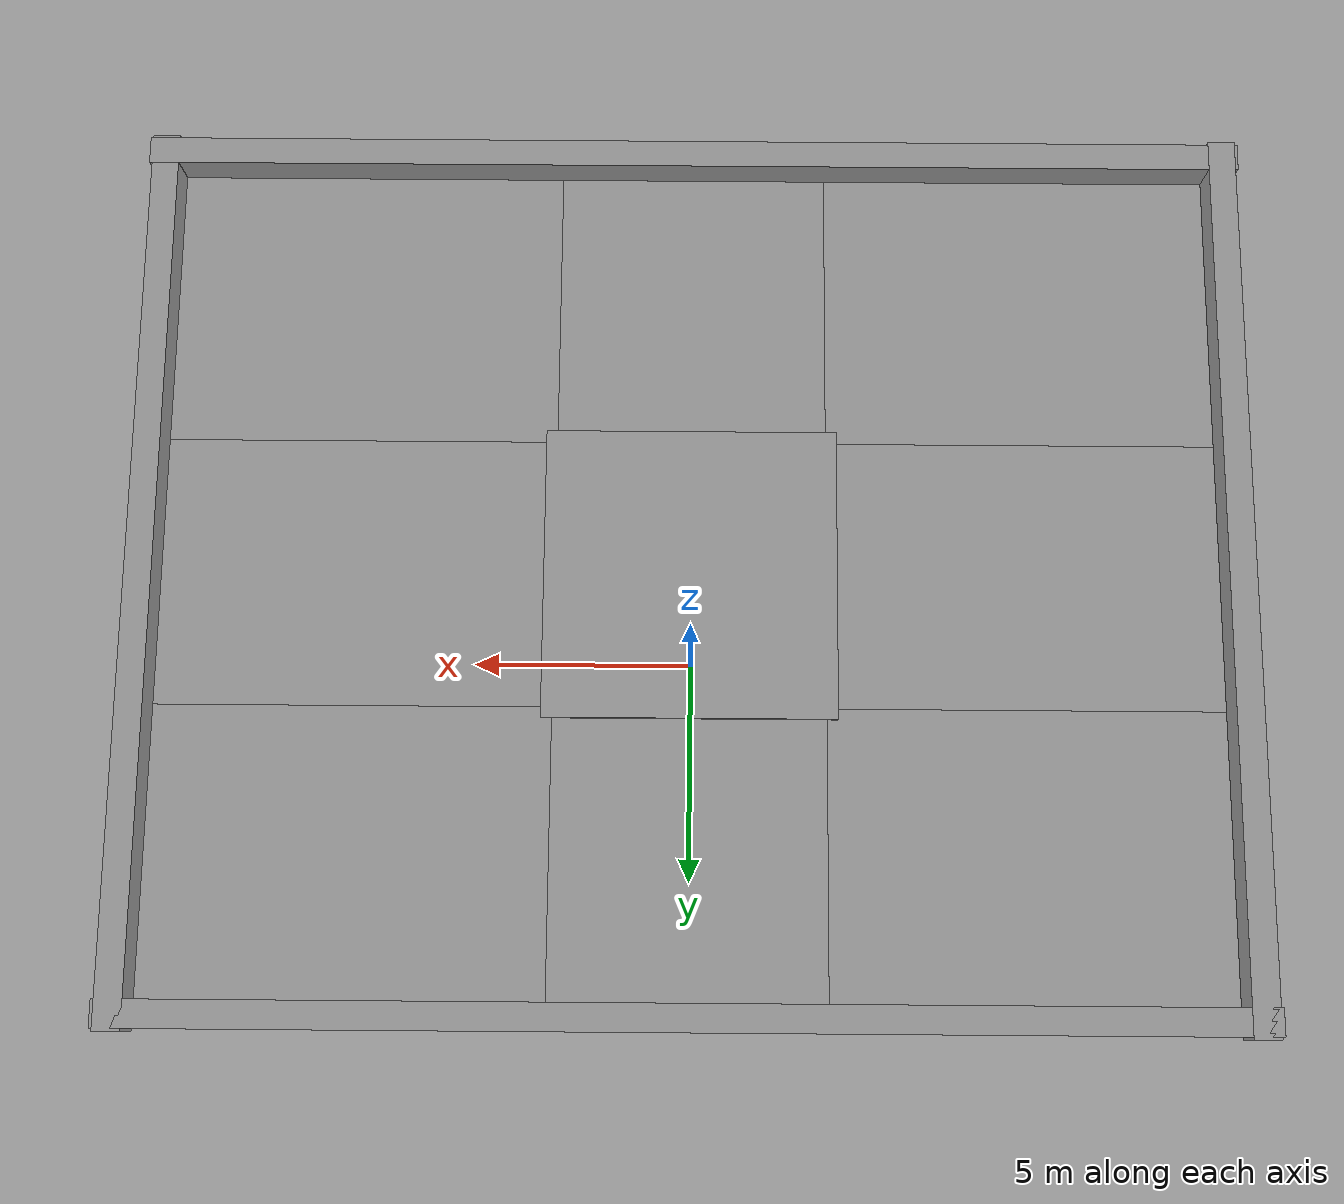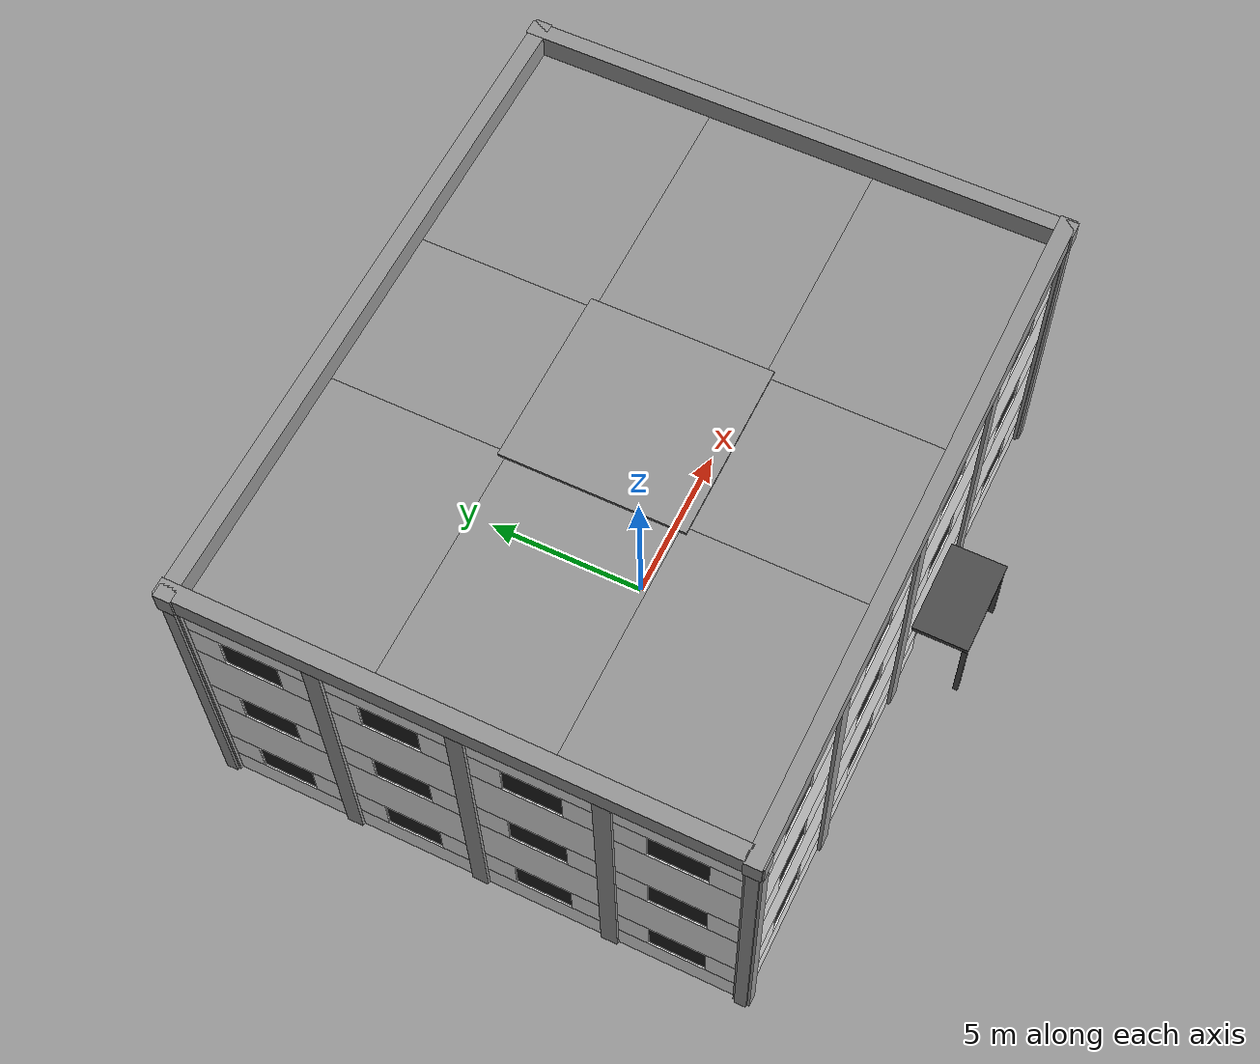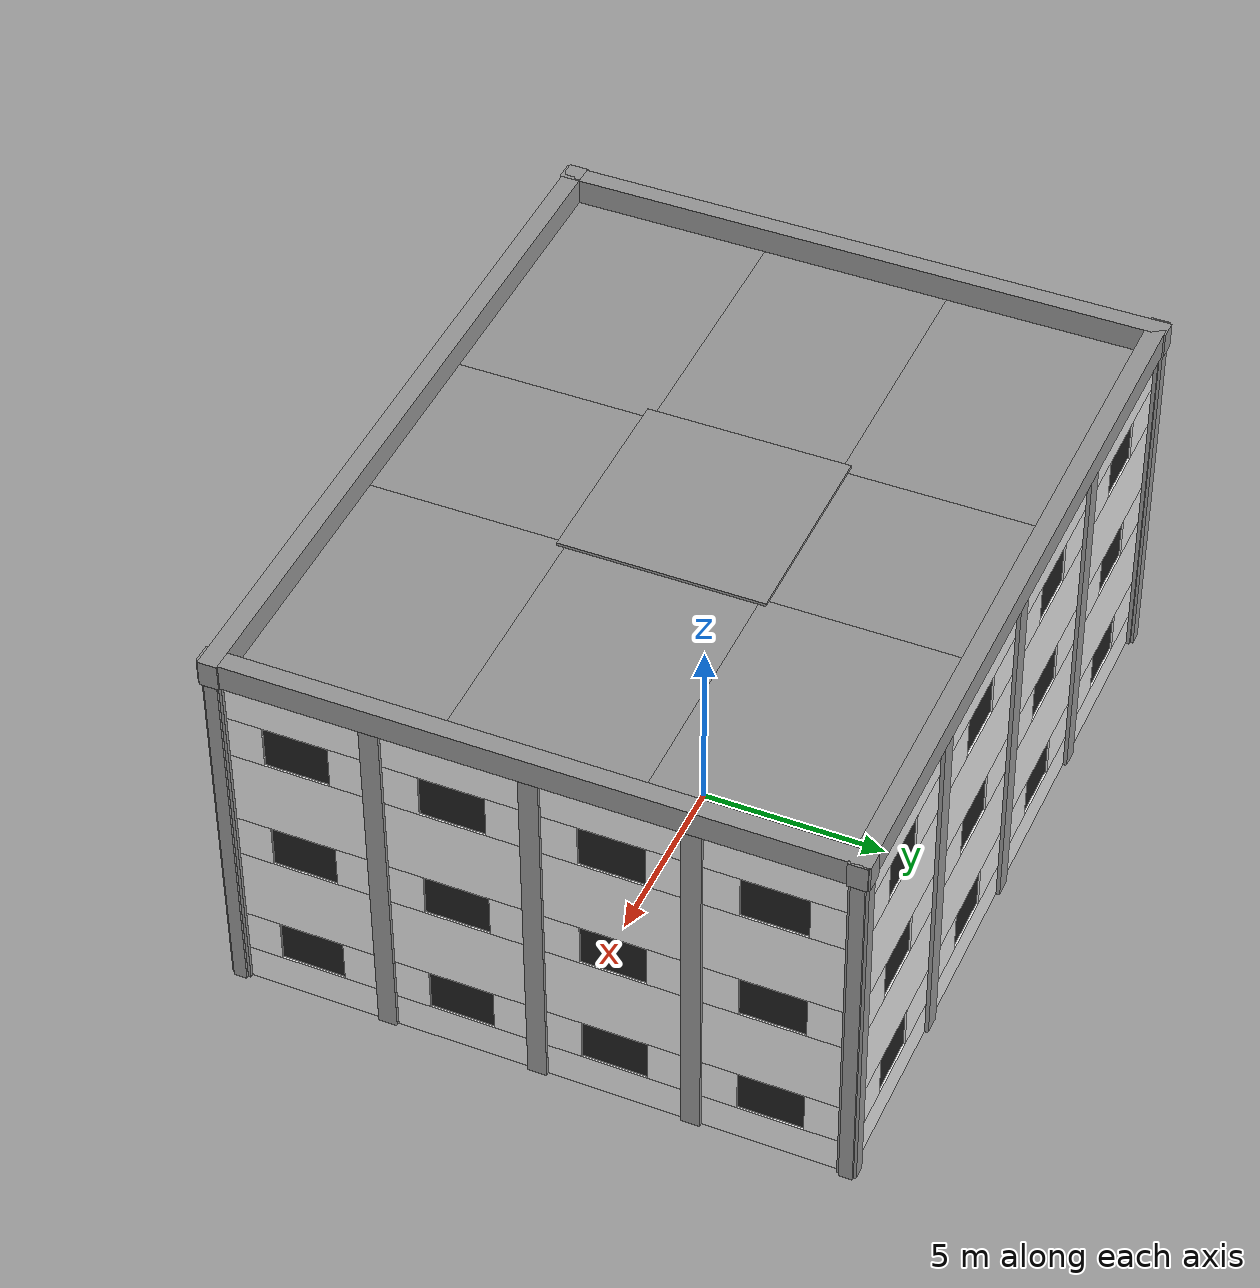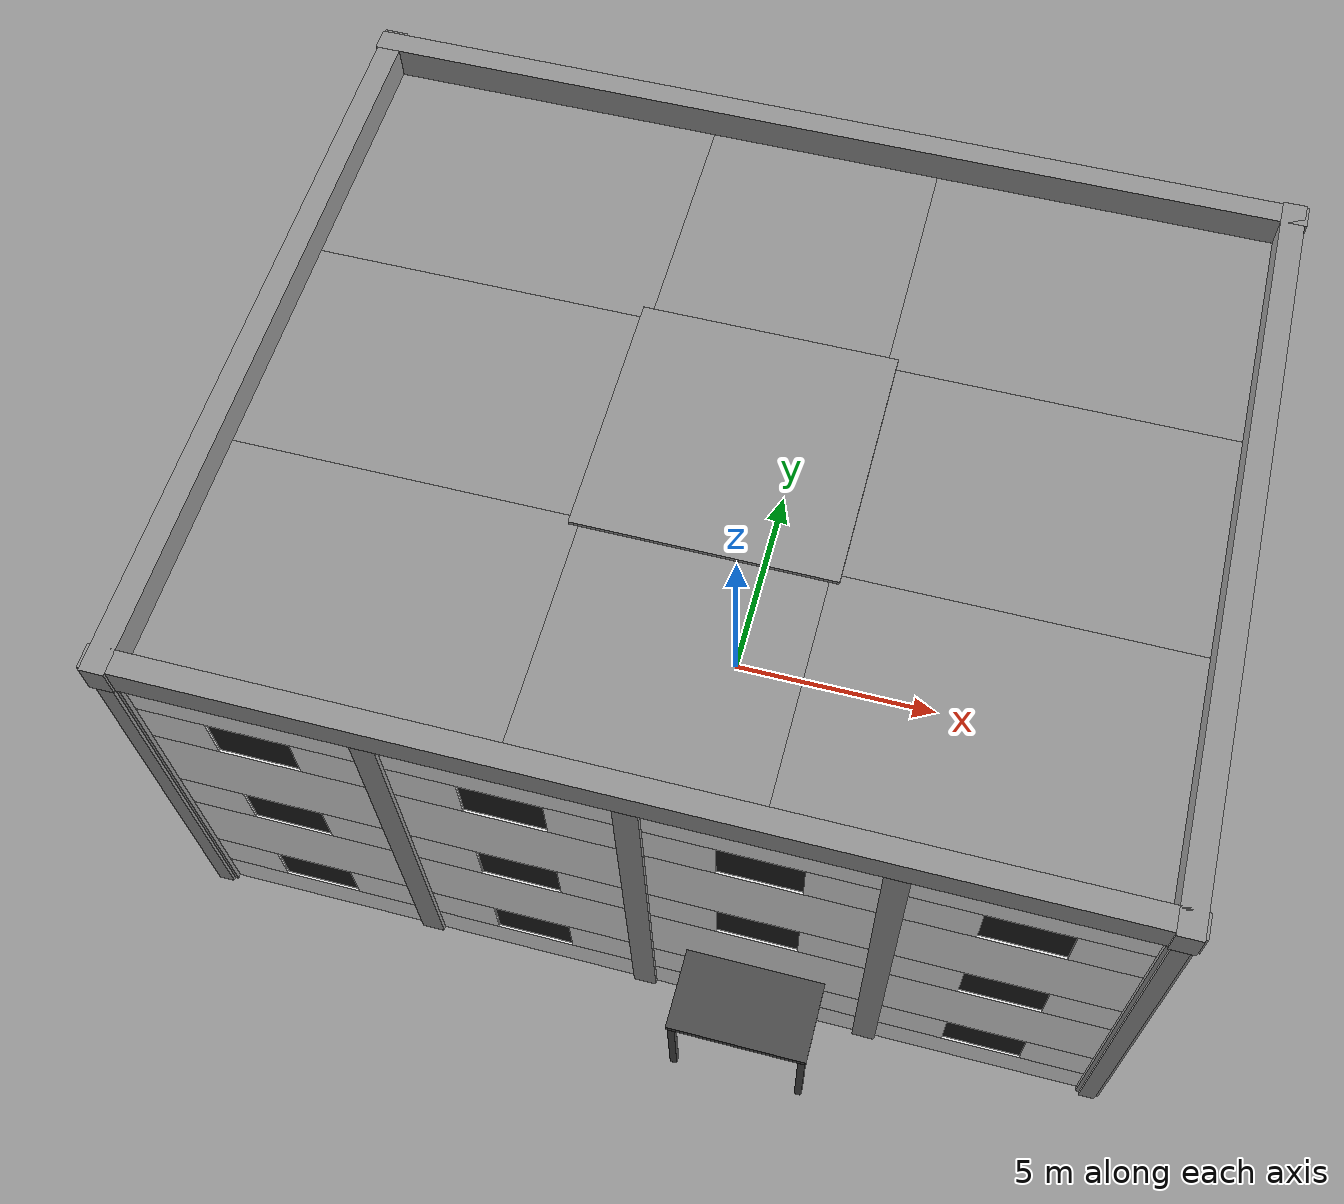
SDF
<sdf version="1.7">
 <world name="default">
  <plugin name="mrs_gazebo_static_transform_republisher_plugin" filename="libMrsGazeboCommonResources_StaticTransformRepublisher.so"/>
  <spherical_coordinates>
   <surface_model>EARTH_WGS84</surface_model>
   <latitude_deg>47.3977</latitude_deg>
   <longitude_deg>8.54559</longitude_deg>
   <elevation>0</elevation>
   <heading_deg>0</heading_deg>
  </spherical_coordinates>
  <physics name="default_physics" default="0" type="ode">
   <ode>
    <solver>
     <type>quick</type>
     <iters>10</iters>
     <sor>1.3</sor>
     <use_dynamic_moi_rescaling>0</use_dynamic_moi_rescaling>
    </solver>
    <constraints>
     <cfm>0</cfm>
     <erp>0.2</erp>
     <contact_max_correcting_vel>1000</contact_max_correcting_vel>
     <contact_surface_layer>0.001</contact_surface_layer>
    </constraints>
   </ode>
   <max_step_size>0.004</max_step_size>
   <real_time_factor>1</real_time_factor>
   <real_time_update_rate>250</real_time_update_rate>
  </physics>
  <scene><shadows>0</shadows><ambient>0.4 0.4 0.4 1</ambient><background>0.7 0.7 0.7 1</background></scene>
  <light name="sun" type="directional">
   <pose>0 0 1000 0.4 0.2 0</pose>
   <diffuse>1 1 1 1</diffuse>
   <specular>0.6 0.6 0.6 1</specular>
   <direction>0.1 0.1 -0.9</direction>
   <attenuation>
    <range>20</range>
    <constant>0.5</constant>
    <linear>0.01</linear>
    <quadratic>0.001</quadratic>
   </attenuation>
   <spot><inner_angle>0</inner_angle><outer_angle>0</outer_angle><falloff>0</falloff></spot>
  </light>
  <model name="the_void">
   <static>1</static>
   <link name="link">
    <pose>0 0 0.1 0 -0 0</pose>
    <visual name="the_void">
     <pose>0 0 2 0 -0 0</pose>
     <geometry><sphere><radius>0.25</radius></sphere></geometry>
     <material>
      <script><uri>file://media/materials/scripts/Gazebo.material</uri><name>Gazebo/Black</name></script>
     </material>
    </visual>
   </link>
   <pose>-1000 -1000 0 0 -0 0</pose>
  </model>
  <plugin name="mrs_gazebo_rviz_cam_synchronizer" filename="libMrsGazeboCommonResources_RvizCameraSynchronizer.so">
   <target_frame_id>gazebo_user_camera</target_frame_id>
   <world_origin_frame_id>uav1/gps_origin</world_origin_frame_id>
   <frame_to_follow>uav1</frame_to_follow>
  </plugin>
  <gravity>0 0 -9.8066</gravity>
  <magnetic_field>6e-06 2.3e-05 -4.2e-05</magnetic_field>
  <atmosphere type="adiabatic"/>
  <model name="building_shell">
   <static>1</static>
   <link name="wNsb0_0">
    <pose>0 8 0.5 0 0 0</pose>
    <collision name="c"><geometry><box><size>20 0.15 1</size></box></geometry></collision>
    <visual name="v">
     <geometry><box><size>20 0.15 1</size></box></geometry>
     <material>
      <script><uri>file://media/materials/scripts/Gazebo.material</uri><name>Gazebo/White</name></script>
     </material>
    </visual>
   </link>
   <link name="wNsb1_0">
    <pose>0 8 3.25 0 0 0</pose>
    <collision name="c"><geometry><box><size>20 0.15 2.1</size></box></geometry></collision>
    <visual name="v">
     <geometry><box><size>20 0.15 2.1</size></box></geometry>
     <material>
      <script><uri>file://media/materials/scripts/Gazebo.material</uri><name>Gazebo/White</name></script>
     </material>
    </visual>
   </link>
   <link name="wNsb2_0">
    <pose>0 8 6.55 0 0 0</pose>
    <collision name="c"><geometry><box><size>20 0.15 2.1</size></box></geometry></collision>
    <visual name="v">
     <geometry><box><size>20 0.15 2.1</size></box></geometry>
     <material>
      <script><uri>file://media/materials/scripts/Gazebo.material</uri><name>Gazebo/White</name></script>
     </material>
    </visual>
   </link>
   <link name="wNsb3_0">
    <pose>0 8 9.35 0 0 0</pose>
    <collision name="c"><geometry><box><size>20 0.15 1.1</size></box></geometry></collision>
    <visual name="v">
     <geometry><box><size>20 0.15 1.1</size></box></geometry>
     <material>
      <script><uri>file://media/materials/scripts/Gazebo.material</uri><name>Gazebo/White</name></script>
     </material>
    </visual>
   </link>
   <link name="wNm0_0">
    <pose>-9.175 8 1.6 0 0 0</pose>
    <collision name="c"><geometry><box><size>1.65 0.15 1.2</size></box></geometry></collision>
    <visual name="v">
     <geometry><box><size>1.65 0.15 1.2</size></box></geometry>
     <material>
      <script><uri>file://media/materials/scripts/Gazebo.material</uri><name>Gazebo/White</name></script>
     </material>
    </visual>
   </link>
   <link name="wNm0_1">
    <pose>-5 8 1.6 0 0 0</pose>
    <collision name="c"><geometry><box><size>3.3 0.15 1.2</size></box></geometry></collision>
    <visual name="v">
     <geometry><box><size>3.3 0.15 1.2</size></box></geometry>
     <material>
      <script><uri>file://media/materials/scripts/Gazebo.material</uri><name>Gazebo/White</name></script>
     </material>
    </visual>
   </link>
   <link name="wNm0_2">
    <pose>0 8 1.6 0 0 0</pose>
    <collision name="c"><geometry><box><size>3.3 0.15 1.2</size></box></geometry></collision>
    <visual name="v">
     <geometry><box><size>3.3 0.15 1.2</size></box></geometry>
     <material>
      <script><uri>file://media/materials/scripts/Gazebo.material</uri><name>Gazebo/White</name></script>
     </material>
    </visual>
   </link>
   <link name="wNm0_3">
    <pose>5 8 1.6 0 0 0</pose>
    <collision name="c"><geometry><box><size>3.3 0.15 1.2</size></box></geometry></collision>
    <visual name="v">
     <geometry><box><size>3.3 0.15 1.2</size></box></geometry>
     <material>
      <script><uri>file://media/materials/scripts/Gazebo.material</uri><name>Gazebo/White</name></script>
     </material>
    </visual>
   </link>
   <link name="wNm0_4">
    <pose>9.175 8 1.6 0 0 0</pose>
    <collision name="c"><geometry><box><size>1.65 0.15 1.2</size></box></geometry></collision>
    <visual name="v">
     <geometry><box><size>1.65 0.15 1.2</size></box></geometry>
     <material>
      <script><uri>file://media/materials/scripts/Gazebo.material</uri><name>Gazebo/White</name></script>
     </material>
    </visual>
   </link>
   <link name="wNg0_0">
    <pose>-7.5 8 1.6 0 0 0</pose>
    <collision name="c"><geometry><box><size>1.7 0.05 1.2</size></box></geometry></collision>
    <visual name="v">
     <geometry><box><size>1.7 0.05 1.2</size></box></geometry>
     <material>
      <script><uri>file://media/materials/scripts/Gazebo.material</uri><name>Gazebo/FlatBlack</name></script>
     </material>
    </visual>
   </link>
   <link name="wNg0_1">
    <pose>-2.5 8 1.6 0 0 0</pose>
    <collision name="c"><geometry><box><size>1.7 0.05 1.2</size></box></geometry></collision>
    <visual name="v">
     <geometry><box><size>1.7 0.05 1.2</size></box></geometry>
     <material>
      <script><uri>file://media/materials/scripts/Gazebo.material</uri><name>Gazebo/FlatBlack</name></script>
     </material>
    </visual>
   </link>
   <link name="wNg0_2">
    <pose>2.5 8 1.6 0 0 0</pose>
    <collision name="c"><geometry><box><size>1.7 0.05 1.2</size></box></geometry></collision>
    <visual name="v">
     <geometry><box><size>1.7 0.05 1.2</size></box></geometry>
     <material>
      <script><uri>file://media/materials/scripts/Gazebo.material</uri><name>Gazebo/FlatBlack</name></script>
     </material>
    </visual>
   </link>
   <link name="wNg0_3">
    <pose>7.5 8 1.6 0 0 0</pose>
    <collision name="c"><geometry><box><size>1.7 0.05 1.2</size></box></geometry></collision>
    <visual name="v">
     <geometry><box><size>1.7 0.05 1.2</size></box></geometry>
     <material>
      <script><uri>file://media/materials/scripts/Gazebo.material</uri><name>Gazebo/FlatBlack</name></script>
     </material>
    </visual>
   </link>
   <link name="wNm1_0">
    <pose>-9.175 8 4.9 0 0 0</pose>
    <collision name="c"><geometry><box><size>1.65 0.15 1.2</size></box></geometry></collision>
    <visual name="v">
     <geometry><box><size>1.65 0.15 1.2</size></box></geometry>
     <material>
      <script><uri>file://media/materials/scripts/Gazebo.material</uri><name>Gazebo/White</name></script>
     </material>
    </visual>
   </link>
   <link name="wNm1_1">
    <pose>-5 8 4.9 0 0 0</pose>
    <collision name="c"><geometry><box><size>3.3 0.15 1.2</size></box></geometry></collision>
    <visual name="v">
     <geometry><box><size>3.3 0.15 1.2</size></box></geometry>
     <material>
      <script><uri>file://media/materials/scripts/Gazebo.material</uri><name>Gazebo/White</name></script>
     </material>
    </visual>
   </link>
   <link name="wNm1_2">
    <pose>0 8 4.9 0 0 0</pose>
    <collision name="c"><geometry><box><size>3.3 0.15 1.2</size></box></geometry></collision>
    <visual name="v">
     <geometry><box><size>3.3 0.15 1.2</size></box></geometry>
     <material>
      <script><uri>file://media/materials/scripts/Gazebo.material</uri><name>Gazebo/White</name></script>
     </material>
    </visual>
   </link>
   <link name="wNm1_3">
    <pose>5 8 4.9 0 0 0</pose>
    <collision name="c"><geometry><box><size>3.3 0.15 1.2</size></box></geometry></collision>
    <visual name="v">
     <geometry><box><size>3.3 0.15 1.2</size></box></geometry>
     <material>
      <script><uri>file://media/materials/scripts/Gazebo.material</uri><name>Gazebo/White</name></script>
     </material>
    </visual>
   </link>
   <link name="wNm1_4">
    <pose>9.175 8 4.9 0 0 0</pose>
    <collision name="c"><geometry><box><size>1.65 0.15 1.2</size></box></geometry></collision>
    <visual name="v">
     <geometry><box><size>1.65 0.15 1.2</size></box></geometry>
     <material>
      <script><uri>file://media/materials/scripts/Gazebo.material</uri><name>Gazebo/White</name></script>
     </material>
    </visual>
   </link>
   <link name="wNg1_0">
    <pose>-7.5 8 4.9 0 0 0</pose>
    <collision name="c"><geometry><box><size>1.7 0.05 1.2</size></box></geometry></collision>
    <visual name="v">
     <geometry><box><size>1.7 0.05 1.2</size></box></geometry>
     <material>
      <script><uri>file://media/materials/scripts/Gazebo.material</uri><name>Gazebo/FlatBlack</name></script>
     </material>
    </visual>
   </link>
   <link name="wNg1_1">
    <pose>-2.5 8 4.9 0 0 0</pose>
    <collision name="c"><geometry><box><size>1.7 0.05 1.2</size></box></geometry></collision>
    <visual name="v">
     <geometry><box><size>1.7 0.05 1.2</size></box></geometry>
     <material>
      <script><uri>file://media/materials/scripts/Gazebo.material</uri><name>Gazebo/FlatBlack</name></script>
     </material>
    </visual>
   </link>
   <link name="wNg1_2">
    <pose>2.5 8 4.9 0 0 0</pose>
    <collision name="c"><geometry><box><size>1.7 0.05 1.2</size></box></geometry></collision>
    <visual name="v">
     <geometry><box><size>1.7 0.05 1.2</size></box></geometry>
     <material>
      <script><uri>file://media/materials/scripts/Gazebo.material</uri><name>Gazebo/FlatBlack</name></script>
     </material>
    </visual>
   </link>
   <link name="wNg1_3">
    <pose>7.5 8 4.9 0 0 0</pose>
    <collision name="c"><geometry><box><size>1.7 0.05 1.2</size></box></geometry></collision>
    <visual name="v">
     <geometry><box><size>1.7 0.05 1.2</size></box></geometry>
     <material>
      <script><uri>file://media/materials/scripts/Gazebo.material</uri><name>Gazebo/FlatBlack</name></script>
     </material>
    </visual>
   </link>
   <link name="wNm2_0">
    <pose>-9.175 8 8.2 0 0 0</pose>
    <collision name="c"><geometry><box><size>1.65 0.15 1.2</size></box></geometry></collision>
    <visual name="v">
     <geometry><box><size>1.65 0.15 1.2</size></box></geometry>
     <material>
      <script><uri>file://media/materials/scripts/Gazebo.material</uri><name>Gazebo/White</name></script>
     </material>
    </visual>
   </link>
   <link name="wNm2_1">
    <pose>-5 8 8.2 0 0 0</pose>
    <collision name="c"><geometry><box><size>3.3 0.15 1.2</size></box></geometry></collision>
    <visual name="v">
     <geometry><box><size>3.3 0.15 1.2</size></box></geometry>
     <material>
      <script><uri>file://media/materials/scripts/Gazebo.material</uri><name>Gazebo/White</name></script>
     </material>
    </visual>
   </link>
   <link name="wNm2_2">
    <pose>0 8 8.2 0 0 0</pose>
    <collision name="c"><geometry><box><size>3.3 0.15 1.2</size></box></geometry></collision>
    <visual name="v">
     <geometry><box><size>3.3 0.15 1.2</size></box></geometry>
     <material>
      <script><uri>file://media/materials/scripts/Gazebo.material</uri><name>Gazebo/White</name></script>
     </material>
    </visual>
   </link>
   <link name="wNm2_3">
    <pose>5 8 8.2 0 0 0</pose>
    <collision name="c"><geometry><box><size>3.3 0.15 1.2</size></box></geometry></collision>
    <visual name="v">
     <geometry><box><size>3.3 0.15 1.2</size></box></geometry>
     <material>
      <script><uri>file://media/materials/scripts/Gazebo.material</uri><name>Gazebo/White</name></script>
     </material>
    </visual>
   </link>
   <link name="wNm2_4">
    <pose>9.175 8 8.2 0 0 0</pose>
    <collision name="c"><geometry><box><size>1.65 0.15 1.2</size></box></geometry></collision>
    <visual name="v">
     <geometry><box><size>1.65 0.15 1.2</size></box></geometry>
     <material>
      <script><uri>file://media/materials/scripts/Gazebo.material</uri><name>Gazebo/White</name></script>
     </material>
    </visual>
   </link>
   <link name="wNg2_0">
    <pose>-7.5 8 8.2 0 0 0</pose>
    <collision name="c"><geometry><box><size>1.7 0.05 1.2</size></box></geometry></collision>
    <visual name="v">
     <geometry><box><size>1.7 0.05 1.2</size></box></geometry>
     <material>
      <script><uri>file://media/materials/scripts/Gazebo.material</uri><name>Gazebo/FlatBlack</name></script>
     </material>
    </visual>
   </link>
   <link name="wNg2_1">
    <pose>-2.5 8 8.2 0 0 0</pose>
    <collision name="c"><geometry><box><size>1.7 0.05 1.2</size></box></geometry></collision>
    <visual name="v">
     <geometry><box><size>1.7 0.05 1.2</size></box></geometry>
     <material>
      <script><uri>file://media/materials/scripts/Gazebo.material</uri><name>Gazebo/FlatBlack</name></script>
     </material>
    </visual>
   </link>
   <link name="wNg2_2">
    <pose>2.5 8 8.2 0 0 0</pose>
    <collision name="c"><geometry><box><size>1.7 0.05 1.2</size></box></geometry></collision>
    <visual name="v">
     <geometry><box><size>1.7 0.05 1.2</size></box></geometry>
     <material>
      <script><uri>file://media/materials/scripts/Gazebo.material</uri><name>Gazebo/FlatBlack</name></script>
     </material>
    </visual>
   </link>
   <link name="wNg2_3">
    <pose>7.5 8 8.2 0 0 0</pose>
    <collision name="c"><geometry><box><size>1.7 0.05 1.2</size></box></geometry></collision>
    <visual name="v">
     <geometry><box><size>1.7 0.05 1.2</size></box></geometry>
     <material>
      <script><uri>file://media/materials/scripts/Gazebo.material</uri><name>Gazebo/FlatBlack</name></script>
     </material>
    </visual>
   </link>
   <link name="wNpil-10">
    <pose>-10 8 4.95 0 0 0</pose>
    <collision name="c"><geometry><box><size>0.5 0.35 9.9</size></box></geometry></collision>
    <visual name="v">
     <geometry><box><size>0.5 0.35 9.9</size></box></geometry>
     <material>
      <script><uri>file://media/materials/scripts/Gazebo.material</uri><name>Gazebo/Grey</name></script>
     </material>
    </visual>
   </link>
   <link name="wNpil-5">
    <pose>-5 8 4.95 0 0 0</pose>
    <collision name="c"><geometry><box><size>0.5 0.35 9.9</size></box></geometry></collision>
    <visual name="v">
     <geometry><box><size>0.5 0.35 9.9</size></box></geometry>
     <material>
      <script><uri>file://media/materials/scripts/Gazebo.material</uri><name>Gazebo/Grey</name></script>
     </material>
    </visual>
   </link>
   <link name="wNpil0">
    <pose>0 8 4.95 0 0 0</pose>
    <collision name="c"><geometry><box><size>0.5 0.35 9.9</size></box></geometry></collision>
    <visual name="v">
     <geometry><box><size>0.5 0.35 9.9</size></box></geometry>
     <material>
      <script><uri>file://media/materials/scripts/Gazebo.material</uri><name>Gazebo/Grey</name></script>
     </material>
    </visual>
   </link>
   <link name="wNpil5">
    <pose>5 8 4.95 0 0 0</pose>
    <collision name="c"><geometry><box><size>0.5 0.35 9.9</size></box></geometry></collision>
    <visual name="v">
     <geometry><box><size>0.5 0.35 9.9</size></box></geometry>
     <material>
      <script><uri>file://media/materials/scripts/Gazebo.material</uri><name>Gazebo/Grey</name></script>
     </material>
    </visual>
   </link>
   <link name="wNpil10">
    <pose>10 8 4.95 0 0 0</pose>
    <collision name="c"><geometry><box><size>0.5 0.35 9.9</size></box></geometry></collision>
    <visual name="v">
     <geometry><box><size>0.5 0.35 9.9</size></box></geometry>
     <material>
      <script><uri>file://media/materials/scripts/Gazebo.material</uri><name>Gazebo/Grey</name></script>
     </material>
    </visual>
   </link>
   <link name="wSsb0_0">
    <pose>-4.15 -8 0.5 0 0 0</pose>
    <collision name="c"><geometry><box><size>11.7 0.15 1</size></box></geometry></collision>
    <visual name="v">
     <geometry><box><size>11.7 0.15 1</size></box></geometry>
     <material>
      <script><uri>file://media/materials/scripts/Gazebo.material</uri><name>Gazebo/White</name></script>
     </material>
    </visual>
   </link>
   <link name="wSsb0_1">
    <pose>6.65 -8 0.5 0 0 0</pose>
    <collision name="c"><geometry><box><size>6.7 0.15 1</size></box></geometry></collision>
    <visual name="v">
     <geometry><box><size>6.7 0.15 1</size></box></geometry>
     <material>
      <script><uri>file://media/materials/scripts/Gazebo.material</uri><name>Gazebo/White</name></script>
     </material>
    </visual>
   </link>
   <link name="wSsb1_0">
    <pose>0 -8 3.25 0 0 0</pose>
    <collision name="c"><geometry><box><size>20 0.15 2.1</size></box></geometry></collision>
    <visual name="v">
     <geometry><box><size>20 0.15 2.1</size></box></geometry>
     <material>
      <script><uri>file://media/materials/scripts/Gazebo.material</uri><name>Gazebo/White</name></script>
     </material>
    </visual>
   </link>
   <link name="wSsb2_0">
    <pose>0 -8 6.55 0 0 0</pose>
    <collision name="c"><geometry><box><size>20 0.15 2.1</size></box></geometry></collision>
    <visual name="v">
     <geometry><box><size>20 0.15 2.1</size></box></geometry>
     <material>
      <script><uri>file://media/materials/scripts/Gazebo.material</uri><name>Gazebo/White</name></script>
     </material>
    </visual>
   </link>
   <link name="wSsb3_0">
    <pose>0 -8 9.35 0 0 0</pose>
    <collision name="c"><geometry><box><size>20 0.15 1.1</size></box></geometry></collision>
    <visual name="v">
     <geometry><box><size>20 0.15 1.1</size></box></geometry>
     <material>
      <script><uri>file://media/materials/scripts/Gazebo.material</uri><name>Gazebo/White</name></script>
     </material>
    </visual>
   </link>
   <link name="wSm0_0">
    <pose>-9.175 -8 1.6 0 0 0</pose>
    <collision name="c"><geometry><box><size>1.65 0.15 1.2</size></box></geometry></collision>
    <visual name="v">
     <geometry><box><size>1.65 0.15 1.2</size></box></geometry>
     <material>
      <script><uri>file://media/materials/scripts/Gazebo.material</uri><name>Gazebo/White</name></script>
     </material>
    </visual>
   </link>
   <link name="wSm0_1">
    <pose>-5 -8 1.6 0 0 0</pose>
    <collision name="c"><geometry><box><size>3.3 0.15 1.2</size></box></geometry></collision>
    <visual name="v">
     <geometry><box><size>3.3 0.15 1.2</size></box></geometry>
     <material>
      <script><uri>file://media/materials/scripts/Gazebo.material</uri><name>Gazebo/White</name></script>
     </material>
    </visual>
   </link>
   <link name="wSm0_2">
    <pose>0 -8 1.6 0 0 0</pose>
    <collision name="c"><geometry><box><size>3.3 0.15 1.2</size></box></geometry></collision>
    <visual name="v">
     <geometry><box><size>3.3 0.15 1.2</size></box></geometry>
     <material>
      <script><uri>file://media/materials/scripts/Gazebo.material</uri><name>Gazebo/White</name></script>
     </material>
    </visual>
   </link>
   <link name="wSm0_3">
    <pose>5 -8 1.6 0 0 0</pose>
    <collision name="c"><geometry><box><size>3.3 0.15 1.2</size></box></geometry></collision>
    <visual name="v">
     <geometry><box><size>3.3 0.15 1.2</size></box></geometry>
     <material>
      <script><uri>file://media/materials/scripts/Gazebo.material</uri><name>Gazebo/White</name></script>
     </material>
    </visual>
   </link>
   <link name="wSm0_4">
    <pose>9.175 -8 1.6 0 0 0</pose>
    <collision name="c"><geometry><box><size>1.65 0.15 1.2</size></box></geometry></collision>
    <visual name="v">
     <geometry><box><size>1.65 0.15 1.2</size></box></geometry>
     <material>
      <script><uri>file://media/materials/scripts/Gazebo.material</uri><name>Gazebo/White</name></script>
     </material>
    </visual>
   </link>
   <link name="wSg0_0">
    <pose>-7.5 -8 1.6 0 0 0</pose>
    <collision name="c"><geometry><box><size>1.7 0.05 1.2</size></box></geometry></collision>
    <visual name="v">
     <geometry><box><size>1.7 0.05 1.2</size></box></geometry>
     <material>
      <script><uri>file://media/materials/scripts/Gazebo.material</uri><name>Gazebo/FlatBlack</name></script>
     </material>
    </visual>
   </link>
   <link name="wSg0_1">
    <pose>-2.5 -8 1.6 0 0 0</pose>
    <collision name="c"><geometry><box><size>1.7 0.05 1.2</size></box></geometry></collision>
    <visual name="v">
     <geometry><box><size>1.7 0.05 1.2</size></box></geometry>
     <material>
      <script><uri>file://media/materials/scripts/Gazebo.material</uri><name>Gazebo/FlatBlack</name></script>
     </material>
    </visual>
   </link>
   <link name="wSg0_3">
    <pose>7.5 -8 1.6 0 0 0</pose>
    <collision name="c"><geometry><box><size>1.7 0.05 1.2</size></box></geometry></collision>
    <visual name="v">
     <geometry><box><size>1.7 0.05 1.2</size></box></geometry>
     <material>
      <script><uri>file://media/materials/scripts/Gazebo.material</uri><name>Gazebo/FlatBlack</name></script>
     </material>
    </visual>
   </link>
   <link name="wSm1_0">
    <pose>-9.175 -8 4.9 0 0 0</pose>
    <collision name="c"><geometry><box><size>1.65 0.15 1.2</size></box></geometry></collision>
    <visual name="v">
     <geometry><box><size>1.65 0.15 1.2</size></box></geometry>
     <material>
      <script><uri>file://media/materials/scripts/Gazebo.material</uri><name>Gazebo/White</name></script>
     </material>
    </visual>
   </link>
   <link name="wSm1_1">
    <pose>-5 -8 4.9 0 0 0</pose>
    <collision name="c"><geometry><box><size>3.3 0.15 1.2</size></box></geometry></collision>
    <visual name="v">
     <geometry><box><size>3.3 0.15 1.2</size></box></geometry>
     <material>
      <script><uri>file://media/materials/scripts/Gazebo.material</uri><name>Gazebo/White</name></script>
     </material>
    </visual>
   </link>
   <link name="wSm1_2">
    <pose>0 -8 4.9 0 0 0</pose>
    <collision name="c"><geometry><box><size>3.3 0.15 1.2</size></box></geometry></collision>
    <visual name="v">
     <geometry><box><size>3.3 0.15 1.2</size></box></geometry>
     <material>
      <script><uri>file://media/materials/scripts/Gazebo.material</uri><name>Gazebo/White</name></script>
     </material>
    </visual>
   </link>
   <link name="wSm1_3">
    <pose>5 -8 4.9 0 0 0</pose>
    <collision name="c"><geometry><box><size>3.3 0.15 1.2</size></box></geometry></collision>
    <visual name="v">
     <geometry><box><size>3.3 0.15 1.2</size></box></geometry>
     <material>
      <script><uri>file://media/materials/scripts/Gazebo.material</uri><name>Gazebo/White</name></script>
     </material>
    </visual>
   </link>
   <link name="wSm1_4">
    <pose>9.175 -8 4.9 0 0 0</pose>
    <collision name="c"><geometry><box><size>1.65 0.15 1.2</size></box></geometry></collision>
    <visual name="v">
     <geometry><box><size>1.65 0.15 1.2</size></box></geometry>
     <material>
      <script><uri>file://media/materials/scripts/Gazebo.material</uri><name>Gazebo/White</name></script>
     </material>
    </visual>
   </link>
   <link name="wSg1_0">
    <pose>-7.5 -8 4.9 0 0 0</pose>
    <collision name="c"><geometry><box><size>1.7 0.05 1.2</size></box></geometry></collision>
    <visual name="v">
     <geometry><box><size>1.7 0.05 1.2</size></box></geometry>
     <material>
      <script><uri>file://media/materials/scripts/Gazebo.material</uri><name>Gazebo/FlatBlack</name></script>
     </material>
    </visual>
   </link>
   <link name="wSg1_1">
    <pose>-2.5 -8 4.9 0 0 0</pose>
    <collision name="c"><geometry><box><size>1.7 0.05 1.2</size></box></geometry></collision>
    <visual name="v">
     <geometry><box><size>1.7 0.05 1.2</size></box></geometry>
     <material>
      <script><uri>file://media/materials/scripts/Gazebo.material</uri><name>Gazebo/FlatBlack</name></script>
     </material>
    </visual>
   </link>
   <link name="wSg1_2">
    <pose>2.5 -8 4.9 0 0 0</pose>
    <collision name="c"><geometry><box><size>1.7 0.05 1.2</size></box></geometry></collision>
    <visual name="v">
     <geometry><box><size>1.7 0.05 1.2</size></box></geometry>
     <material>
      <script><uri>file://media/materials/scripts/Gazebo.material</uri><name>Gazebo/FlatBlack</name></script>
     </material>
    </visual>
   </link>
   <link name="wSg1_3">
    <pose>7.5 -8 4.9 0 0 0</pose>
    <collision name="c"><geometry><box><size>1.7 0.05 1.2</size></box></geometry></collision>
    <visual name="v">
     <geometry><box><size>1.7 0.05 1.2</size></box></geometry>
     <material>
      <script><uri>file://media/materials/scripts/Gazebo.material</uri><name>Gazebo/FlatBlack</name></script>
     </material>
    </visual>
   </link>
   <link name="wSm2_0">
    <pose>-9.175 -8 8.2 0 0 0</pose>
    <collision name="c"><geometry><box><size>1.65 0.15 1.2</size></box></geometry></collision>
    <visual name="v">
     <geometry><box><size>1.65 0.15 1.2</size></box></geometry>
     <material>
      <script><uri>file://media/materials/scripts/Gazebo.material</uri><name>Gazebo/White</name></script>
     </material>
    </visual>
   </link>
   <link name="wSm2_1">
    <pose>-5 -8 8.2 0 0 0</pose>
    <collision name="c"><geometry><box><size>3.3 0.15 1.2</size></box></geometry></collision>
    <visual name="v">
     <geometry><box><size>3.3 0.15 1.2</size></box></geometry>
     <material>
      <script><uri>file://media/materials/scripts/Gazebo.material</uri><name>Gazebo/White</name></script>
     </material>
    </visual>
   </link>
   <link name="wSm2_2">
    <pose>0 -8 8.2 0 0 0</pose>
    <collision name="c"><geometry><box><size>3.3 0.15 1.2</size></box></geometry></collision>
    <visual name="v">
     <geometry><box><size>3.3 0.15 1.2</size></box></geometry>
     <material>
      <script><uri>file://media/materials/scripts/Gazebo.material</uri><name>Gazebo/White</name></script>
     </material>
    </visual>
   </link>
   <link name="wSm2_3">
    <pose>5 -8 8.2 0 0 0</pose>
    <collision name="c"><geometry><box><size>3.3 0.15 1.2</size></box></geometry></collision>
    <visual name="v">
     <geometry><box><size>3.3 0.15 1.2</size></box></geometry>
     <material>
      <script><uri>file://media/materials/scripts/Gazebo.material</uri><name>Gazebo/White</name></script>
     </material>
    </visual>
   </link>
   <link name="wSm2_4">
    <pose>9.175 -8 8.2 0 0 0</pose>
    <collision name="c"><geometry><box><size>1.65 0.15 1.2</size></box></geometry></collision>
    <visual name="v">
     <geometry><box><size>1.65 0.15 1.2</size></box></geometry>
     <material>
      <script><uri>file://media/materials/scripts/Gazebo.material</uri><name>Gazebo/White</name></script>
     </material>
    </visual>
   </link>
   <link name="wSg2_0">
    <pose>-7.5 -8 8.2 0 0 0</pose>
    <collision name="c"><geometry><box><size>1.7 0.05 1.2</size></box></geometry></collision>
    <visual name="v">
     <geometry><box><size>1.7 0.05 1.2</size></box></geometry>
     <material>
      <script><uri>file://media/materials/scripts/Gazebo.material</uri><name>Gazebo/FlatBlack</name></script>
     </material>
    </visual>
   </link>
   <link name="wSg2_1">
    <pose>-2.5 -8 8.2 0 0 0</pose>
    <collision name="c"><geometry><box><size>1.7 0.05 1.2</size></box></geometry></collision>
    <visual name="v">
     <geometry><box><size>1.7 0.05 1.2</size></box></geometry>
     <material>
      <script><uri>file://media/materials/scripts/Gazebo.material</uri><name>Gazebo/FlatBlack</name></script>
     </material>
    </visual>
   </link>
   <link name="wSg2_2">
    <pose>2.5 -8 8.2 0 0 0</pose>
    <collision name="c"><geometry><box><size>1.7 0.05 1.2</size></box></geometry></collision>
    <visual name="v">
     <geometry><box><size>1.7 0.05 1.2</size></box></geometry>
     <material>
      <script><uri>file://media/materials/scripts/Gazebo.material</uri><name>Gazebo/FlatBlack</name></script>
     </material>
    </visual>
   </link>
   <link name="wSg2_3">
    <pose>7.5 -8 8.2 0 0 0</pose>
    <collision name="c"><geometry><box><size>1.7 0.05 1.2</size></box></geometry></collision>
    <visual name="v">
     <geometry><box><size>1.7 0.05 1.2</size></box></geometry>
     <material>
      <script><uri>file://media/materials/scripts/Gazebo.material</uri><name>Gazebo/FlatBlack</name></script>
     </material>
    </visual>
   </link>
   <link name="wSpil-10">
    <pose>-10 -8 4.95 0 0 0</pose>
    <collision name="c"><geometry><box><size>0.5 0.35 9.9</size></box></geometry></collision>
    <visual name="v">
     <geometry><box><size>0.5 0.35 9.9</size></box></geometry>
     <material>
      <script><uri>file://media/materials/scripts/Gazebo.material</uri><name>Gazebo/Grey</name></script>
     </material>
    </visual>
   </link>
   <link name="wSpil-5">
    <pose>-5 -8 4.95 0 0 0</pose>
    <collision name="c"><geometry><box><size>0.5 0.35 9.9</size></box></geometry></collision>
    <visual name="v">
     <geometry><box><size>0.5 0.35 9.9</size></box></geometry>
     <material>
      <script><uri>file://media/materials/scripts/Gazebo.material</uri><name>Gazebo/Grey</name></script>
     </material>
    </visual>
   </link>
   <link name="wSpil0">
    <pose>0 -8 4.95 0 0 0</pose>
    <collision name="c"><geometry><box><size>0.5 0.35 9.9</size></box></geometry></collision>
    <visual name="v">
     <geometry><box><size>0.5 0.35 9.9</size></box></geometry>
     <material>
      <script><uri>file://media/materials/scripts/Gazebo.material</uri><name>Gazebo/Grey</name></script>
     </material>
    </visual>
   </link>
   <link name="wSpil5">
    <pose>5 -8 4.95 0 0 0</pose>
    <collision name="c"><geometry><box><size>0.5 0.35 9.9</size></box></geometry></collision>
    <visual name="v">
     <geometry><box><size>0.5 0.35 9.9</size></box></geometry>
     <material>
      <script><uri>file://media/materials/scripts/Gazebo.material</uri><name>Gazebo/Grey</name></script>
     </material>
    </visual>
   </link>
   <link name="wSpil10">
    <pose>10 -8 4.95 0 0 0</pose>
    <collision name="c"><geometry><box><size>0.5 0.35 9.9</size></box></geometry></collision>
    <visual name="v">
     <geometry><box><size>0.5 0.35 9.9</size></box></geometry>
     <material>
      <script><uri>file://media/materials/scripts/Gazebo.material</uri><name>Gazebo/Grey</name></script>
     </material>
    </visual>
   </link>
   <link name="wEsb0_0">
    <pose>10 0 0.5 0 0 0</pose>
    <collision name="c"><geometry><box><size>0.15 16 1</size></box></geometry></collision>
    <visual name="v">
     <geometry><box><size>0.15 16 1</size></box></geometry>
     <material>
      <script><uri>file://media/materials/scripts/Gazebo.material</uri><name>Gazebo/White</name></script>
     </material>
    </visual>
   </link>
   <link name="wEsb1_0">
    <pose>10 0 3.25 0 0 0</pose>
    <collision name="c"><geometry><box><size>0.15 16 2.1</size></box></geometry></collision>
    <visual name="v">
     <geometry><box><size>0.15 16 2.1</size></box></geometry>
     <material>
      <script><uri>file://media/materials/scripts/Gazebo.material</uri><name>Gazebo/White</name></script>
     </material>
    </visual>
   </link>
   <link name="wEsb2_0">
    <pose>10 0 6.55 0 0 0</pose>
    <collision name="c"><geometry><box><size>0.15 16 2.1</size></box></geometry></collision>
    <visual name="v">
     <geometry><box><size>0.15 16 2.1</size></box></geometry>
     <material>
      <script><uri>file://media/materials/scripts/Gazebo.material</uri><name>Gazebo/White</name></script>
     </material>
    </visual>
   </link>
   <link name="wEsb3_0">
    <pose>10 0 9.35 0 0 0</pose>
    <collision name="c"><geometry><box><size>0.15 16 1.1</size></box></geometry></collision>
    <visual name="v">
     <geometry><box><size>0.15 16 1.1</size></box></geometry>
     <material>
      <script><uri>file://media/materials/scripts/Gazebo.material</uri><name>Gazebo/White</name></script>
     </material>
    </visual>
   </link>
   <link name="wEm0_0">
    <pose>10 -7.425 1.6 0 0 0</pose>
    <collision name="c"><geometry><box><size>0.15 1.15 1.2</size></box></geometry></collision>
    <visual name="v">
     <geometry><box><size>0.15 1.15 1.2</size></box></geometry>
     <material>
      <script><uri>file://media/materials/scripts/Gazebo.material</uri><name>Gazebo/White</name></script>
     </material>
    </visual>
   </link>
   <link name="wEm0_1">
    <pose>10 -4 1.6 0 0 0</pose>
    <collision name="c"><geometry><box><size>0.15 2.3 1.2</size></box></geometry></collision>
    <visual name="v">
     <geometry><box><size>0.15 2.3 1.2</size></box></geometry>
     <material>
      <script><uri>file://media/materials/scripts/Gazebo.material</uri><name>Gazebo/White</name></script>
     </material>
    </visual>
   </link>
   <link name="wEm0_2">
    <pose>10 0 1.6 0 0 0</pose>
    <collision name="c"><geometry><box><size>0.15 2.3 1.2</size></box></geometry></collision>
    <visual name="v">
     <geometry><box><size>0.15 2.3 1.2</size></box></geometry>
     <material>
      <script><uri>file://media/materials/scripts/Gazebo.material</uri><name>Gazebo/White</name></script>
     </material>
    </visual>
   </link>
   <link name="wEm0_3">
    <pose>10 4 1.6 0 0 0</pose>
    <collision name="c"><geometry><box><size>0.15 2.3 1.2</size></box></geometry></collision>
    <visual name="v">
     <geometry><box><size>0.15 2.3 1.2</size></box></geometry>
     <material>
      <script><uri>file://media/materials/scripts/Gazebo.material</uri><name>Gazebo/White</name></script>
     </material>
    </visual>
   </link>
   <link name="wEm0_4">
    <pose>10 7.425 1.6 0 0 0</pose>
    <collision name="c"><geometry><box><size>0.15 1.15 1.2</size></box></geometry></collision>
    <visual name="v">
     <geometry><box><size>0.15 1.15 1.2</size></box></geometry>
     <material>
      <script><uri>file://media/materials/scripts/Gazebo.material</uri><name>Gazebo/White</name></script>
     </material>
    </visual>
   </link>
   <link name="wEg0_0">
    <pose>10 -6 1.6 0 0 0</pose>
    <collision name="c"><geometry><box><size>0.05 1.7 1.2</size></box></geometry></collision>
    <visual name="v">
     <geometry><box><size>0.05 1.7 1.2</size></box></geometry>
     <material>
      <script><uri>file://media/materials/scripts/Gazebo.material</uri><name>Gazebo/FlatBlack</name></script>
     </material>
    </visual>
   </link>
   <link name="wEg0_1">
    <pose>10 -2 1.6 0 0 0</pose>
    <collision name="c"><geometry><box><size>0.05 1.7 1.2</size></box></geometry></collision>
    <visual name="v">
     <geometry><box><size>0.05 1.7 1.2</size></box></geometry>
     <material>
      <script><uri>file://media/materials/scripts/Gazebo.material</uri><name>Gazebo/FlatBlack</name></script>
     </material>
    </visual>
   </link>
   <link name="wEg0_2">
    <pose>10 2 1.6 0 0 0</pose>
    <collision name="c"><geometry><box><size>0.05 1.7 1.2</size></box></geometry></collision>
    <visual name="v">
     <geometry><box><size>0.05 1.7 1.2</size></box></geometry>
     <material>
      <script><uri>file://media/materials/scripts/Gazebo.material</uri><name>Gazebo/FlatBlack</name></script>
     </material>
    </visual>
   </link>
   <link name="wEg0_3">
    <pose>10 6 1.6 0 0 0</pose>
    <collision name="c"><geometry><box><size>0.05 1.7 1.2</size></box></geometry></collision>
    <visual name="v">
     <geometry><box><size>0.05 1.7 1.2</size></box></geometry>
     <material>
      <script><uri>file://media/materials/scripts/Gazebo.material</uri><name>Gazebo/FlatBlack</name></script>
     </material>
    </visual>
   </link>
   <link name="wEm1_0">
    <pose>10 -7.425 4.9 0 0 0</pose>
    <collision name="c"><geometry><box><size>0.15 1.15 1.2</size></box></geometry></collision>
    <visual name="v">
     <geometry><box><size>0.15 1.15 1.2</size></box></geometry>
     <material>
      <script><uri>file://media/materials/scripts/Gazebo.material</uri><name>Gazebo/White</name></script>
     </material>
    </visual>
   </link>
   <link name="wEm1_1">
    <pose>10 -4 4.9 0 0 0</pose>
    <collision name="c"><geometry><box><size>0.15 2.3 1.2</size></box></geometry></collision>
    <visual name="v">
     <geometry><box><size>0.15 2.3 1.2</size></box></geometry>
     <material>
      <script><uri>file://media/materials/scripts/Gazebo.material</uri><name>Gazebo/White</name></script>
     </material>
    </visual>
   </link>
   <link name="wEm1_2">
    <pose>10 0 4.9 0 0 0</pose>
    <collision name="c"><geometry><box><size>0.15 2.3 1.2</size></box></geometry></collision>
    <visual name="v">
     <geometry><box><size>0.15 2.3 1.2</size></box></geometry>
     <material>
      <script><uri>file://media/materials/scripts/Gazebo.material</uri><name>Gazebo/White</name></script>
     </material>
    </visual>
   </link>
   <link name="wEm1_3">
    <pose>10 4 4.9 0 0 0</pose>
    <collision name="c"><geometry><box><size>0.15 2.3 1.2</size></box></geometry></collision>
    <visual name="v">
     <geometry><box><size>0.15 2.3 1.2</size></box></geometry>
     <material>
      <script><uri>file://media/materials/scripts/Gazebo.material</uri><name>Gazebo/White</name></script>
     </material>
    </visual>
   </link>
   <link name="wEm1_4">
    <pose>10 7.425 4.9 0 0 0</pose>
    <collision name="c"><geometry><box><size>0.15 1.15 1.2</size></box></geometry></collision>
    <visual name="v">
     <geometry><box><size>0.15 1.15 1.2</size></box></geometry>
     <material>
      <script><uri>file://media/materials/scripts/Gazebo.material</uri><name>Gazebo/White</name></script>
     </material>
    </visual>
   </link>
   <link name="wEg1_0">
    <pose>10 -6 4.9 0 0 0</pose>
    <collision name="c"><geometry><box><size>0.05 1.7 1.2</size></box></geometry></collision>
    <visual name="v">
     <geometry><box><size>0.05 1.7 1.2</size></box></geometry>
     <material>
      <script><uri>file://media/materials/scripts/Gazebo.material</uri><name>Gazebo/FlatBlack</name></script>
     </material>
    </visual>
   </link>
   <link name="wEg1_1">
    <pose>10 -2 4.9 0 0 0</pose>
    <collision name="c"><geometry><box><size>0.05 1.7 1.2</size></box></geometry></collision>
    <visual name="v">
     <geometry><box><size>0.05 1.7 1.2</size></box></geometry>
     <material>
      <script><uri>file://media/materials/scripts/Gazebo.material</uri><name>Gazebo/FlatBlack</name></script>
     </material>
    </visual>
   </link>
   <link name="wEg1_2">
    <pose>10 2 4.9 0 0 0</pose>
    <collision name="c"><geometry><box><size>0.05 1.7 1.2</size></box></geometry></collision>
    <visual name="v">
     <geometry><box><size>0.05 1.7 1.2</size></box></geometry>
     <material>
      <script><uri>file://media/materials/scripts/Gazebo.material</uri><name>Gazebo/FlatBlack</name></script>
     </material>
    </visual>
   </link>
   <link name="wEg1_3">
    <pose>10 6 4.9 0 0 0</pose>
    <collision name="c"><geometry><box><size>0.05 1.7 1.2</size></box></geometry></collision>
    <visual name="v">
     <geometry><box><size>0.05 1.7 1.2</size></box></geometry>
     <material>
      <script><uri>file://media/materials/scripts/Gazebo.material</uri><name>Gazebo/FlatBlack</name></script>
     </material>
    </visual>
   </link>
   <link name="wEm2_0">
    <pose>10 -7.425 8.2 0 0 0</pose>
    <collision name="c"><geometry><box><size>0.15 1.15 1.2</size></box></geometry></collision>
    <visual name="v">
     <geometry><box><size>0.15 1.15 1.2</size></box></geometry>
     <material>
      <script><uri>file://media/materials/scripts/Gazebo.material</uri><name>Gazebo/White</name></script>
     </material>
    </visual>
   </link>
   <link name="wEm2_1">
    <pose>10 -4 8.2 0 0 0</pose>
    <collision name="c"><geometry><box><size>0.15 2.3 1.2</size></box></geometry></collision>
    <visual name="v">
     <geometry><box><size>0.15 2.3 1.2</size></box></geometry>
     <material>
      <script><uri>file://media/materials/scripts/Gazebo.material</uri><name>Gazebo/White</name></script>
     </material>
    </visual>
   </link>
   <link name="wEm2_2">
    <pose>10 0 8.2 0 0 0</pose>
    <collision name="c"><geometry><box><size>0.15 2.3 1.2</size></box></geometry></collision>
    <visual name="v">
     <geometry><box><size>0.15 2.3 1.2</size></box></geometry>
     <material>
      <script><uri>file://media/materials/scripts/Gazebo.material</uri><name>Gazebo/White</name></script>
     </material>
    </visual>
   </link>
   <link name="wEm2_3">
    <pose>10 4 8.2 0 0 0</pose>
    <collision name="c"><geometry><box><size>0.15 2.3 1.2</size></box></geometry></collision>
    <visual name="v">
     <geometry><box><size>0.15 2.3 1.2</size></box></geometry>
     <material>
      <script><uri>file://media/materials/scripts/Gazebo.material</uri><name>Gazebo/White</name></script>
     </material>
    </visual>
   </link>
   <link name="wEm2_4">
    <pose>10 7.425 8.2 0 0 0</pose>
    <collision name="c"><geometry><box><size>0.15 1.15 1.2</size></box></geometry></collision>
    <visual name="v">
     <geometry><box><size>0.15 1.15 1.2</size></box></geometry>
     <material>
      <script><uri>file://media/materials/scripts/Gazebo.material</uri><name>Gazebo/White</name></script>
     </material>
    </visual>
   </link>
   <link name="wEg2_0">
    <pose>10 -6 8.2 0 0 0</pose>
    <collision name="c"><geometry><box><size>0.05 1.7 1.2</size></box></geometry></collision>
    <visual name="v">
     <geometry><box><size>0.05 1.7 1.2</size></box></geometry>
     <material>
      <script><uri>file://media/materials/scripts/Gazebo.material</uri><name>Gazebo/FlatBlack</name></script>
     </material>
    </visual>
   </link>
   <link name="wEg2_1">
    <pose>10 -2 8.2 0 0 0</pose>
    <collision name="c"><geometry><box><size>0.05 1.7 1.2</size></box></geometry></collision>
    <visual name="v">
     <geometry><box><size>0.05 1.7 1.2</size></box></geometry>
     <material>
      <script><uri>file://media/materials/scripts/Gazebo.material</uri><name>Gazebo/FlatBlack</name></script>
     </material>
    </visual>
   </link>
   <link name="wEg2_2">
    <pose>10 2 8.2 0 0 0</pose>
    <collision name="c"><geometry><box><size>0.05 1.7 1.2</size></box></geometry></collision>
    <visual name="v">
     <geometry><box><size>0.05 1.7 1.2</size></box></geometry>
     <material>
      <script><uri>file://media/materials/scripts/Gazebo.material</uri><name>Gazebo/FlatBlack</name></script>
     </material>
    </visual>
   </link>
   <link name="wEg2_3">
    <pose>10 6 8.2 0 0 0</pose>
    <collision name="c"><geometry><box><size>0.05 1.7 1.2</size></box></geometry></collision>
    <visual name="v">
     <geometry><box><size>0.05 1.7 1.2</size></box></geometry>
     <material>
      <script><uri>file://media/materials/scripts/Gazebo.material</uri><name>Gazebo/FlatBlack</name></script>
     </material>
    </visual>
   </link>
   <link name="wEpil-8">
    <pose>10 -8 4.95 0 0 0</pose>
    <collision name="c"><geometry><box><size>0.35 0.5 9.9</size></box></geometry></collision>
    <visual name="v">
     <geometry><box><size>0.35 0.5 9.9</size></box></geometry>
     <material>
      <script><uri>file://media/materials/scripts/Gazebo.material</uri><name>Gazebo/Grey</name></script>
     </material>
    </visual>
   </link>
   <link name="wEpil-4">
    <pose>10 -4 4.95 0 0 0</pose>
    <collision name="c"><geometry><box><size>0.35 0.5 9.9</size></box></geometry></collision>
    <visual name="v">
     <geometry><box><size>0.35 0.5 9.9</size></box></geometry>
     <material>
      <script><uri>file://media/materials/scripts/Gazebo.material</uri><name>Gazebo/Grey</name></script>
     </material>
    </visual>
   </link>
   <link name="wEpil0">
    <pose>10 0 4.95 0 0 0</pose>
    <collision name="c"><geometry><box><size>0.35 0.5 9.9</size></box></geometry></collision>
    <visual name="v">
     <geometry><box><size>0.35 0.5 9.9</size></box></geometry>
     <material>
      <script><uri>file://media/materials/scripts/Gazebo.material</uri><name>Gazebo/Grey</name></script>
     </material>
    </visual>
   </link>
   <link name="wEpil4">
    <pose>10 4 4.95 0 0 0</pose>
    <collision name="c"><geometry><box><size>0.35 0.5 9.9</size></box></geometry></collision>
    <visual name="v">
     <geometry><box><size>0.35 0.5 9.9</size></box></geometry>
     <material>
      <script><uri>file://media/materials/scripts/Gazebo.material</uri><name>Gazebo/Grey</name></script>
     </material>
    </visual>
   </link>
   <link name="wEpil8">
    <pose>10 8 4.95 0 0 0</pose>
    <collision name="c"><geometry><box><size>0.35 0.5 9.9</size></box></geometry></collision>
    <visual name="v">
     <geometry><box><size>0.35 0.5 9.9</size></box></geometry>
     <material>
      <script><uri>file://media/materials/scripts/Gazebo.material</uri><name>Gazebo/Grey</name></script>
     </material>
    </visual>
   </link>
   <link name="wWsb0_0">
    <pose>-10 0 0.5 0 0 0</pose>
    <collision name="c"><geometry><box><size>0.15 16 1</size></box></geometry></collision>
    <visual name="v">
     <geometry><box><size>0.15 16 1</size></box></geometry>
     <material>
      <script><uri>file://media/materials/scripts/Gazebo.material</uri><name>Gazebo/White</name></script>
     </material>
    </visual>
   </link>
   <link name="wWsb1_0">
    <pose>-10 0 3.25 0 0 0</pose>
    <collision name="c"><geometry><box><size>0.15 16 2.1</size></box></geometry></collision>
    <visual name="v">
     <geometry><box><size>0.15 16 2.1</size></box></geometry>
     <material>
      <script><uri>file://media/materials/scripts/Gazebo.material</uri><name>Gazebo/White</name></script>
     </material>
    </visual>
   </link>
   <link name="wWsb2_0">
    <pose>-10 0 6.55 0 0 0</pose>
    <collision name="c"><geometry><box><size>0.15 16 2.1</size></box></geometry></collision>
    <visual name="v">
     <geometry><box><size>0.15 16 2.1</size></box></geometry>
     <material>
      <script><uri>file://media/materials/scripts/Gazebo.material</uri><name>Gazebo/White</name></script>
     </material>
    </visual>
   </link>
   <link name="wWsb3_0">
    <pose>-10 0 9.35 0 0 0</pose>
    <collision name="c"><geometry><box><size>0.15 16 1.1</size></box></geometry></collision>
    <visual name="v">
     <geometry><box><size>0.15 16 1.1</size></box></geometry>
     <material>
      <script><uri>file://media/materials/scripts/Gazebo.material</uri><name>Gazebo/White</name></script>
     </material>
    </visual>
   </link>
   <link name="wWm0_0">
    <pose>-10 -7.425 1.6 0 0 0</pose>
    <collision name="c"><geometry><box><size>0.15 1.15 1.2</size></box></geometry></collision>
    <visual name="v">
     <geometry><box><size>0.15 1.15 1.2</size></box></geometry>
     <material>
      <script><uri>file://media/materials/scripts/Gazebo.material</uri><name>Gazebo/White</name></script>
     </material>
    </visual>
   </link>
   <link name="wWm0_1">
    <pose>-10 -4 1.6 0 0 0</pose>
    <collision name="c"><geometry><box><size>0.15 2.3 1.2</size></box></geometry></collision>
    <visual name="v">
     <geometry><box><size>0.15 2.3 1.2</size></box></geometry>
     <material>
      <script><uri>file://media/materials/scripts/Gazebo.material</uri><name>Gazebo/White</name></script>
     </material>
    </visual>
   </link>
   <link name="wWm0_2">
    <pose>-10 0 1.6 0 0 0</pose>
    <collision name="c"><geometry><box><size>0.15 2.3 1.2</size></box></geometry></collision>
    <visual name="v">
     <geometry><box><size>0.15 2.3 1.2</size></box></geometry>
     <material>
      <script><uri>file://media/materials/scripts/Gazebo.material</uri><name>Gazebo/White</name></script>
     </material>
    </visual>
   </link>
   <link name="wWm0_3">
    <pose>-10 4 1.6 0 0 0</pose>
    <collision name="c"><geometry><box><size>0.15 2.3 1.2</size></box></geometry></collision>
    <visual name="v">
     <geometry><box><size>0.15 2.3 1.2</size></box></geometry>
     <material>
      <script><uri>file://media/materials/scripts/Gazebo.material</uri><name>Gazebo/White</name></script>
     </material>
    </visual>
   </link>
   <link name="wWm0_4">
    <pose>-10 7.425 1.6 0 0 0</pose>
    <collision name="c"><geometry><box><size>0.15 1.15 1.2</size></box></geometry></collision>
    <visual name="v">
     <geometry><box><size>0.15 1.15 1.2</size></box></geometry>
     <material>
      <script><uri>file://media/materials/scripts/Gazebo.material</uri><name>Gazebo/White</name></script>
     </material>
    </visual>
   </link>
   <link name="wWg0_0">
    <pose>-10 -6 1.6 0 0 0</pose>
    <collision name="c"><geometry><box><size>0.05 1.7 1.2</size></box></geometry></collision>
    <visual name="v">
     <geometry><box><size>0.05 1.7 1.2</size></box></geometry>
     <material>
      <script><uri>file://media/materials/scripts/Gazebo.material</uri><name>Gazebo/FlatBlack</name></script>
     </material>
    </visual>
   </link>
   <link name="wWg0_1">
    <pose>-10 -2 1.6 0 0 0</pose>
    <collision name="c"><geometry><box><size>0.05 1.7 1.2</size></box></geometry></collision>
    <visual name="v">
     <geometry><box><size>0.05 1.7 1.2</size></box></geometry>
     <material>
      <script><uri>file://media/materials/scripts/Gazebo.material</uri><name>Gazebo/FlatBlack</name></script>
     </material>
    </visual>
   </link>
   <link name="wWg0_2">
    <pose>-10 2 1.6 0 0 0</pose>
    <collision name="c"><geometry><box><size>0.05 1.7 1.2</size></box></geometry></collision>
    <visual name="v">
     <geometry><box><size>0.05 1.7 1.2</size></box></geometry>
     <material>
      <script><uri>file://media/materials/scripts/Gazebo.material</uri><name>Gazebo/FlatBlack</name></script>
     </material>
    </visual>
   </link>
   <link name="wWg0_3">
    <pose>-10 6 1.6 0 0 0</pose>
    <collision name="c"><geometry><box><size>0.05 1.7 1.2</size></box></geometry></collision>
    <visual name="v">
     <geometry><box><size>0.05 1.7 1.2</size></box></geometry>
     <material>
      <script><uri>file://media/materials/scripts/Gazebo.material</uri><name>Gazebo/FlatBlack</name></script>
     </material>
    </visual>
   </link>
   <link name="wWm1_0">
    <pose>-10 -7.425 4.9 0 0 0</pose>
    <collision name="c"><geometry><box><size>0.15 1.15 1.2</size></box></geometry></collision>
    <visual name="v">
     <geometry><box><size>0.15 1.15 1.2</size></box></geometry>
     <material>
      <script><uri>file://media/materials/scripts/Gazebo.material</uri><name>Gazebo/White</name></script>
     </material>
    </visual>
   </link>
   <link name="wWm1_1">
    <pose>-10 -4 4.9 0 0 0</pose>
    <collision name="c"><geometry><box><size>0.15 2.3 1.2</size></box></geometry></collision>
    <visual name="v">
     <geometry><box><size>0.15 2.3 1.2</size></box></geometry>
     <material>
      <script><uri>file://media/materials/scripts/Gazebo.material</uri><name>Gazebo/White</name></script>
     </material>
    </visual>
   </link>
   <link name="wWm1_2">
    <pose>-10 0 4.9 0 0 0</pose>
    <collision name="c"><geometry><box><size>0.15 2.3 1.2</size></box></geometry></collision>
    <visual name="v">
     <geometry><box><size>0.15 2.3 1.2</size></box></geometry>
     <material>
      <script><uri>file://media/materials/scripts/Gazebo.material</uri><name>Gazebo/White</name></script>
     </material>
    </visual>
   </link>
   <link name="wWm1_3">
    <pose>-10 4 4.9 0 0 0</pose>
    <collision name="c"><geometry><box><size>0.15 2.3 1.2</size></box></geometry></collision>
    <visual name="v">
     <geometry><box><size>0.15 2.3 1.2</size></box></geometry>
     <material>
      <script><uri>file://media/materials/scripts/Gazebo.material</uri><name>Gazebo/White</name></script>
     </material>
    </visual>
   </link>
   <link name="wWm1_4">
    <pose>-10 7.425 4.9 0 0 0</pose>
    <collision name="c"><geometry><box><size>0.15 1.15 1.2</size></box></geometry></collision>
    <visual name="v">
     <geometry><box><size>0.15 1.15 1.2</size></box></geometry>
     <material>
      <script><uri>file://media/materials/scripts/Gazebo.material</uri><name>Gazebo/White</name></script>
     </material>
    </visual>
   </link>
   <link name="wWg1_0">
    <pose>-10 -6 4.9 0 0 0</pose>
    <collision name="c"><geometry><box><size>0.05 1.7 1.2</size></box></geometry></collision>
    <visual name="v">
     <geometry><box><size>0.05 1.7 1.2</size></box></geometry>
     <material>
      <script><uri>file://media/materials/scripts/Gazebo.material</uri><name>Gazebo/FlatBlack</name></script>
     </material>
    </visual>
   </link>
   <link name="wWg1_1">
    <pose>-10 -2 4.9 0 0 0</pose>
    <collision name="c"><geometry><box><size>0.05 1.7 1.2</size></box></geometry></collision>
    <visual name="v">
     <geometry><box><size>0.05 1.7 1.2</size></box></geometry>
     <material>
      <script><uri>file://media/materials/scripts/Gazebo.material</uri><name>Gazebo/FlatBlack</name></script>
     </material>
    </visual>
   </link>
   <link name="wWg1_2">
    <pose>-10 2 4.9 0 0 0</pose>
    <collision name="c"><geometry><box><size>0.05 1.7 1.2</size></box></geometry></collision>
    <visual name="v">
     <geometry><box><size>0.05 1.7 1.2</size></box></geometry>
     <material>
      <script><uri>file://media/materials/scripts/Gazebo.material</uri><name>Gazebo/FlatBlack</name></script>
     </material>
    </visual>
   </link>
   <link name="wWg1_3">
    <pose>-10 6 4.9 0 0 0</pose>
    <collision name="c"><geometry><box><size>0.05 1.7 1.2</size></box></geometry></collision>
    <visual name="v">
     <geometry><box><size>0.05 1.7 1.2</size></box></geometry>
     <material>
      <script><uri>file://media/materials/scripts/Gazebo.material</uri><name>Gazebo/FlatBlack</name></script>
     </material>
    </visual>
   </link>
   <link name="wWm2_0">
    <pose>-10 -7.425 8.2 0 0 0</pose>
    <collision name="c"><geometry><box><size>0.15 1.15 1.2</size></box></geometry></collision>
    <visual name="v">
     <geometry><box><size>0.15 1.15 1.2</size></box></geometry>
     <material>
      <script><uri>file://media/materials/scripts/Gazebo.material</uri><name>Gazebo/White</name></script>
     </material>
    </visual>
   </link>
   <link name="wWm2_1">
    <pose>-10 -4 8.2 0 0 0</pose>
    <collision name="c"><geometry><box><size>0.15 2.3 1.2</size></box></geometry></collision>
    <visual name="v">
     <geometry><box><size>0.15 2.3 1.2</size></box></geometry>
     <material>
      <script><uri>file://media/materials/scripts/Gazebo.material</uri><name>Gazebo/White</name></script>
     </material>
    </visual>
   </link>
   <link name="wWm2_2">
    <pose>-10 0 8.2 0 0 0</pose>
    <collision name="c"><geometry><box><size>0.15 2.3 1.2</size></box></geometry></collision>
    <visual name="v">
     <geometry><box><size>0.15 2.3 1.2</size></box></geometry>
     <material>
      <script><uri>file://media/materials/scripts/Gazebo.material</uri><name>Gazebo/White</name></script>
     </material>
    </visual>
   </link>
   <link name="wWm2_3">
    <pose>-10 4 8.2 0 0 0</pose>
    <collision name="c"><geometry><box><size>0.15 2.3 1.2</size></box></geometry></collision>
    <visual name="v">
     <geometry><box><size>0.15 2.3 1.2</size></box></geometry>
     <material>
      <script><uri>file://media/materials/scripts/Gazebo.material</uri><name>Gazebo/White</name></script>
     </material>
    </visual>
   </link>
   <link name="wWm2_4">
    <pose>-10 7.425 8.2 0 0 0</pose>
    <collision name="c"><geometry><box><size>0.15 1.15 1.2</size></box></geometry></collision>
    <visual name="v">
     <geometry><box><size>0.15 1.15 1.2</size></box></geometry>
     <material>
      <script><uri>file://media/materials/scripts/Gazebo.material</uri><name>Gazebo/White</name></script>
     </material>
    </visual>
   </link>
   <link name="wWg2_0">
    <pose>-10 -6 8.2 0 0 0</pose>
    <collision name="c"><geometry><box><size>0.05 1.7 1.2</size></box></geometry></collision>
    <visual name="v">
     <geometry><box><size>0.05 1.7 1.2</size></box></geometry>
     <material>
      <script><uri>file://media/materials/scripts/Gazebo.material</uri><name>Gazebo/FlatBlack</name></script>
     </material>
    </visual>
   </link>
   <link name="wWg2_1">
    <pose>-10 -2 8.2 0 0 0</pose>
    <collision name="c"><geometry><box><size>0.05 1.7 1.2</size></box></geometry></collision>
    <visual name="v">
     <geometry><box><size>0.05 1.7 1.2</size></box></geometry>
     <material>
      <script><uri>file://media/materials/scripts/Gazebo.material</uri><name>Gazebo/FlatBlack</name></script>
     </material>
    </visual>
   </link>
   <link name="wWg2_2">
    <pose>-10 2 8.2 0 0 0</pose>
    <collision name="c"><geometry><box><size>0.05 1.7 1.2</size></box></geometry></collision>
    <visual name="v">
     <geometry><box><size>0.05 1.7 1.2</size></box></geometry>
     <material>
      <script><uri>file://media/materials/scripts/Gazebo.material</uri><name>Gazebo/FlatBlack</name></script>
     </material>
    </visual>
   </link>
   <link name="wWg2_3">
    <pose>-10 6 8.2 0 0 0</pose>
    <collision name="c"><geometry><box><size>0.05 1.7 1.2</size></box></geometry></collision>
    <visual name="v">
     <geometry><box><size>0.05 1.7 1.2</size></box></geometry>
     <material>
      <script><uri>file://media/materials/scripts/Gazebo.material</uri><name>Gazebo/FlatBlack</name></script>
     </material>
    </visual>
   </link>
   <link name="wWpil-8">
    <pose>-10 -8 4.95 0 0 0</pose>
    <collision name="c"><geometry><box><size>0.35 0.5 9.9</size></box></geometry></collision>
    <visual name="v">
     <geometry><box><size>0.35 0.5 9.9</size></box></geometry>
     <material>
      <script><uri>file://media/materials/scripts/Gazebo.material</uri><name>Gazebo/Grey</name></script>
     </material>
    </visual>
   </link>
   <link name="wWpil-4">
    <pose>-10 -4 4.95 0 0 0</pose>
    <collision name="c"><geometry><box><size>0.35 0.5 9.9</size></box></geometry></collision>
    <visual name="v">
     <geometry><box><size>0.35 0.5 9.9</size></box></geometry>
     <material>
      <script><uri>file://media/materials/scripts/Gazebo.material</uri><name>Gazebo/Grey</name></script>
     </material>
    </visual>
   </link>
   <link name="wWpil0">
    <pose>-10 0 4.95 0 0 0</pose>
    <collision name="c"><geometry><box><size>0.35 0.5 9.9</size></box></geometry></collision>
    <visual name="v">
     <geometry><box><size>0.35 0.5 9.9</size></box></geometry>
     <material>
      <script><uri>file://media/materials/scripts/Gazebo.material</uri><name>Gazebo/Grey</name></script>
     </material>
    </visual>
   </link>
   <link name="wWpil4">
    <pose>-10 4 4.95 0 0 0</pose>
    <collision name="c"><geometry><box><size>0.35 0.5 9.9</size></box></geometry></collision>
    <visual name="v">
     <geometry><box><size>0.35 0.5 9.9</size></box></geometry>
     <material>
      <script><uri>file://media/materials/scripts/Gazebo.material</uri><name>Gazebo/Grey</name></script>
     </material>
    </visual>
   </link>
   <link name="wWpil8">
    <pose>-10 8 4.95 0 0 0</pose>
    <collision name="c"><geometry><box><size>0.35 0.5 9.9</size></box></geometry></collision>
    <visual name="v">
     <geometry><box><size>0.35 0.5 9.9</size></box></geometry>
     <material>
      <script><uri>file://media/materials/scripts/Gazebo.material</uri><name>Gazebo/Grey</name></script>
     </material>
    </visual>
   </link>
   <link name="canopy">
    <pose>2.5 -8.9 2.6 0 0 0</pose>
    <collision name="c"><geometry><box><size>3 1.8 0.15</size></box></geometry></collision>
    <visual name="v">
     <geometry><box><size>3 1.8 0.15</size></box></geometry>
     <material>
      <script><uri>file://media/materials/scripts/Gazebo.material</uri><name>Gazebo/DarkGrey</name></script>
     </material>
    </visual>
   </link>
   <link name="canopyL">
    <pose>1.1 -9.7 1.3 0 0 0</pose>
    <collision name="c"><geometry><box><size>0.15 0.15 2.6</size></box></geometry></collision>
    <visual name="v">
     <geometry><box><size>0.15 0.15 2.6</size></box></geometry>
     <material>
      <script><uri>file://media/materials/scripts/Gazebo.material</uri><name>Gazebo/DarkGrey</name></script>
     </material>
    </visual>
   </link>
   <link name="canopyR">
    <pose>3.9 -9.7 1.3 0 0 0</pose>
    <collision name="c"><geometry><box><size>0.15 0.15 2.6</size></box></geometry></collision>
    <visual name="v">
     <geometry><box><size>0.15 0.15 2.6</size></box></geometry>
     <material>
      <script><uri>file://media/materials/scripts/Gazebo.material</uri><name>Gazebo/DarkGrey</name></script>
     </material>
    </visual>
   </link>
  </model>
  <model name="building_L1">
   <static>1</static>
   <link name="floor0_0">
    <pose>-6.25 -5.25 0 0 0 0</pose>
    <collision name="c"><geometry><box><size>7.5 5.5 0.04</size></box></geometry></collision>
    <visual name="v">
     <geometry><box><size>7.5 5.5 0.04</size></box></geometry>
     <material>
      <script><uri>file://media/materials/scripts/Gazebo.material</uri><name>Gazebo/Grey</name></script>
     </material>
    </visual>
   </link>
   <link name="floor0c_0">
    <pose>-6.25 -5.25 0.03 0 0 0</pose>
    <collision name="c"><geometry><box><size>7.5 5.5 0.02</size></box></geometry></collision>
    <visual name="v">
     <geometry><box><size>7.5 5.5 0.02</size></box></geometry>
     <material>
      <script><uri>file://media/materials/scripts/Gazebo.material</uri><name>Gazebo/Grey</name></script>
     </material>
    </visual>
   </link>
   <link name="floor0_1">
    <pose>-6.25 0 0 0 0 0</pose>
    <collision name="c"><geometry><box><size>7.5 5 0.04</size></box></geometry></collision>
    <visual name="v">
     <geometry><box><size>7.5 5 0.04</size></box></geometry>
     <material>
      <script><uri>file://media/materials/scripts/Gazebo.material</uri><name>Gazebo/Grey</name></script>
     </material>
    </visual>
   </link>
   <link name="floor0c_1">
    <pose>-6.25 0 0.03 0 0 0</pose>
    <collision name="c"><geometry><box><size>7.5 5 0.02</size></box></geometry></collision>
    <visual name="v">
     <geometry><box><size>7.5 5 0.02</size></box></geometry>
     <material>
      <script><uri>file://media/materials/scripts/Gazebo.material</uri><name>Gazebo/Grey</name></script>
     </material>
    </visual>
   </link>
   <link name="floor0_2">
    <pose>-6.25 5.25 0 0 0 0</pose>
    <collision name="c"><geometry><box><size>7.5 5.5 0.04</size></box></geometry></collision>
    <visual name="v">
     <geometry><box><size>7.5 5.5 0.04</size></box></geometry>
     <material>
      <script><uri>file://media/materials/scripts/Gazebo.material</uri><name>Gazebo/Grey</name></script>
     </material>
    </visual>
   </link>
   <link name="floor0c_2">
    <pose>-6.25 5.25 0.03 0 0 0</pose>
    <collision name="c"><geometry><box><size>7.5 5.5 0.02</size></box></geometry></collision>
    <visual name="v">
     <geometry><box><size>7.5 5.5 0.02</size></box></geometry>
     <material>
      <script><uri>file://media/materials/scripts/Gazebo.material</uri><name>Gazebo/Grey</name></script>
     </material>
    </visual>
   </link>
   <link name="floor0_3">
    <pose>0 -5.25 0 0 0 0</pose>
    <collision name="c"><geometry><box><size>5 5.5 0.04</size></box></geometry></collision>
    <visual name="v">
     <geometry><box><size>5 5.5 0.04</size></box></geometry>
     <material>
      <script><uri>file://media/materials/scripts/Gazebo.material</uri><name>Gazebo/Grey</name></script>
     </material>
    </visual>
   </link>
   <link name="floor0c_3">
    <pose>0 -5.25 0.03 0 0 0</pose>
    <collision name="c"><geometry><box><size>5 5.5 0.02</size></box></geometry></collision>
    <visual name="v">
     <geometry><box><size>5 5.5 0.02</size></box></geometry>
     <material>
      <script><uri>file://media/materials/scripts/Gazebo.material</uri><name>Gazebo/Grey</name></script>
     </material>
    </visual>
   </link>
   <link name="floor0_4">
    <pose>0 5.25 0 0 0 0</pose>
    <collision name="c"><geometry><box><size>5 5.5 0.04</size></box></geometry></collision>
    <visual name="v">
     <geometry><box><size>5 5.5 0.04</size></box></geometry>
     <material>
      <script><uri>file://media/materials/scripts/Gazebo.material</uri><name>Gazebo/Grey</name></script>
     </material>
    </visual>
   </link>
   <link name="floor0c_4">
    <pose>0 5.25 0.03 0 0 0</pose>
    <collision name="c"><geometry><box><size>5 5.5 0.02</size></box></geometry></collision>
    <visual name="v">
     <geometry><box><size>5 5.5 0.02</size></box></geometry>
     <material>
      <script><uri>file://media/materials/scripts/Gazebo.material</uri><name>Gazebo/Grey</name></script>
     </material>
    </visual>
   </link>
   <link name="floor0_5">
    <pose>6.25 -5.25 0 0 0 0</pose>
    <collision name="c"><geometry><box><size>7.5 5.5 0.04</size></box></geometry></collision>
    <visual name="v">
     <geometry><box><size>7.5 5.5 0.04</size></box></geometry>
     <material>
      <script><uri>file://media/materials/scripts/Gazebo.material</uri><name>Gazebo/Grey</name></script>
     </material>
    </visual>
   </link>
   <link name="floor0c_5">
    <pose>6.25 -5.25 0.03 0 0 0</pose>
    <collision name="c"><geometry><box><size>7.5 5.5 0.02</size></box></geometry></collision>
    <visual name="v">
     <geometry><box><size>7.5 5.5 0.02</size></box></geometry>
     <material>
      <script><uri>file://media/materials/scripts/Gazebo.material</uri><name>Gazebo/Grey</name></script>
     </material>
    </visual>
   </link>
   <link name="floor0_6">
    <pose>6.25 0 0 0 0 0</pose>
    <collision name="c"><geometry><box><size>7.5 5 0.04</size></box></geometry></collision>
    <visual name="v">
     <geometry><box><size>7.5 5 0.04</size></box></geometry>
     <material>
      <script><uri>file://media/materials/scripts/Gazebo.material</uri><name>Gazebo/Grey</name></script>
     </material>
    </visual>
   </link>
   <link name="floor0c_6">
    <pose>6.25 0 0.03 0 0 0</pose>
    <collision name="c"><geometry><box><size>7.5 5 0.02</size></box></geometry></collision>
    <visual name="v">
     <geometry><box><size>7.5 5 0.02</size></box></geometry>
     <material>
      <script><uri>file://media/materials/scripts/Gazebo.material</uri><name>Gazebo/Grey</name></script>
     </material>
    </visual>
   </link>
   <link name="floor0_7">
    <pose>6.25 5.25 0 0 0 0</pose>
    <collision name="c"><geometry><box><size>7.5 5.5 0.04</size></box></geometry></collision>
    <visual name="v">
     <geometry><box><size>7.5 5.5 0.04</size></box></geometry>
     <material>
      <script><uri>file://media/materials/scripts/Gazebo.material</uri><name>Gazebo/Grey</name></script>
     </material>
    </visual>
   </link>
   <link name="floor0c_7">
    <pose>6.25 5.25 0.03 0 0 0</pose>
    <collision name="c"><geometry><box><size>7.5 5.5 0.02</size></box></geometry></collision>
    <visual name="v">
     <geometry><box><size>7.5 5.5 0.02</size></box></geometry>
     <material>
      <script><uri>file://media/materials/scripts/Gazebo.material</uri><name>Gazebo/Grey</name></script>
     </material>
    </visual>
   </link>
   <link name="f0_N1mtt">
    <pose>-1 6 0.38 0 0 0</pose>
    <collision name="c"><geometry><box><size>2.2 1.05 0.76</size></box></geometry></collision>
    <visual name="v">
     <geometry><box><size>2.2 1.05 0.76</size></box></geometry>
     <material>
      <script><uri>file://media/materials/scripts/Gazebo.material</uri><name>Gazebo/Wood</name></script>
     </material>
    </visual>
   </link>
   <link name="f0_N1c3s">
    <pose>-1 6.95 0.24 0 0 0</pose>
    <collision name="c"><geometry><box><size>0.46 0.46 0.48</size></box></geometry></collision>
    <visual name="v">
     <geometry><box><size>0.46 0.46 0.48</size></box></geometry>
     <material>
      <script><uri>file://media/materials/scripts/Gazebo.material</uri><name>Gazebo/DarkGrey</name></script>
     </material>
    </visual>
   </link>
   <link name="f0_N1c3b">
    <pose>-1 7.15 0.6 0 0 0</pose>
    <collision name="c"><geometry><box><size>0.46 0.06 0.55</size></box></geometry></collision>
    <visual name="v">
     <geometry><box><size>0.46 0.06 0.55</size></box></geometry>
     <material>
      <script><uri>file://media/materials/scripts/Gazebo.material</uri><name>Gazebo/DarkGrey</name></script>
     </material>
    </visual>
   </link>
   <link name="f0_N1bsf">
    <pose>-3.75 6 0.9 0 0 0</pose>
    <collision name="c"><geometry><box><size>0.35 0.9 1.8</size></box></geometry></collision>
    <visual name="v">
     <geometry><box><size>0.35 0.9 1.8</size></box></geometry>
     <material>
      <script><uri>file://media/materials/scripts/Gazebo.material</uri><name>Gazebo/Wood</name></script>
     </material>
    </visual>
   </link>
   <link name="f0_N1bsb0">
    <pose>-3.75 6 0.45 0 0 0</pose>
    <collision name="c"><geometry><box><size>0.28 0.8 0.32</size></box></geometry></collision>
    <visual name="v">
     <geometry><box><size>0.28 0.8 0.32</size></box></geometry>
     <material>
      <script><uri>file://media/materials/scripts/Gazebo.material</uri><name>Gazebo/Grey</name></script>
     </material>
    </visual>
   </link>
   <link name="f0_N1bsb1">
    <pose>-3.75 6 0.95 0 0 0</pose>
    <collision name="c"><geometry><box><size>0.28 0.8 0.32</size></box></geometry></collision>
    <visual name="v">
     <geometry><box><size>0.28 0.8 0.32</size></box></geometry>
     <material>
      <script><uri>file://media/materials/scripts/Gazebo.material</uri><name>Gazebo/Grey</name></script>
     </material>
    </visual>
   </link>
   <link name="f0_N1bsb2">
    <pose>-3.75 6 1.45 0 0 0</pose>
    <collision name="c"><geometry><box><size>0.28 0.8 0.32</size></box></geometry></collision>
    <visual name="v">
     <geometry><box><size>0.28 0.8 0.32</size></box></geometry>
     <material>
      <script><uri>file://media/materials/scripts/Gazebo.material</uri><name>Gazebo/Grey</name></script>
     </material>
    </visual>
   </link>
   <link name="f0_N1wbw">
    <pose>-1 7.895 1.6 0 0 0</pose>
    <collision name="c"><geometry><box><size>1.4 0.05 1</size></box></geometry></collision>
    <visual name="v">
     <geometry><box><size>1.4 0.05 1</size></box></geometry>
     <material>
      <script><uri>file://media/materials/scripts/Gazebo.material</uri><name>Gazebo/White</name></script>
     </material>
    </visual>
   </link>
   <link name="f0_N1wbf">
    <pose>-1 7.895 1.05 0 0 0</pose>
    <collision name="c"><geometry><box><size>1.5 0.06 0.06</size></box></geometry></collision>
    <visual name="v">
     <geometry><box><size>1.5 0.06 0.06</size></box></geometry>
     <material>
      <script><uri>file://media/materials/scripts/Gazebo.material</uri><name>Gazebo/DarkGrey</name></script>
     </material>
    </visual>
   </link>
   <link name="f0_N2mtt">
    <pose>6 6 0.38 0 0 0</pose>
    <collision name="c"><geometry><box><size>2.2 1.05 0.76</size></box></geometry></collision>
    <visual name="v">
     <geometry><box><size>2.2 1.05 0.76</size></box></geometry>
     <material>
      <script><uri>file://media/materials/scripts/Gazebo.material</uri><name>Gazebo/Wood</name></script>
     </material>
    </visual>
   </link>
   <link name="f0_N2c2s">
    <pose>6 5.05 0.24 0 0 0</pose>
    <collision name="c"><geometry><box><size>0.46 0.46 0.48</size></box></geometry></collision>
    <visual name="v">
     <geometry><box><size>0.46 0.46 0.48</size></box></geometry>
     <material>
      <script><uri>file://media/materials/scripts/Gazebo.material</uri><name>Gazebo/DarkGrey</name></script>
     </material>
    </visual>
   </link>
   <link name="f0_N2c2b">
    <pose>6 4.85 0.6 0 0 0</pose>
    <collision name="c"><geometry><box><size>0.46 0.06 0.55</size></box></geometry></collision>
    <visual name="v">
     <geometry><box><size>0.46 0.06 0.55</size></box></geometry>
     <material>
      <script><uri>file://media/materials/scripts/Gazebo.material</uri><name>Gazebo/DarkGrey</name></script>
     </material>
    </visual>
   </link>
   <link name="f0_N2c3s">
    <pose>6 6.95 0.24 0 0 0</pose>
    <collision name="c"><geometry><box><size>0.46 0.46 0.48</size></box></geometry></collision>
    <visual name="v">
     <geometry><box><size>0.46 0.46 0.48</size></box></geometry>
     <material>
      <script><uri>file://media/materials/scripts/Gazebo.material</uri><name>Gazebo/DarkGrey</name></script>
     </material>
    </visual>
   </link>
   <link name="f0_N2c3b">
    <pose>6 7.15 0.6 0 0 0</pose>
    <collision name="c"><geometry><box><size>0.46 0.06 0.55</size></box></geometry></collision>
    <visual name="v">
     <geometry><box><size>0.46 0.06 0.55</size></box></geometry>
     <material>
      <script><uri>file://media/materials/scripts/Gazebo.material</uri><name>Gazebo/DarkGrey</name></script>
     </material>
    </visual>
   </link>
   <link name="f0_N2bsf">
    <pose>9.75 6 0.9 0 0 0</pose>
    <collision name="c"><geometry><box><size>0.35 0.9 1.8</size></box></geometry></collision>
    <visual name="v">
     <geometry><box><size>0.35 0.9 1.8</size></box></geometry>
     <material>
      <script><uri>file://media/materials/scripts/Gazebo.material</uri><name>Gazebo/Wood</name></script>
     </material>
    </visual>
   </link>
   <link name="f0_N2bsb0">
    <pose>9.75 6 0.45 0 0 0</pose>
    <collision name="c"><geometry><box><size>0.28 0.8 0.32</size></box></geometry></collision>
    <visual name="v">
     <geometry><box><size>0.28 0.8 0.32</size></box></geometry>
     <material>
      <script><uri>file://media/materials/scripts/Gazebo.material</uri><name>Gazebo/Grey</name></script>
     </material>
    </visual>
   </link>
   <link name="f0_N2bsb1">
    <pose>9.75 6 0.95 0 0 0</pose>
    <collision name="c"><geometry><box><size>0.28 0.8 0.32</size></box></geometry></collision>
    <visual name="v">
     <geometry><box><size>0.28 0.8 0.32</size></box></geometry>
     <material>
      <script><uri>file://media/materials/scripts/Gazebo.material</uri><name>Gazebo/Grey</name></script>
     </material>
    </visual>
   </link>
   <link name="f0_N2bsb2">
    <pose>9.75 6 1.45 0 0 0</pose>
    <collision name="c"><geometry><box><size>0.28 0.8 0.32</size></box></geometry></collision>
    <visual name="v">
     <geometry><box><size>0.28 0.8 0.32</size></box></geometry>
     <material>
      <script><uri>file://media/materials/scripts/Gazebo.material</uri><name>Gazebo/Grey</name></script>
     </material>
    </visual>
   </link>
   <link name="f0_N2wbw">
    <pose>6 7.895 1.6 0 0 0</pose>
    <collision name="c"><geometry><box><size>1.4 0.05 1</size></box></geometry></collision>
    <visual name="v">
     <geometry><box><size>1.4 0.05 1</size></box></geometry>
     <material>
      <script><uri>file://media/materials/scripts/Gazebo.material</uri><name>Gazebo/White</name></script>
     </material>
    </visual>
   </link>
   <link name="f0_N2wbf">
    <pose>6 7.895 1.05 0 0 0</pose>
    <collision name="c"><geometry><box><size>1.5 0.06 0.06</size></box></geometry></collision>
    <visual name="v">
     <geometry><box><size>1.5 0.06 0.06</size></box></geometry>
     <material>
      <script><uri>file://media/materials/scripts/Gazebo.material</uri><name>Gazebo/DarkGrey</name></script>
     </material>
    </visual>
   </link>
   <link name="f0_W1mtt">
    <pose>-7 4.5 0.38 0 0 0</pose>
    <collision name="c"><geometry><box><size>2.2 1.05 0.76</size></box></geometry></collision>
    <visual name="v">
     <geometry><box><size>2.2 1.05 0.76</size></box></geometry>
     <material>
      <script><uri>file://media/materials/scripts/Gazebo.material</uri><name>Gazebo/Wood</name></script>
     </material>
    </visual>
   </link>
   <link name="f0_W1c2s">
    <pose>-7 3.55 0.24 0 0 0</pose>
    <collision name="c"><geometry><box><size>0.46 0.46 0.48</size></box></geometry></collision>
    <visual name="v">
     <geometry><box><size>0.46 0.46 0.48</size></box></geometry>
     <material>
      <script><uri>file://media/materials/scripts/Gazebo.material</uri><name>Gazebo/DarkGrey</name></script>
     </material>
    </visual>
   </link>
   <link name="f0_W1c2b">
    <pose>-7 3.35 0.6 0 0 0</pose>
    <collision name="c"><geometry><box><size>0.46 0.06 0.55</size></box></geometry></collision>
    <visual name="v">
     <geometry><box><size>0.46 0.06 0.55</size></box></geometry>
     <material>
      <script><uri>file://media/materials/scripts/Gazebo.material</uri><name>Gazebo/DarkGrey</name></script>
     </material>
    </visual>
   </link>
   <link name="f0_W1c3s">
    <pose>-7 5.45 0.24 0 0 0</pose>
    <collision name="c"><geometry><box><size>0.46 0.46 0.48</size></box></geometry></collision>
    <visual name="v">
     <geometry><box><size>0.46 0.46 0.48</size></box></geometry>
     <material>
      <script><uri>file://media/materials/scripts/Gazebo.material</uri><name>Gazebo/DarkGrey</name></script>
     </material>
    </visual>
   </link>
   <link name="f0_W1c3b">
    <pose>-7 5.65 0.6 0 0 0</pose>
    <collision name="c"><geometry><box><size>0.46 0.06 0.55</size></box></geometry></collision>
    <visual name="v">
     <geometry><box><size>0.46 0.06 0.55</size></box></geometry>
     <material>
      <script><uri>file://media/materials/scripts/Gazebo.material</uri><name>Gazebo/DarkGrey</name></script>
     </material>
    </visual>
   </link>
   <link name="f0_W1bsf">
    <pose>-7 7.75 0.9 0 0 0</pose>
    <collision name="c"><geometry><box><size>0.9 0.35 1.8</size></box></geometry></collision>
    <visual name="v">
     <geometry><box><size>0.9 0.35 1.8</size></box></geometry>
     <material>
      <script><uri>file://media/materials/scripts/Gazebo.material</uri><name>Gazebo/Wood</name></script>
     </material>
    </visual>
   </link>
   <link name="f0_W1bsb0">
    <pose>-7 7.75 0.45 0 0 0</pose>
    <collision name="c"><geometry><box><size>0.8 0.28 0.32</size></box></geometry></collision>
    <visual name="v">
     <geometry><box><size>0.8 0.28 0.32</size></box></geometry>
     <material>
      <script><uri>file://media/materials/scripts/Gazebo.material</uri><name>Gazebo/Grey</name></script>
     </material>
    </visual>
   </link>
   <link name="f0_W1bsb1">
    <pose>-7 7.75 0.95 0 0 0</pose>
    <collision name="c"><geometry><box><size>0.8 0.28 0.32</size></box></geometry></collision>
    <visual name="v">
     <geometry><box><size>0.8 0.28 0.32</size></box></geometry>
     <material>
      <script><uri>file://media/materials/scripts/Gazebo.material</uri><name>Gazebo/Grey</name></script>
     </material>
    </visual>
   </link>
   <link name="f0_W1bsb2">
    <pose>-7 7.75 1.45 0 0 0</pose>
    <collision name="c"><geometry><box><size>0.8 0.28 0.32</size></box></geometry></collision>
    <visual name="v">
     <geometry><box><size>0.8 0.28 0.32</size></box></geometry>
     <material>
      <script><uri>file://media/materials/scripts/Gazebo.material</uri><name>Gazebo/Grey</name></script>
     </material>
    </visual>
   </link>
   <link name="f0_W1wbw">
    <pose>-9.895 4.5 1.6 0 0 0</pose>
    <collision name="c"><geometry><box><size>0.05 1.4 1</size></box></geometry></collision>
    <visual name="v">
     <geometry><box><size>0.05 1.4 1</size></box></geometry>
     <material>
      <script><uri>file://media/materials/scripts/Gazebo.material</uri><name>Gazebo/White</name></script>
     </material>
    </visual>
   </link>
   <link name="f0_W1wbf">
    <pose>-9.895 4.5 1.05 0 0 0</pose>
    <collision name="c"><geometry><box><size>0.06 1.5 0.06</size></box></geometry></collision>
    <visual name="v">
     <geometry><box><size>0.06 1.5 0.06</size></box></geometry>
     <material>
      <script><uri>file://media/materials/scripts/Gazebo.material</uri><name>Gazebo/DarkGrey</name></script>
     </material>
    </visual>
   </link>
   <link name="f0_W2mtt">
    <pose>-7 -1.5 0.38 0 0 0</pose>
    <collision name="c"><geometry><box><size>2.2 1.05 0.76</size></box></geometry></collision>
    <visual name="v">
     <geometry><box><size>2.2 1.05 0.76</size></box></geometry>
     <material>
      <script><uri>file://media/materials/scripts/Gazebo.material</uri><name>Gazebo/Wood</name></script>
     </material>
    </visual>
   </link>
   <link name="f0_W2c2s">
    <pose>-7 -2.45 0.24 0 0 0</pose>
    <collision name="c"><geometry><box><size>0.46 0.46 0.48</size></box></geometry></collision>
    <visual name="v">
     <geometry><box><size>0.46 0.46 0.48</size></box></geometry>
     <material>
      <script><uri>file://media/materials/scripts/Gazebo.material</uri><name>Gazebo/DarkGrey</name></script>
     </material>
    </visual>
   </link>
   <link name="f0_W2c2b">
    <pose>-7 -2.65 0.6 0 0 0</pose>
    <collision name="c"><geometry><box><size>0.46 0.06 0.55</size></box></geometry></collision>
    <visual name="v">
     <geometry><box><size>0.46 0.06 0.55</size></box></geometry>
     <material>
      <script><uri>file://media/materials/scripts/Gazebo.material</uri><name>Gazebo/DarkGrey</name></script>
     </material>
    </visual>
   </link>
   <link name="f0_W2bsf">
    <pose>-7 -3.75 0.9 0 0 0</pose>
    <collision name="c"><geometry><box><size>0.9 0.35 1.8</size></box></geometry></collision>
    <visual name="v">
     <geometry><box><size>0.9 0.35 1.8</size></box></geometry>
     <material>
      <script><uri>file://media/materials/scripts/Gazebo.material</uri><name>Gazebo/Wood</name></script>
     </material>
    </visual>
   </link>
   <link name="f0_W2bsb0">
    <pose>-7 -3.75 0.45 0 0 0</pose>
    <collision name="c"><geometry><box><size>0.8 0.28 0.32</size></box></geometry></collision>
    <visual name="v">
     <geometry><box><size>0.8 0.28 0.32</size></box></geometry>
     <material>
      <script><uri>file://media/materials/scripts/Gazebo.material</uri><name>Gazebo/Grey</name></script>
     </material>
    </visual>
   </link>
   <link name="f0_W2bsb1">
    <pose>-7 -3.75 0.95 0 0 0</pose>
    <collision name="c"><geometry><box><size>0.8 0.28 0.32</size></box></geometry></collision>
    <visual name="v">
     <geometry><box><size>0.8 0.28 0.32</size></box></geometry>
     <material>
      <script><uri>file://media/materials/scripts/Gazebo.material</uri><name>Gazebo/Grey</name></script>
     </material>
    </visual>
   </link>
   <link name="f0_W2bsb2">
    <pose>-7 -3.75 1.45 0 0 0</pose>
    <collision name="c"><geometry><box><size>0.8 0.28 0.32</size></box></geometry></collision>
    <visual name="v">
     <geometry><box><size>0.8 0.28 0.32</size></box></geometry>
     <material>
      <script><uri>file://media/materials/scripts/Gazebo.material</uri><name>Gazebo/Grey</name></script>
     </material>
    </visual>
   </link>
   <link name="f0_W2wbw">
    <pose>-9.895 -1.5 1.6 0 0 0</pose>
    <collision name="c"><geometry><box><size>0.05 1.4 1</size></box></geometry></collision>
    <visual name="v">
     <geometry><box><size>0.05 1.4 1</size></box></geometry>
     <material>
      <script><uri>file://media/materials/scripts/Gazebo.material</uri><name>Gazebo/White</name></script>
     </material>
    </visual>
   </link>
   <link name="f0_W2wbf">
    <pose>-9.895 -1.5 1.05 0 0 0</pose>
    <collision name="c"><geometry><box><size>0.06 1.5 0.06</size></box></geometry></collision>
    <visual name="v">
     <geometry><box><size>0.06 1.5 0.06</size></box></geometry>
     <material>
      <script><uri>file://media/materials/scripts/Gazebo.material</uri><name>Gazebo/DarkGrey</name></script>
     </material>
    </visual>
   </link>
   <link name="f0_S1mtt">
    <pose>-6 -6 0.38 0 0 0</pose>
    <collision name="c"><geometry><box><size>2.2 1.05 0.76</size></box></geometry></collision>
    <visual name="v">
     <geometry><box><size>2.2 1.05 0.76</size></box></geometry>
     <material>
      <script><uri>file://media/materials/scripts/Gazebo.material</uri><name>Gazebo/Wood</name></script>
     </material>
    </visual>
   </link>
   <link name="f0_S1c2s">
    <pose>-6 -6.95 0.24 0 0 0</pose>
    <collision name="c"><geometry><box><size>0.46 0.46 0.48</size></box></geometry></collision>
    <visual name="v">
     <geometry><box><size>0.46 0.46 0.48</size></box></geometry>
     <material>
      <script><uri>file://media/materials/scripts/Gazebo.material</uri><name>Gazebo/DarkGrey</name></script>
     </material>
    </visual>
   </link>
   <link name="f0_S1c2b">
    <pose>-6 -7.15 0.6 0 0 0</pose>
    <collision name="c"><geometry><box><size>0.46 0.06 0.55</size></box></geometry></collision>
    <visual name="v">
     <geometry><box><size>0.46 0.06 0.55</size></box></geometry>
     <material>
      <script><uri>file://media/materials/scripts/Gazebo.material</uri><name>Gazebo/DarkGrey</name></script>
     </material>
    </visual>
   </link>
   <link name="f0_S1c3s">
    <pose>-6 -5.05 0.24 0 0 0</pose>
    <collision name="c"><geometry><box><size>0.46 0.46 0.48</size></box></geometry></collision>
    <visual name="v">
     <geometry><box><size>0.46 0.46 0.48</size></box></geometry>
     <material>
      <script><uri>file://media/materials/scripts/Gazebo.material</uri><name>Gazebo/DarkGrey</name></script>
     </material>
    </visual>
   </link>
   <link name="f0_S1c3b">
    <pose>-6 -4.85 0.6 0 0 0</pose>
    <collision name="c"><geometry><box><size>0.46 0.06 0.55</size></box></geometry></collision>
    <visual name="v">
     <geometry><box><size>0.46 0.06 0.55</size></box></geometry>
     <material>
      <script><uri>file://media/materials/scripts/Gazebo.material</uri><name>Gazebo/DarkGrey</name></script>
     </material>
    </visual>
   </link>
   <link name="f0_S1bsf">
    <pose>-2.25 -6 0.9 0 0 0</pose>
    <collision name="c"><geometry><box><size>0.35 0.9 1.8</size></box></geometry></collision>
    <visual name="v">
     <geometry><box><size>0.35 0.9 1.8</size></box></geometry>
     <material>
      <script><uri>file://media/materials/scripts/Gazebo.material</uri><name>Gazebo/Wood</name></script>
     </material>
    </visual>
   </link>
   <link name="f0_S1bsb0">
    <pose>-2.25 -6 0.45 0 0 0</pose>
    <collision name="c"><geometry><box><size>0.28 0.8 0.32</size></box></geometry></collision>
    <visual name="v">
     <geometry><box><size>0.28 0.8 0.32</size></box></geometry>
     <material>
      <script><uri>file://media/materials/scripts/Gazebo.material</uri><name>Gazebo/Grey</name></script>
     </material>
    </visual>
   </link>
   <link name="f0_S1bsb1">
    <pose>-2.25 -6 0.95 0 0 0</pose>
    <collision name="c"><geometry><box><size>0.28 0.8 0.32</size></box></geometry></collision>
    <visual name="v">
     <geometry><box><size>0.28 0.8 0.32</size></box></geometry>
     <material>
      <script><uri>file://media/materials/scripts/Gazebo.material</uri><name>Gazebo/Grey</name></script>
     </material>
    </visual>
   </link>
   <link name="f0_S1bsb2">
    <pose>-2.25 -6 1.45 0 0 0</pose>
    <collision name="c"><geometry><box><size>0.28 0.8 0.32</size></box></geometry></collision>
    <visual name="v">
     <geometry><box><size>0.28 0.8 0.32</size></box></geometry>
     <material>
      <script><uri>file://media/materials/scripts/Gazebo.material</uri><name>Gazebo/Grey</name></script>
     </material>
    </visual>
   </link>
   <link name="f0_S1wbw">
    <pose>-6 -7.895 1.6 0 0 0</pose>
    <collision name="c"><geometry><box><size>1.4 0.05 1</size></box></geometry></collision>
    <visual name="v">
     <geometry><box><size>1.4 0.05 1</size></box></geometry>
     <material>
      <script><uri>file://media/materials/scripts/Gazebo.material</uri><name>Gazebo/White</name></script>
     </material>
    </visual>
   </link>
   <link name="f0_S1wbf">
    <pose>-6 -7.895 1.05 0 0 0</pose>
    <collision name="c"><geometry><box><size>1.5 0.06 0.06</size></box></geometry></collision>
    <visual name="v">
     <geometry><box><size>1.5 0.06 0.06</size></box></geometry>
     <material>
      <script><uri>file://media/materials/scripts/Gazebo.material</uri><name>Gazebo/DarkGrey</name></script>
     </material>
    </visual>
   </link>
   <link name="f0_E1mtt">
    <pose>7 1 0.38 0 0 0</pose>
    <collision name="c"><geometry><box><size>2.2 1.05 0.76</size></box></geometry></collision>
    <visual name="v">
     <geometry><box><size>2.2 1.05 0.76</size></box></geometry>
     <material>
      <script><uri>file://media/materials/scripts/Gazebo.material</uri><name>Gazebo/Wood</name></script>
     </material>
    </visual>
   </link>
   <link name="f0_E1bsf">
    <pose>7 3.75 0.9 0 0 0</pose>
    <collision name="c"><geometry><box><size>0.9 0.35 1.8</size></box></geometry></collision>
    <visual name="v">
     <geometry><box><size>0.9 0.35 1.8</size></box></geometry>
     <material>
      <script><uri>file://media/materials/scripts/Gazebo.material</uri><name>Gazebo/Wood</name></script>
     </material>
    </visual>
   </link>
   <link name="f0_E1bsb0">
    <pose>7 3.75 0.45 0 0 0</pose>
    <collision name="c"><geometry><box><size>0.8 0.28 0.32</size></box></geometry></collision>
    <visual name="v">
     <geometry><box><size>0.8 0.28 0.32</size></box></geometry>
     <material>
      <script><uri>file://media/materials/scripts/Gazebo.material</uri><name>Gazebo/Grey</name></script>
     </material>
    </visual>
   </link>
   <link name="f0_E1bsb1">
    <pose>7 3.75 0.95 0 0 0</pose>
    <collision name="c"><geometry><box><size>0.8 0.28 0.32</size></box></geometry></collision>
    <visual name="v">
     <geometry><box><size>0.8 0.28 0.32</size></box></geometry>
     <material>
      <script><uri>file://media/materials/scripts/Gazebo.material</uri><name>Gazebo/Grey</name></script>
     </material>
    </visual>
   </link>
   <link name="f0_E1bsb2">
    <pose>7 3.75 1.45 0 0 0</pose>
    <collision name="c"><geometry><box><size>0.8 0.28 0.32</size></box></geometry></collision>
    <visual name="v">
     <geometry><box><size>0.8 0.28 0.32</size></box></geometry>
     <material>
      <script><uri>file://media/materials/scripts/Gazebo.material</uri><name>Gazebo/Grey</name></script>
     </material>
    </visual>
   </link>
   <link name="f0_E1wbw">
    <pose>9.895 1 1.6 0 0 0</pose>
    <collision name="c"><geometry><box><size>0.05 1.4 1</size></box></geometry></collision>
    <visual name="v">
     <geometry><box><size>0.05 1.4 1</size></box></geometry>
     <material>
      <script><uri>file://media/materials/scripts/Gazebo.material</uri><name>Gazebo/White</name></script>
     </material>
    </visual>
   </link>
   <link name="f0_E1wbf">
    <pose>9.895 1 1.05 0 0 0</pose>
    <collision name="c"><geometry><box><size>0.06 1.5 0.06</size></box></geometry></collision>
    <visual name="v">
     <geometry><box><size>0.06 1.5 0.06</size></box></geometry>
     <material>
      <script><uri>file://media/materials/scripts/Gazebo.material</uri><name>Gazebo/DarkGrey</name></script>
     </material>
    </visual>
   </link>
   <link name="reception">
    <pose>-0.4 -6.6 0.5 0 0 0</pose>
    <collision name="c"><geometry><box><size>2.2 0.8 1.05</size></box></geometry></collision>
    <visual name="v">
     <geometry><box><size>2.2 0.8 1.05</size></box></geometry>
     <material>
      <script><uri>file://media/materials/scripts/Gazebo.material</uri><name>Gazebo/Wood</name></script>
     </material>
    </visual>
   </link>
   <link name="recdesk_t">
    <pose>-0.4 -6.6 1.11 0 0 0</pose>
    <collision name="c"><geometry><box><size>2.2 0.8 0.04</size></box></geometry></collision>
    <visual name="v">
     <geometry><box><size>2.2 0.8 0.04</size></box></geometry>
     <material>
      <script><uri>file://media/materials/scripts/Gazebo.material</uri><name>Gazebo/DarkGrey</name></script>
     </material>
    </visual>
   </link>
   <link name="recchs">
    <pose>-0.4 -7.3 0.24 0 0 0</pose>
    <collision name="c"><geometry><box><size>0.46 0.46 0.48</size></box></geometry></collision>
    <visual name="v">
     <geometry><box><size>0.46 0.46 0.48</size></box></geometry>
     <material>
      <script><uri>file://media/materials/scripts/Gazebo.material</uri><name>Gazebo/DarkGrey</name></script>
     </material>
    </visual>
   </link>
   <link name="recchb">
    <pose>-0.4 -7.5 0.6 0 0 0</pose>
    <collision name="c"><geometry><box><size>0.46 0.06 0.55</size></box></geometry></collision>
    <visual name="v">
     <geometry><box><size>0.46 0.06 0.55</size></box></geometry>
     <material>
      <script><uri>file://media/materials/scripts/Gazebo.material</uri><name>Gazebo/DarkGrey</name></script>
     </material>
    </visual>
   </link>
   <link name="lsofaWs">
    <pose>-1.5 -4.9 0.25 0 0 0</pose>
    <collision name="c"><geometry><box><size>0.85 1.9 0.4</size></box></geometry></collision>
    <visual name="v">
     <geometry><box><size>0.85 1.9 0.4</size></box></geometry>
     <material>
      <script><uri>file://media/materials/scripts/Gazebo.material</uri><name>Gazebo/DarkGrey</name></script>
     </material>
    </visual>
   </link>
   <link name="lsofaWb">
    <pose>-1.85 -4.9 0.55 0 0 0</pose>
    <collision name="c"><geometry><box><size>0.15 1.9 0.5</size></box></geometry></collision>
    <visual name="v">
     <geometry><box><size>0.15 1.9 0.5</size></box></geometry>
     <material>
      <script><uri>file://media/materials/scripts/Gazebo.material</uri><name>Gazebo/DarkGrey</name></script>
     </material>
    </visual>
   </link>
   <link name="lpWp">
    <pose>0.7 -5 0.3 0 0 0</pose>
    <collision name="c"><geometry><box><size>0.4 0.4 0.6</size></box></geometry></collision>
    <visual name="v">
     <geometry><box><size>0.4 0.4 0.6</size></box></geometry>
     <material>
      <script><uri>file://media/materials/scripts/Gazebo.material</uri><name>Gazebo/Wood</name></script>
     </material>
    </visual>
   </link>
   <link name="lpWg">
    <pose>0.7 -5 0.85 0 0 0</pose>
    <collision name="c"><geometry><box><size>0.55 0.55 0.55</size></box></geometry></collision>
    <visual name="v">
     <geometry><box><size>0.55 0.55 0.55</size></box></geometry>
     <material>
      <script><uri>file://media/materials/scripts/Gazebo.material</uri><name>Gazebo/Green</name></script>
     </material>
    </visual>
   </link>
   <link name="lch2s">
    <pose>-0.4 -5.6 0.24 0 0 0</pose>
    <collision name="c"><geometry><box><size>0.46 0.46 0.48</size></box></geometry></collision>
    <visual name="v">
     <geometry><box><size>0.46 0.46 0.48</size></box></geometry>
     <material>
      <script><uri>file://media/materials/scripts/Gazebo.material</uri><name>Gazebo/DarkGrey</name></script>
     </material>
    </visual>
   </link>
   <link name="lch2b">
    <pose>-0.4 -5.4 0.6 0 0 0</pose>
    <collision name="c"><geometry><box><size>0.46 0.06 0.55</size></box></geometry></collision>
    <visual name="v">
     <geometry><box><size>0.46 0.06 0.55</size></box></geometry>
     <material>
      <script><uri>file://media/materials/scripts/Gazebo.material</uri><name>Gazebo/DarkGrey</name></script>
     </material>
    </visual>
   </link>
  </model>
  <model name="building_L2">
   <static>1</static>
   <link name="floor1_0">
    <pose>-6.25 -6.7 3.15 0 0 0</pose>
    <collision name="c"><geometry><box><size>7.5 2.6 0.3</size></box></geometry></collision>
    <visual name="v">
     <geometry><box><size>7.5 2.6 0.3</size></box></geometry>
     <material>
      <script><uri>file://media/materials/scripts/Gazebo.material</uri><name>Gazebo/Grey</name></script>
     </material>
    </visual>
   </link>
   <link name="floor1c_0">
    <pose>-6.25 -6.7 3.31 0 0 0</pose>
    <collision name="c"><geometry><box><size>7.5 2.6 0.02</size></box></geometry></collision>
    <visual name="v">
     <geometry><box><size>7.5 2.6 0.02</size></box></geometry>
     <material>
      <script><uri>file://media/materials/scripts/Gazebo.material</uri><name>Gazebo/Grey</name></script>
     </material>
    </visual>
   </link>
   <link name="floor1_1">
    <pose>-6.25 -4.5 3.15 0 0 0</pose>
    <collision name="c"><geometry><box><size>7.5 1.8 0.3</size></box></geometry></collision>
    <visual name="v">
     <geometry><box><size>7.5 1.8 0.3</size></box></geometry>
     <material>
      <script><uri>file://media/materials/scripts/Gazebo.material</uri><name>Gazebo/Grey</name></script>
     </material>
    </visual>
   </link>
   <link name="floor1c_1">
    <pose>-6.25 -4.5 3.31 0 0 0</pose>
    <collision name="c"><geometry><box><size>7.5 1.8 0.02</size></box></geometry></collision>
    <visual name="v">
     <geometry><box><size>7.5 1.8 0.02</size></box></geometry>
     <material>
      <script><uri>file://media/materials/scripts/Gazebo.material</uri><name>Gazebo/Grey</name></script>
     </material>
    </visual>
   </link>
   <link name="floor1_2">
    <pose>-6.25 -3.05 3.15 0 0 0</pose>
    <collision name="c"><geometry><box><size>7.5 1.1 0.3</size></box></geometry></collision>
    <visual name="v">
     <geometry><box><size>7.5 1.1 0.3</size></box></geometry>
     <material>
      <script><uri>file://media/materials/scripts/Gazebo.material</uri><name>Gazebo/Grey</name></script>
     </material>
    </visual>
   </link>
   <link name="floor1c_2">
    <pose>-6.25 -3.05 3.31 0 0 0</pose>
    <collision name="c"><geometry><box><size>7.5 1.1 0.02</size></box></geometry></collision>
    <visual name="v">
     <geometry><box><size>7.5 1.1 0.02</size></box></geometry>
     <material>
      <script><uri>file://media/materials/scripts/Gazebo.material</uri><name>Gazebo/Grey</name></script>
     </material>
    </visual>
   </link>
   <link name="floor1_3">
    <pose>-6.25 0 3.15 0 0 0</pose>
    <collision name="c"><geometry><box><size>7.5 5 0.3</size></box></geometry></collision>
    <visual name="v">
     <geometry><box><size>7.5 5 0.3</size></box></geometry>
     <material>
      <script><uri>file://media/materials/scripts/Gazebo.material</uri><name>Gazebo/Grey</name></script>
     </material>
    </visual>
   </link>
   <link name="floor1c_3">
    <pose>-6.25 0 3.31 0 0 0</pose>
    <collision name="c"><geometry><box><size>7.5 5 0.02</size></box></geometry></collision>
    <visual name="v">
     <geometry><box><size>7.5 5 0.02</size></box></geometry>
     <material>
      <script><uri>file://media/materials/scripts/Gazebo.material</uri><name>Gazebo/Grey</name></script>
     </material>
    </visual>
   </link>
   <link name="floor1_4">
    <pose>-6.25 5.25 3.15 0 0 0</pose>
    <collision name="c"><geometry><box><size>7.5 5.5 0.3</size></box></geometry></collision>
    <visual name="v">
     <geometry><box><size>7.5 5.5 0.3</size></box></geometry>
     <material>
      <script><uri>file://media/materials/scripts/Gazebo.material</uri><name>Gazebo/Grey</name></script>
     </material>
    </visual>
   </link>
   <link name="floor1c_4">
    <pose>-6.25 5.25 3.31 0 0 0</pose>
    <collision name="c"><geometry><box><size>7.5 5.5 0.02</size></box></geometry></collision>
    <visual name="v">
     <geometry><box><size>7.5 5.5 0.02</size></box></geometry>
     <material>
      <script><uri>file://media/materials/scripts/Gazebo.material</uri><name>Gazebo/Grey</name></script>
     </material>
    </visual>
   </link>
   <link name="floor1_5">
    <pose>0 -6.7 3.15 0 0 0</pose>
    <collision name="c"><geometry><box><size>5 2.6 0.3</size></box></geometry></collision>
    <visual name="v">
     <geometry><box><size>5 2.6 0.3</size></box></geometry>
     <material>
      <script><uri>file://media/materials/scripts/Gazebo.material</uri><name>Gazebo/Grey</name></script>
     </material>
    </visual>
   </link>
   <link name="floor1c_5">
    <pose>0 -6.7 3.31 0 0 0</pose>
    <collision name="c"><geometry><box><size>5 2.6 0.02</size></box></geometry></collision>
    <visual name="v">
     <geometry><box><size>5 2.6 0.02</size></box></geometry>
     <material>
      <script><uri>file://media/materials/scripts/Gazebo.material</uri><name>Gazebo/Grey</name></script>
     </material>
    </visual>
   </link>
   <link name="floor1_6">
    <pose>0 -4.5 3.15 0 0 0</pose>
    <collision name="c"><geometry><box><size>5 1.8 0.3</size></box></geometry></collision>
    <visual name="v">
     <geometry><box><size>5 1.8 0.3</size></box></geometry>
     <material>
      <script><uri>file://media/materials/scripts/Gazebo.material</uri><name>Gazebo/Grey</name></script>
     </material>
    </visual>
   </link>
   <link name="floor1c_6">
    <pose>0 -4.5 3.31 0 0 0</pose>
    <collision name="c"><geometry><box><size>5 1.8 0.02</size></box></geometry></collision>
    <visual name="v">
     <geometry><box><size>5 1.8 0.02</size></box></geometry>
     <material>
      <script><uri>file://media/materials/scripts/Gazebo.material</uri><name>Gazebo/Grey</name></script>
     </material>
    </visual>
   </link>
   <link name="floor1_7">
    <pose>0 -3.05 3.15 0 0 0</pose>
    <collision name="c"><geometry><box><size>5 1.1 0.3</size></box></geometry></collision>
    <visual name="v">
     <geometry><box><size>5 1.1 0.3</size></box></geometry>
     <material>
      <script><uri>file://media/materials/scripts/Gazebo.material</uri><name>Gazebo/Grey</name></script>
     </material>
    </visual>
   </link>
   <link name="floor1c_7">
    <pose>0 -3.05 3.31 0 0 0</pose>
    <collision name="c"><geometry><box><size>5 1.1 0.02</size></box></geometry></collision>
    <visual name="v">
     <geometry><box><size>5 1.1 0.02</size></box></geometry>
     <material>
      <script><uri>file://media/materials/scripts/Gazebo.material</uri><name>Gazebo/Grey</name></script>
     </material>
    </visual>
   </link>
   <link name="floor1_8">
    <pose>0 5.25 3.15 0 0 0</pose>
    <collision name="c"><geometry><box><size>5 5.5 0.3</size></box></geometry></collision>
    <visual name="v">
     <geometry><box><size>5 5.5 0.3</size></box></geometry>
     <material>
      <script><uri>file://media/materials/scripts/Gazebo.material</uri><name>Gazebo/Grey</name></script>
     </material>
    </visual>
   </link>
   <link name="floor1c_8">
    <pose>0 5.25 3.31 0 0 0</pose>
    <collision name="c"><geometry><box><size>5 5.5 0.02</size></box></geometry></collision>
    <visual name="v">
     <geometry><box><size>5 5.5 0.02</size></box></geometry>
     <material>
      <script><uri>file://media/materials/scripts/Gazebo.material</uri><name>Gazebo/Grey</name></script>
     </material>
    </visual>
   </link>
   <link name="floor1_9">
    <pose>3.85 -6.7 3.15 0 0 0</pose>
    <collision name="c"><geometry><box><size>2.7 2.6 0.3</size></box></geometry></collision>
    <visual name="v">
     <geometry><box><size>2.7 2.6 0.3</size></box></geometry>
     <material>
      <script><uri>file://media/materials/scripts/Gazebo.material</uri><name>Gazebo/Grey</name></script>
     </material>
    </visual>
   </link>
   <link name="floor1c_9">
    <pose>3.85 -6.7 3.31 0 0 0</pose>
    <collision name="c"><geometry><box><size>2.7 2.6 0.02</size></box></geometry></collision>
    <visual name="v">
     <geometry><box><size>2.7 2.6 0.02</size></box></geometry>
     <material>
      <script><uri>file://media/materials/scripts/Gazebo.material</uri><name>Gazebo/Grey</name></script>
     </material>
    </visual>
   </link>
   <link name="floor1_10">
    <pose>3.85 -4.5 3.15 0 0 0</pose>
    <collision name="c"><geometry><box><size>2.7 1.8 0.3</size></box></geometry></collision>
    <visual name="v">
     <geometry><box><size>2.7 1.8 0.3</size></box></geometry>
     <material>
      <script><uri>file://media/materials/scripts/Gazebo.material</uri><name>Gazebo/Grey</name></script>
     </material>
    </visual>
   </link>
   <link name="floor1c_10">
    <pose>3.85 -4.5 3.31 0 0 0</pose>
    <collision name="c"><geometry><box><size>2.7 1.8 0.02</size></box></geometry></collision>
    <visual name="v">
     <geometry><box><size>2.7 1.8 0.02</size></box></geometry>
     <material>
      <script><uri>file://media/materials/scripts/Gazebo.material</uri><name>Gazebo/Grey</name></script>
     </material>
    </visual>
   </link>
   <link name="floor1_11">
    <pose>3.85 -3.05 3.15 0 0 0</pose>
    <collision name="c"><geometry><box><size>2.7 1.1 0.3</size></box></geometry></collision>
    <visual name="v">
     <geometry><box><size>2.7 1.1 0.3</size></box></geometry>
     <material>
      <script><uri>file://media/materials/scripts/Gazebo.material</uri><name>Gazebo/Grey</name></script>
     </material>
    </visual>
   </link>
   <link name="floor1c_11">
    <pose>3.85 -3.05 3.31 0 0 0</pose>
    <collision name="c"><geometry><box><size>2.7 1.1 0.02</size></box></geometry></collision>
    <visual name="v">
     <geometry><box><size>2.7 1.1 0.02</size></box></geometry>
     <material>
      <script><uri>file://media/materials/scripts/Gazebo.material</uri><name>Gazebo/Grey</name></script>
     </material>
    </visual>
   </link>
   <link name="floor1_12">
    <pose>3.85 0 3.15 0 0 0</pose>
    <collision name="c"><geometry><box><size>2.7 5 0.3</size></box></geometry></collision>
    <visual name="v">
     <geometry><box><size>2.7 5 0.3</size></box></geometry>
     <material>
      <script><uri>file://media/materials/scripts/Gazebo.material</uri><name>Gazebo/Grey</name></script>
     </material>
    </visual>
   </link>
   <link name="floor1c_12">
    <pose>3.85 0 3.31 0 0 0</pose>
    <collision name="c"><geometry><box><size>2.7 5 0.02</size></box></geometry></collision>
    <visual name="v">
     <geometry><box><size>2.7 5 0.02</size></box></geometry>
     <material>
      <script><uri>file://media/materials/scripts/Gazebo.material</uri><name>Gazebo/Grey</name></script>
     </material>
    </visual>
   </link>
   <link name="floor1_13">
    <pose>3.85 5.25 3.15 0 0 0</pose>
    <collision name="c"><geometry><box><size>2.7 5.5 0.3</size></box></geometry></collision>
    <visual name="v">
     <geometry><box><size>2.7 5.5 0.3</size></box></geometry>
     <material>
      <script><uri>file://media/materials/scripts/Gazebo.material</uri><name>Gazebo/Grey</name></script>
     </material>
    </visual>
   </link>
   <link name="floor1c_13">
    <pose>3.85 5.25 3.31 0 0 0</pose>
    <collision name="c"><geometry><box><size>2.7 5.5 0.02</size></box></geometry></collision>
    <visual name="v">
     <geometry><box><size>2.7 5.5 0.02</size></box></geometry>
     <material>
      <script><uri>file://media/materials/scripts/Gazebo.material</uri><name>Gazebo/Grey</name></script>
     </material>
    </visual>
   </link>
   <link name="floor1_14">
    <pose>7.4 -6.7 3.15 0 0 0</pose>
    <collision name="c"><geometry><box><size>4.4 2.6 0.3</size></box></geometry></collision>
    <visual name="v">
     <geometry><box><size>4.4 2.6 0.3</size></box></geometry>
     <material>
      <script><uri>file://media/materials/scripts/Gazebo.material</uri><name>Gazebo/Grey</name></script>
     </material>
    </visual>
   </link>
   <link name="floor1c_14">
    <pose>7.4 -6.7 3.31 0 0 0</pose>
    <collision name="c"><geometry><box><size>4.4 2.6 0.02</size></box></geometry></collision>
    <visual name="v">
     <geometry><box><size>4.4 2.6 0.02</size></box></geometry>
     <material>
      <script><uri>file://media/materials/scripts/Gazebo.material</uri><name>Gazebo/Grey</name></script>
     </material>
    </visual>
   </link>
   <link name="floor1_15">
    <pose>7.4 -3.05 3.15 0 0 0</pose>
    <collision name="c"><geometry><box><size>4.4 1.1 0.3</size></box></geometry></collision>
    <visual name="v">
     <geometry><box><size>4.4 1.1 0.3</size></box></geometry>
     <material>
      <script><uri>file://media/materials/scripts/Gazebo.material</uri><name>Gazebo/Grey</name></script>
     </material>
    </visual>
   </link>
   <link name="floor1c_15">
    <pose>7.4 -3.05 3.31 0 0 0</pose>
    <collision name="c"><geometry><box><size>4.4 1.1 0.02</size></box></geometry></collision>
    <visual name="v">
     <geometry><box><size>4.4 1.1 0.02</size></box></geometry>
     <material>
      <script><uri>file://media/materials/scripts/Gazebo.material</uri><name>Gazebo/Grey</name></script>
     </material>
    </visual>
   </link>
   <link name="floor1_16">
    <pose>7.4 0 3.15 0 0 0</pose>
    <collision name="c"><geometry><box><size>4.4 5 0.3</size></box></geometry></collision>
    <visual name="v">
     <geometry><box><size>4.4 5 0.3</size></box></geometry>
     <material>
      <script><uri>file://media/materials/scripts/Gazebo.material</uri><name>Gazebo/Grey</name></script>
     </material>
    </visual>
   </link>
   <link name="floor1c_16">
    <pose>7.4 0 3.31 0 0 0</pose>
    <collision name="c"><geometry><box><size>4.4 5 0.02</size></box></geometry></collision>
    <visual name="v">
     <geometry><box><size>4.4 5 0.02</size></box></geometry>
     <material>
      <script><uri>file://media/materials/scripts/Gazebo.material</uri><name>Gazebo/Grey</name></script>
     </material>
    </visual>
   </link>
   <link name="floor1_17">
    <pose>7.4 5.25 3.15 0 0 0</pose>
    <collision name="c"><geometry><box><size>4.4 5.5 0.3</size></box></geometry></collision>
    <visual name="v">
     <geometry><box><size>4.4 5.5 0.3</size></box></geometry>
     <material>
      <script><uri>file://media/materials/scripts/Gazebo.material</uri><name>Gazebo/Grey</name></script>
     </material>
    </visual>
   </link>
   <link name="floor1c_17">
    <pose>7.4 5.25 3.31 0 0 0</pose>
    <collision name="c"><geometry><box><size>4.4 5.5 0.02</size></box></geometry></collision>
    <visual name="v">
     <geometry><box><size>4.4 5.5 0.02</size></box></geometry>
     <material>
      <script><uri>file://media/materials/scripts/Gazebo.material</uri><name>Gazebo/Grey</name></script>
     </material>
    </visual>
   </link>
   <link name="floor1_18">
    <pose>9.8 -6.7 3.15 0 0 0</pose>
    <collision name="c"><geometry><box><size>0.4 2.6 0.3</size></box></geometry></collision>
    <visual name="v">
     <geometry><box><size>0.4 2.6 0.3</size></box></geometry>
     <material>
      <script><uri>file://media/materials/scripts/Gazebo.material</uri><name>Gazebo/Grey</name></script>
     </material>
    </visual>
   </link>
   <link name="floor1c_18">
    <pose>9.8 -6.7 3.31 0 0 0</pose>
    <collision name="c"><geometry><box><size>0.4 2.6 0.02</size></box></geometry></collision>
    <visual name="v">
     <geometry><box><size>0.4 2.6 0.02</size></box></geometry>
     <material>
      <script><uri>file://media/materials/scripts/Gazebo.material</uri><name>Gazebo/Grey</name></script>
     </material>
    </visual>
   </link>
   <link name="floor1_19">
    <pose>9.8 -4.5 3.15 0 0 0</pose>
    <collision name="c"><geometry><box><size>0.4 1.8 0.3</size></box></geometry></collision>
    <visual name="v">
     <geometry><box><size>0.4 1.8 0.3</size></box></geometry>
     <material>
      <script><uri>file://media/materials/scripts/Gazebo.material</uri><name>Gazebo/Grey</name></script>
     </material>
    </visual>
   </link>
   <link name="floor1c_19">
    <pose>9.8 -4.5 3.31 0 0 0</pose>
    <collision name="c"><geometry><box><size>0.4 1.8 0.02</size></box></geometry></collision>
    <visual name="v">
     <geometry><box><size>0.4 1.8 0.02</size></box></geometry>
     <material>
      <script><uri>file://media/materials/scripts/Gazebo.material</uri><name>Gazebo/Grey</name></script>
     </material>
    </visual>
   </link>
   <link name="floor1_20">
    <pose>9.8 -3.05 3.15 0 0 0</pose>
    <collision name="c"><geometry><box><size>0.4 1.1 0.3</size></box></geometry></collision>
    <visual name="v">
     <geometry><box><size>0.4 1.1 0.3</size></box></geometry>
     <material>
      <script><uri>file://media/materials/scripts/Gazebo.material</uri><name>Gazebo/Grey</name></script>
     </material>
    </visual>
   </link>
   <link name="floor1c_20">
    <pose>9.8 -3.05 3.31 0 0 0</pose>
    <collision name="c"><geometry><box><size>0.4 1.1 0.02</size></box></geometry></collision>
    <visual name="v">
     <geometry><box><size>0.4 1.1 0.02</size></box></geometry>
     <material>
      <script><uri>file://media/materials/scripts/Gazebo.material</uri><name>Gazebo/Grey</name></script>
     </material>
    </visual>
   </link>
   <link name="floor1_21">
    <pose>9.8 0 3.15 0 0 0</pose>
    <collision name="c"><geometry><box><size>0.4 5 0.3</size></box></geometry></collision>
    <visual name="v">
     <geometry><box><size>0.4 5 0.3</size></box></geometry>
     <material>
      <script><uri>file://media/materials/scripts/Gazebo.material</uri><name>Gazebo/Grey</name></script>
     </material>
    </visual>
   </link>
   <link name="floor1c_21">
    <pose>9.8 0 3.31 0 0 0</pose>
    <collision name="c"><geometry><box><size>0.4 5 0.02</size></box></geometry></collision>
    <visual name="v">
     <geometry><box><size>0.4 5 0.02</size></box></geometry>
     <material>
      <script><uri>file://media/materials/scripts/Gazebo.material</uri><name>Gazebo/Grey</name></script>
     </material>
    </visual>
   </link>
   <link name="floor1_22">
    <pose>9.8 5.25 3.15 0 0 0</pose>
    <collision name="c"><geometry><box><size>0.4 5.5 0.3</size></box></geometry></collision>
    <visual name="v">
     <geometry><box><size>0.4 5.5 0.3</size></box></geometry>
     <material>
      <script><uri>file://media/materials/scripts/Gazebo.material</uri><name>Gazebo/Grey</name></script>
     </material>
    </visual>
   </link>
   <link name="floor1c_22">
    <pose>9.8 5.25 3.31 0 0 0</pose>
    <collision name="c"><geometry><box><size>0.4 5.5 0.02</size></box></geometry></collision>
    <visual name="v">
     <geometry><box><size>0.4 5.5 0.02</size></box></geometry>
     <material>
      <script><uri>file://media/materials/scripts/Gazebo.material</uri><name>Gazebo/Grey</name></script>
     </material>
    </visual>
   </link>
   <link name="w1_0_0">
    <pose>-2.775 4 4.75 0 0 0</pose>
    <collision name="c"><geometry><box><size>2.45 0.15 2.9</size></box></geometry></collision>
    <visual name="v">
     <geometry><box><size>2.45 0.15 2.9</size></box></geometry>
     <material>
      <script><uri>file://media/materials/scripts/Gazebo.material</uri><name>Gazebo/White</name></script>
     </material>
    </visual>
   </link>
   <link name="w1_0_1">
    <pose>1 4 4.75 0 0 0</pose>
    <collision name="c"><geometry><box><size>2.9 0.15 2.9</size></box></geometry></collision>
    <visual name="v">
     <geometry><box><size>2.9 0.15 2.9</size></box></geometry>
     <material>
      <script><uri>file://media/materials/scripts/Gazebo.material</uri><name>Gazebo/White</name></script>
     </material>
    </visual>
   </link>
   <link name="w1_0_2">
    <pose>3.775 4 4.75 0 0 0</pose>
    <collision name="c"><geometry><box><size>0.45 0.15 2.9</size></box></geometry></collision>
    <visual name="v">
     <geometry><box><size>0.45 0.15 2.9</size></box></geometry>
     <material>
      <script><uri>file://media/materials/scripts/Gazebo.material</uri><name>Gazebo/White</name></script>
     </material>
    </visual>
   </link>
   <link name="w1_0_L0">
    <pose>-1 4 5.85 0 0 0</pose>
    <collision name="c"><geometry><box><size>1.1 0.15 0.7</size></box></geometry></collision>
    <visual name="v">
     <geometry><box><size>1.1 0.15 0.7</size></box></geometry>
     <material>
      <script><uri>file://media/materials/scripts/Gazebo.material</uri><name>Gazebo/White</name></script>
     </material>
    </visual>
   </link>
   <link name="w1_0_L1">
    <pose>3 4 5.85 0 0 0</pose>
    <collision name="c"><geometry><box><size>1.1 0.15 0.7</size></box></geometry></collision>
    <visual name="v">
     <geometry><box><size>1.1 0.15 0.7</size></box></geometry>
     <material>
      <script><uri>file://media/materials/scripts/Gazebo.material</uri><name>Gazebo/White</name></script>
     </material>
    </visual>
   </link>
   <link name="w1_1_0">
    <pose>-3.775 -4 4.75 0 0 0</pose>
    <collision name="c"><geometry><box><size>0.45 0.15 2.9</size></box></geometry></collision>
    <visual name="v">
     <geometry><box><size>0.45 0.15 2.9</size></box></geometry>
     <material>
      <script><uri>file://media/materials/scripts/Gazebo.material</uri><name>Gazebo/White</name></script>
     </material>
    </visual>
   </link>
   <link name="w1_1_1">
    <pose>-1 -4 4.75 0 0 0</pose>
    <collision name="c"><geometry><box><size>2.9 0.15 2.9</size></box></geometry></collision>
    <visual name="v">
     <geometry><box><size>2.9 0.15 2.9</size></box></geometry>
     <material>
      <script><uri>file://media/materials/scripts/Gazebo.material</uri><name>Gazebo/White</name></script>
     </material>
    </visual>
   </link>
   <link name="w1_1_2">
    <pose>2.775 -4 4.75 0 0 0</pose>
    <collision name="c"><geometry><box><size>2.45 0.15 2.9</size></box></geometry></collision>
    <visual name="v">
     <geometry><box><size>2.45 0.15 2.9</size></box></geometry>
     <material>
      <script><uri>file://media/materials/scripts/Gazebo.material</uri><name>Gazebo/White</name></script>
     </material>
    </visual>
   </link>
   <link name="w1_1_L0">
    <pose>-3 -4 5.85 0 0 0</pose>
    <collision name="c"><geometry><box><size>1.1 0.15 0.7</size></box></geometry></collision>
    <visual name="v">
     <geometry><box><size>1.1 0.15 0.7</size></box></geometry>
     <material>
      <script><uri>file://media/materials/scripts/Gazebo.material</uri><name>Gazebo/White</name></script>
     </material>
    </visual>
   </link>
   <link name="w1_1_L1">
    <pose>1 -4 5.85 0 0 0</pose>
    <collision name="c"><geometry><box><size>1.1 0.15 0.7</size></box></geometry></collision>
    <visual name="v">
     <geometry><box><size>1.1 0.15 0.7</size></box></geometry>
     <material>
      <script><uri>file://media/materials/scripts/Gazebo.material</uri><name>Gazebo/White</name></script>
     </material>
    </visual>
   </link>
   <link name="w1_2_0">
    <pose>-4 -3.025 4.75 0 0 0</pose>
    <collision name="c"><geometry><box><size>0.15 1.95 2.9</size></box></geometry></collision>
    <visual name="v">
     <geometry><box><size>0.15 1.95 2.9</size></box></geometry>
     <material>
      <script><uri>file://media/materials/scripts/Gazebo.material</uri><name>Gazebo/White</name></script>
     </material>
    </visual>
   </link>
   <link name="w1_2_1">
    <pose>-4 0.5 4.75 0 0 0</pose>
    <collision name="c"><geometry><box><size>0.15 2.9 2.9</size></box></geometry></collision>
    <visual name="v">
     <geometry><box><size>0.15 2.9 2.9</size></box></geometry>
     <material>
      <script><uri>file://media/materials/scripts/Gazebo.material</uri><name>Gazebo/White</name></script>
     </material>
    </visual>
   </link>
   <link name="w1_2_2">
    <pose>-4 3.525 4.75 0 0 0</pose>
    <collision name="c"><geometry><box><size>0.15 0.95 2.9</size></box></geometry></collision>
    <visual name="v">
     <geometry><box><size>0.15 0.95 2.9</size></box></geometry>
     <material>
      <script><uri>file://media/materials/scripts/Gazebo.material</uri><name>Gazebo/White</name></script>
     </material>
    </visual>
   </link>
   <link name="w1_2_L0">
    <pose>-4 2.5 5.85 0 0 0</pose>
    <collision name="c"><geometry><box><size>0.15 1.1 0.7</size></box></geometry></collision>
    <visual name="v">
     <geometry><box><size>0.15 1.1 0.7</size></box></geometry>
     <material>
      <script><uri>file://media/materials/scripts/Gazebo.material</uri><name>Gazebo/White</name></script>
     </material>
    </visual>
   </link>
   <link name="w1_2_L1">
    <pose>-4 -1.5 5.85 0 0 0</pose>
    <collision name="c"><geometry><box><size>0.15 1.1 0.7</size></box></geometry></collision>
    <visual name="v">
     <geometry><box><size>0.15 1.1 0.7</size></box></geometry>
     <material>
      <script><uri>file://media/materials/scripts/Gazebo.material</uri><name>Gazebo/White</name></script>
     </material>
    </visual>
   </link>
   <link name="w1_3_0">
    <pose>4 -3.775 4.75 0 0 0</pose>
    <collision name="c"><geometry><box><size>0.15 0.45 2.9</size></box></geometry></collision>
    <visual name="v">
     <geometry><box><size>0.15 0.45 2.9</size></box></geometry>
     <material>
      <script><uri>file://media/materials/scripts/Gazebo.material</uri><name>Gazebo/White</name></script>
     </material>
    </visual>
   </link>
   <link name="w1_3_1">
    <pose>4 -1 4.75 0 0 0</pose>
    <collision name="c"><geometry><box><size>0.15 2.9 2.9</size></box></geometry></collision>
    <visual name="v">
     <geometry><box><size>0.15 2.9 2.9</size></box></geometry>
     <material>
      <script><uri>file://media/materials/scripts/Gazebo.material</uri><name>Gazebo/White</name></script>
     </material>
    </visual>
   </link>
   <link name="w1_3_2">
    <pose>4 2.775 4.75 0 0 0</pose>
    <collision name="c"><geometry><box><size>0.15 2.45 2.9</size></box></geometry></collision>
    <visual name="v">
     <geometry><box><size>0.15 2.45 2.9</size></box></geometry>
     <material>
      <script><uri>file://media/materials/scripts/Gazebo.material</uri><name>Gazebo/White</name></script>
     </material>
    </visual>
   </link>
   <link name="w1_3_L0">
    <pose>4 1 5.85 0 0 0</pose>
    <collision name="c"><geometry><box><size>0.15 1.1 0.7</size></box></geometry></collision>
    <visual name="v">
     <geometry><box><size>0.15 1.1 0.7</size></box></geometry>
     <material>
      <script><uri>file://media/materials/scripts/Gazebo.material</uri><name>Gazebo/White</name></script>
     </material>
    </visual>
   </link>
   <link name="w1_3_L1">
    <pose>4 -3 5.85 0 0 0</pose>
    <collision name="c"><geometry><box><size>0.15 1.1 0.7</size></box></geometry></collision>
    <visual name="v">
     <geometry><box><size>0.15 1.1 0.7</size></box></geometry>
     <material>
      <script><uri>file://media/materials/scripts/Gazebo.material</uri><name>Gazebo/White</name></script>
     </material>
    </visual>
   </link>
   <link name="w1_4_0">
    <pose>7 4 4.75 0 0 0</pose>
    <collision name="c"><geometry><box><size>6 0.15 2.9</size></box></geometry></collision>
    <visual name="v">
     <geometry><box><size>6 0.15 2.9</size></box></geometry>
     <material>
      <script><uri>file://media/materials/scripts/Gazebo.material</uri><name>Gazebo/White</name></script>
     </material>
    </visual>
   </link>
   <link name="w1_5_0">
    <pose>4 -6 4.75 0 0 0</pose>
    <collision name="c"><geometry><box><size>0.15 4 2.9</size></box></geometry></collision>
    <visual name="v">
     <geometry><box><size>0.15 4 2.9</size></box></geometry>
     <material>
      <script><uri>file://media/materials/scripts/Gazebo.material</uri><name>Gazebo/White</name></script>
     </material>
    </visual>
   </link>
   <link name="w1_6_0">
    <pose>-4 6 4.75 0 0 0</pose>
    <collision name="c"><geometry><box><size>0.15 4 2.9</size></box></geometry></collision>
    <visual name="v">
     <geometry><box><size>0.15 4 2.9</size></box></geometry>
     <material>
      <script><uri>file://media/materials/scripts/Gazebo.material</uri><name>Gazebo/White</name></script>
     </material>
    </visual>
   </link>
   <link name="w1_7_0">
    <pose>-7 -4 4.75 0 0 0</pose>
    <collision name="c"><geometry><box><size>6 0.15 2.9</size></box></geometry></collision>
    <visual name="v">
     <geometry><box><size>6 0.15 2.9</size></box></geometry>
     <material>
      <script><uri>file://media/materials/scripts/Gazebo.material</uri><name>Gazebo/White</name></script>
     </material>
    </visual>
   </link>
   <link name="w1_8_0">
    <pose>2 4.725 4.75 0 0 0</pose>
    <collision name="c"><geometry><box><size>0.15 1.45 2.9</size></box></geometry></collision>
    <visual name="v">
     <geometry><box><size>0.15 1.45 2.9</size></box></geometry>
     <material>
      <script><uri>file://media/materials/scripts/Gazebo.material</uri><name>Gazebo/White</name></script>
     </material>
    </visual>
   </link>
   <link name="w1_8_1">
    <pose>2 7.275 4.75 0 0 0</pose>
    <collision name="c"><geometry><box><size>0.15 1.45 2.9</size></box></geometry></collision>
    <visual name="v">
     <geometry><box><size>0.15 1.45 2.9</size></box></geometry>
     <material>
      <script><uri>file://media/materials/scripts/Gazebo.material</uri><name>Gazebo/White</name></script>
     </material>
    </visual>
   </link>
   <link name="w1_8_L0">
    <pose>2 6 5.85 0 0 0</pose>
    <collision name="c"><geometry><box><size>0.15 1.1 0.7</size></box></geometry></collision>
    <visual name="v">
     <geometry><box><size>0.15 1.1 0.7</size></box></geometry>
     <material>
      <script><uri>file://media/materials/scripts/Gazebo.material</uri><name>Gazebo/White</name></script>
     </material>
    </visual>
   </link>
   <link name="w1_9_0">
    <pose>-8.775 1 4.75 0 0 0</pose>
    <collision name="c"><geometry><box><size>2.45 0.15 2.9</size></box></geometry></collision>
    <visual name="v">
     <geometry><box><size>2.45 0.15 2.9</size></box></geometry>
     <material>
      <script><uri>file://media/materials/scripts/Gazebo.material</uri><name>Gazebo/White</name></script>
     </material>
    </visual>
   </link>
   <link name="w1_9_1">
    <pose>-5.225 1 4.75 0 0 0</pose>
    <collision name="c"><geometry><box><size>2.45 0.15 2.9</size></box></geometry></collision>
    <visual name="v">
     <geometry><box><size>2.45 0.15 2.9</size></box></geometry>
     <material>
      <script><uri>file://media/materials/scripts/Gazebo.material</uri><name>Gazebo/White</name></script>
     </material>
    </visual>
   </link>
   <link name="w1_9_L0">
    <pose>-7 1 5.85 0 0 0</pose>
    <collision name="c"><geometry><box><size>1.1 0.15 0.7</size></box></geometry></collision>
    <visual name="v">
     <geometry><box><size>1.1 0.15 0.7</size></box></geometry>
     <material>
      <script><uri>file://media/materials/scripts/Gazebo.material</uri><name>Gazebo/White</name></script>
     </material>
    </visual>
   </link>
   <link name="w1_10_0">
    <pose>-2 -6 4.75 0 0 0</pose>
    <collision name="c"><geometry><box><size>0.15 4 2.9</size></box></geometry></collision>
    <visual name="v">
     <geometry><box><size>0.15 4 2.9</size></box></geometry>
     <material>
      <script><uri>file://media/materials/scripts/Gazebo.material</uri><name>Gazebo/White</name></script>
     </material>
    </visual>
   </link>
   <link name="w1_11_0">
    <pose>7 -2 4.75 0 0 0</pose>
    <collision name="c"><geometry><box><size>6 0.15 2.9</size></box></geometry></collision>
    <visual name="v">
     <geometry><box><size>6 0.15 2.9</size></box></geometry>
     <material>
      <script><uri>file://media/materials/scripts/Gazebo.material</uri><name>Gazebo/White</name></script>
     </material>
    </visual>
   </link>
   <link name="f1_N1plp">
    <pose>-3.25 7.25 3.6 0 0 0</pose>
    <collision name="c"><geometry><box><size>0.4 0.4 0.6</size></box></geometry></collision>
    <visual name="v">
     <geometry><box><size>0.4 0.4 0.6</size></box></geometry>
     <material>
      <script><uri>file://media/materials/scripts/Gazebo.material</uri><name>Gazebo/Wood</name></script>
     </material>
    </visual>
   </link>
   <link name="f1_N1plg">
    <pose>-3.25 7.25 4.15 0 0 0</pose>
    <collision name="c"><geometry><box><size>0.55 0.55 0.55</size></box></geometry></collision>
    <visual name="v">
     <geometry><box><size>0.55 0.55 0.55</size></box></geometry>
     <material>
      <script><uri>file://media/materials/scripts/Gazebo.material</uri><name>Gazebo/Green</name></script>
     </material>
    </visual>
   </link>
   <link name="f1_N1bsf">
    <pose>-3.75 6 4.2 0 0 0</pose>
    <collision name="c"><geometry><box><size>0.35 0.9 1.8</size></box></geometry></collision>
    <visual name="v">
     <geometry><box><size>0.35 0.9 1.8</size></box></geometry>
     <material>
      <script><uri>file://media/materials/scripts/Gazebo.material</uri><name>Gazebo/Wood</name></script>
     </material>
    </visual>
   </link>
   <link name="f1_N1bsb0">
    <pose>-3.75 6 3.75 0 0 0</pose>
    <collision name="c"><geometry><box><size>0.28 0.8 0.32</size></box></geometry></collision>
    <visual name="v">
     <geometry><box><size>0.28 0.8 0.32</size></box></geometry>
     <material>
      <script><uri>file://media/materials/scripts/Gazebo.material</uri><name>Gazebo/Grey</name></script>
     </material>
    </visual>
   </link>
   <link name="f1_N1bsb1">
    <pose>-3.75 6 4.25 0 0 0</pose>
    <collision name="c"><geometry><box><size>0.28 0.8 0.32</size></box></geometry></collision>
    <visual name="v">
     <geometry><box><size>0.28 0.8 0.32</size></box></geometry>
     <material>
      <script><uri>file://media/materials/scripts/Gazebo.material</uri><name>Gazebo/Grey</name></script>
     </material>
    </visual>
   </link>
   <link name="f1_N1bsb2">
    <pose>-3.75 6 4.75 0 0 0</pose>
    <collision name="c"><geometry><box><size>0.28 0.8 0.32</size></box></geometry></collision>
    <visual name="v">
     <geometry><box><size>0.28 0.8 0.32</size></box></geometry>
     <material>
      <script><uri>file://media/materials/scripts/Gazebo.material</uri><name>Gazebo/Grey</name></script>
     </material>
    </visual>
   </link>
   <link name="f1_N1wbw">
    <pose>-1 7.895 4.9 0 0 0</pose>
    <collision name="c"><geometry><box><size>1.4 0.05 1</size></box></geometry></collision>
    <visual name="v">
     <geometry><box><size>1.4 0.05 1</size></box></geometry>
     <material>
      <script><uri>file://media/materials/scripts/Gazebo.material</uri><name>Gazebo/White</name></script>
     </material>
    </visual>
   </link>
   <link name="f1_N1wbf">
    <pose>-1 7.895 4.35 0 0 0</pose>
    <collision name="c"><geometry><box><size>1.5 0.06 0.06</size></box></geometry></collision>
    <visual name="v">
     <geometry><box><size>1.5 0.06 0.06</size></box></geometry>
     <material>
      <script><uri>file://media/materials/scripts/Gazebo.material</uri><name>Gazebo/DarkGrey</name></script>
     </material>
    </visual>
   </link>
   <link name="f1_N2dd">
    <pose>6 5.2 3.68 0 0 0</pose>
    <collision name="c"><geometry><box><size>1.4 0.7 0.76</size></box></geometry></collision>
    <visual name="v">
     <geometry><box><size>1.4 0.7 0.76</size></box></geometry>
     <material>
      <script><uri>file://media/materials/scripts/Gazebo.material</uri><name>Gazebo/Wood</name></script>
     </material>
    </visual>
   </link>
   <link name="f1_N2dm">
    <pose>6 5.38 4.32 0 0 0</pose>
    <collision name="c"><geometry><box><size>0.5 0.05 0.32</size></box></geometry></collision>
    <visual name="v">
     <geometry><box><size>0.5 0.05 0.32</size></box></geometry>
     <material>
      <script><uri>file://media/materials/scripts/Gazebo.material</uri><name>Gazebo/DarkGrey</name></script>
     </material>
    </visual>
   </link>
   <link name="f1_N2dcs">
    <pose>6 4.65 3.54 0 0 0</pose>
    <collision name="c"><geometry><box><size>0.46 0.46 0.48</size></box></geometry></collision>
    <visual name="v">
     <geometry><box><size>0.46 0.46 0.48</size></box></geometry>
     <material>
      <script><uri>file://media/materials/scripts/Gazebo.material</uri><name>Gazebo/DarkGrey</name></script>
     </material>
    </visual>
   </link>
   <link name="f1_N2dcb">
    <pose>6 4.45 3.9 0 0 0</pose>
    <collision name="c"><geometry><box><size>0.46 0.06 0.55</size></box></geometry></collision>
    <visual name="v">
     <geometry><box><size>0.46 0.06 0.55</size></box></geometry>
     <material>
      <script><uri>file://media/materials/scripts/Gazebo.material</uri><name>Gazebo/DarkGrey</name></script>
     </material>
    </visual>
   </link>
   <link name="f1_N2bsf">
    <pose>9.75 6 4.2 0 0 0</pose>
    <collision name="c"><geometry><box><size>0.35 0.9 1.8</size></box></geometry></collision>
    <visual name="v">
     <geometry><box><size>0.35 0.9 1.8</size></box></geometry>
     <material>
      <script><uri>file://media/materials/scripts/Gazebo.material</uri><name>Gazebo/Wood</name></script>
     </material>
    </visual>
   </link>
   <link name="f1_N2bsb0">
    <pose>9.75 6 3.75 0 0 0</pose>
    <collision name="c"><geometry><box><size>0.28 0.8 0.32</size></box></geometry></collision>
    <visual name="v">
     <geometry><box><size>0.28 0.8 0.32</size></box></geometry>
     <material>
      <script><uri>file://media/materials/scripts/Gazebo.material</uri><name>Gazebo/Grey</name></script>
     </material>
    </visual>
   </link>
   <link name="f1_N2bsb1">
    <pose>9.75 6 4.25 0 0 0</pose>
    <collision name="c"><geometry><box><size>0.28 0.8 0.32</size></box></geometry></collision>
    <visual name="v">
     <geometry><box><size>0.28 0.8 0.32</size></box></geometry>
     <material>
      <script><uri>file://media/materials/scripts/Gazebo.material</uri><name>Gazebo/Grey</name></script>
     </material>
    </visual>
   </link>
   <link name="f1_N2bsb2">
    <pose>9.75 6 4.75 0 0 0</pose>
    <collision name="c"><geometry><box><size>0.28 0.8 0.32</size></box></geometry></collision>
    <visual name="v">
     <geometry><box><size>0.28 0.8 0.32</size></box></geometry>
     <material>
      <script><uri>file://media/materials/scripts/Gazebo.material</uri><name>Gazebo/Grey</name></script>
     </material>
    </visual>
   </link>
   <link name="f1_N2wbw">
    <pose>6 7.895 4.9 0 0 0</pose>
    <collision name="c"><geometry><box><size>1.4 0.05 1</size></box></geometry></collision>
    <visual name="v">
     <geometry><box><size>1.4 0.05 1</size></box></geometry>
     <material>
      <script><uri>file://media/materials/scripts/Gazebo.material</uri><name>Gazebo/White</name></script>
     </material>
    </visual>
   </link>
   <link name="f1_N2wbf">
    <pose>6 7.895 4.35 0 0 0</pose>
    <collision name="c"><geometry><box><size>1.5 0.06 0.06</size></box></geometry></collision>
    <visual name="v">
     <geometry><box><size>1.5 0.06 0.06</size></box></geometry>
     <material>
      <script><uri>file://media/materials/scripts/Gazebo.material</uri><name>Gazebo/DarkGrey</name></script>
     </material>
    </visual>
   </link>
   <link name="f1_W1bsf">
    <pose>-7 7.75 4.2 0 0 0</pose>
    <collision name="c"><geometry><box><size>0.9 0.35 1.8</size></box></geometry></collision>
    <visual name="v">
     <geometry><box><size>0.9 0.35 1.8</size></box></geometry>
     <material>
      <script><uri>file://media/materials/scripts/Gazebo.material</uri><name>Gazebo/Wood</name></script>
     </material>
    </visual>
   </link>
   <link name="f1_W1bsb0">
    <pose>-7 7.75 3.75 0 0 0</pose>
    <collision name="c"><geometry><box><size>0.8 0.28 0.32</size></box></geometry></collision>
    <visual name="v">
     <geometry><box><size>0.8 0.28 0.32</size></box></geometry>
     <material>
      <script><uri>file://media/materials/scripts/Gazebo.material</uri><name>Gazebo/Grey</name></script>
     </material>
    </visual>
   </link>
   <link name="f1_W1bsb1">
    <pose>-7 7.75 4.25 0 0 0</pose>
    <collision name="c"><geometry><box><size>0.8 0.28 0.32</size></box></geometry></collision>
    <visual name="v">
     <geometry><box><size>0.8 0.28 0.32</size></box></geometry>
     <material>
      <script><uri>file://media/materials/scripts/Gazebo.material</uri><name>Gazebo/Grey</name></script>
     </material>
    </visual>
   </link>
   <link name="f1_W1bsb2">
    <pose>-7 7.75 4.75 0 0 0</pose>
    <collision name="c"><geometry><box><size>0.8 0.28 0.32</size></box></geometry></collision>
    <visual name="v">
     <geometry><box><size>0.8 0.28 0.32</size></box></geometry>
     <material>
      <script><uri>file://media/materials/scripts/Gazebo.material</uri><name>Gazebo/Grey</name></script>
     </material>
    </visual>
   </link>
   <link name="f1_W1wbw">
    <pose>-9.895 4.5 4.9 0 0 0</pose>
    <collision name="c"><geometry><box><size>0.05 1.4 1</size></box></geometry></collision>
    <visual name="v">
     <geometry><box><size>0.05 1.4 1</size></box></geometry>
     <material>
      <script><uri>file://media/materials/scripts/Gazebo.material</uri><name>Gazebo/White</name></script>
     </material>
    </visual>
   </link>
   <link name="f1_W1wbf">
    <pose>-9.895 4.5 4.35 0 0 0</pose>
    <collision name="c"><geometry><box><size>0.06 1.5 0.06</size></box></geometry></collision>
    <visual name="v">
     <geometry><box><size>0.06 1.5 0.06</size></box></geometry>
     <material>
      <script><uri>file://media/materials/scripts/Gazebo.material</uri><name>Gazebo/DarkGrey</name></script>
     </material>
    </visual>
   </link>
   <link name="f1_W2dd">
    <pose>-7 -2.8 3.68 0 0 0</pose>
    <collision name="c"><geometry><box><size>1.4 0.7 0.76</size></box></geometry></collision>
    <visual name="v">
     <geometry><box><size>1.4 0.7 0.76</size></box></geometry>
     <material>
      <script><uri>file://media/materials/scripts/Gazebo.material</uri><name>Gazebo/Wood</name></script>
     </material>
    </visual>
   </link>
   <link name="f1_W2dm">
    <pose>-7 -2.62 4.32 0 0 0</pose>
    <collision name="c"><geometry><box><size>0.5 0.05 0.32</size></box></geometry></collision>
    <visual name="v">
     <geometry><box><size>0.5 0.05 0.32</size></box></geometry>
     <material>
      <script><uri>file://media/materials/scripts/Gazebo.material</uri><name>Gazebo/DarkGrey</name></script>
     </material>
    </visual>
   </link>
   <link name="f1_W2dcs">
    <pose>-7 -3.35 3.54 0 0 0</pose>
    <collision name="c"><geometry><box><size>0.46 0.46 0.48</size></box></geometry></collision>
    <visual name="v">
     <geometry><box><size>0.46 0.46 0.48</size></box></geometry>
     <material>
      <script><uri>file://media/materials/scripts/Gazebo.material</uri><name>Gazebo/DarkGrey</name></script>
     </material>
    </visual>
   </link>
   <link name="f1_W2dcb">
    <pose>-7 -3.55 3.9 0 0 0</pose>
    <collision name="c"><geometry><box><size>0.46 0.06 0.55</size></box></geometry></collision>
    <visual name="v">
     <geometry><box><size>0.46 0.06 0.55</size></box></geometry>
     <material>
      <script><uri>file://media/materials/scripts/Gazebo.material</uri><name>Gazebo/DarkGrey</name></script>
     </material>
    </visual>
   </link>
   <link name="f1_W2plp">
    <pose>-9.25 0.25 3.6 0 0 0</pose>
    <collision name="c"><geometry><box><size>0.4 0.4 0.6</size></box></geometry></collision>
    <visual name="v">
     <geometry><box><size>0.4 0.4 0.6</size></box></geometry>
     <material>
      <script><uri>file://media/materials/scripts/Gazebo.material</uri><name>Gazebo/Wood</name></script>
     </material>
    </visual>
   </link>
   <link name="f1_W2plg">
    <pose>-9.25 0.25 4.15 0 0 0</pose>
    <collision name="c"><geometry><box><size>0.55 0.55 0.55</size></box></geometry></collision>
    <visual name="v">
     <geometry><box><size>0.55 0.55 0.55</size></box></geometry>
     <material>
      <script><uri>file://media/materials/scripts/Gazebo.material</uri><name>Gazebo/Green</name></script>
     </material>
    </visual>
   </link>
   <link name="f1_W2wbw">
    <pose>-9.895 -1.5 4.9 0 0 0</pose>
    <collision name="c"><geometry><box><size>0.05 1.4 1</size></box></geometry></collision>
    <visual name="v">
     <geometry><box><size>0.05 1.4 1</size></box></geometry>
     <material>
      <script><uri>file://media/materials/scripts/Gazebo.material</uri><name>Gazebo/White</name></script>
     </material>
    </visual>
   </link>
   <link name="f1_W2wbf">
    <pose>-9.895 -1.5 4.35 0 0 0</pose>
    <collision name="c"><geometry><box><size>0.06 1.5 0.06</size></box></geometry></collision>
    <visual name="v">
     <geometry><box><size>0.06 1.5 0.06</size></box></geometry>
     <material>
      <script><uri>file://media/materials/scripts/Gazebo.material</uri><name>Gazebo/DarkGrey</name></script>
     </material>
    </visual>
   </link>
   <link name="f1_S1dd">
    <pose>-6 -6.8 3.68 0 0 0</pose>
    <collision name="c"><geometry><box><size>1.4 0.7 0.76</size></box></geometry></collision>
    <visual name="v">
     <geometry><box><size>1.4 0.7 0.76</size></box></geometry>
     <material>
      <script><uri>file://media/materials/scripts/Gazebo.material</uri><name>Gazebo/Wood</name></script>
     </material>
    </visual>
   </link>
   <link name="f1_S1dm">
    <pose>-6 -6.62 4.32 0 0 0</pose>
    <collision name="c"><geometry><box><size>0.5 0.05 0.32</size></box></geometry></collision>
    <visual name="v">
     <geometry><box><size>0.5 0.05 0.32</size></box></geometry>
     <material>
      <script><uri>file://media/materials/scripts/Gazebo.material</uri><name>Gazebo/DarkGrey</name></script>
     </material>
    </visual>
   </link>
   <link name="f1_S1dcs">
    <pose>-6 -7.35 3.54 0 0 0</pose>
    <collision name="c"><geometry><box><size>0.46 0.46 0.48</size></box></geometry></collision>
    <visual name="v">
     <geometry><box><size>0.46 0.46 0.48</size></box></geometry>
     <material>
      <script><uri>file://media/materials/scripts/Gazebo.material</uri><name>Gazebo/DarkGrey</name></script>
     </material>
    </visual>
   </link>
   <link name="f1_S1dcb">
    <pose>-6 -7.55 3.9 0 0 0</pose>
    <collision name="c"><geometry><box><size>0.46 0.06 0.55</size></box></geometry></collision>
    <visual name="v">
     <geometry><box><size>0.46 0.06 0.55</size></box></geometry>
     <material>
      <script><uri>file://media/materials/scripts/Gazebo.material</uri><name>Gazebo/DarkGrey</name></script>
     </material>
    </visual>
   </link>
   <link name="f1_S1plp">
    <pose>-9.25 -4.75 3.6 0 0 0</pose>
    <collision name="c"><geometry><box><size>0.4 0.4 0.6</size></box></geometry></collision>
    <visual name="v">
     <geometry><box><size>0.4 0.4 0.6</size></box></geometry>
     <material>
      <script><uri>file://media/materials/scripts/Gazebo.material</uri><name>Gazebo/Wood</name></script>
     </material>
    </visual>
   </link>
   <link name="f1_S1plg">
    <pose>-9.25 -4.75 4.15 0 0 0</pose>
    <collision name="c"><geometry><box><size>0.55 0.55 0.55</size></box></geometry></collision>
    <visual name="v">
     <geometry><box><size>0.55 0.55 0.55</size></box></geometry>
     <material>
      <script><uri>file://media/materials/scripts/Gazebo.material</uri><name>Gazebo/Green</name></script>
     </material>
    </visual>
   </link>
   <link name="f1_S1bsf">
    <pose>-2.25 -6 4.2 0 0 0</pose>
    <collision name="c"><geometry><box><size>0.35 0.9 1.8</size></box></geometry></collision>
    <visual name="v">
     <geometry><box><size>0.35 0.9 1.8</size></box></geometry>
     <material>
      <script><uri>file://media/materials/scripts/Gazebo.material</uri><name>Gazebo/Wood</name></script>
     </material>
    </visual>
   </link>
   <link name="f1_S1bsb0">
    <pose>-2.25 -6 3.75 0 0 0</pose>
    <collision name="c"><geometry><box><size>0.28 0.8 0.32</size></box></geometry></collision>
    <visual name="v">
     <geometry><box><size>0.28 0.8 0.32</size></box></geometry>
     <material>
      <script><uri>file://media/materials/scripts/Gazebo.material</uri><name>Gazebo/Grey</name></script>
     </material>
    </visual>
   </link>
   <link name="f1_S1bsb1">
    <pose>-2.25 -6 4.25 0 0 0</pose>
    <collision name="c"><geometry><box><size>0.28 0.8 0.32</size></box></geometry></collision>
    <visual name="v">
     <geometry><box><size>0.28 0.8 0.32</size></box></geometry>
     <material>
      <script><uri>file://media/materials/scripts/Gazebo.material</uri><name>Gazebo/Grey</name></script>
     </material>
    </visual>
   </link>
   <link name="f1_S1bsb2">
    <pose>-2.25 -6 4.75 0 0 0</pose>
    <collision name="c"><geometry><box><size>0.28 0.8 0.32</size></box></geometry></collision>
    <visual name="v">
     <geometry><box><size>0.28 0.8 0.32</size></box></geometry>
     <material>
      <script><uri>file://media/materials/scripts/Gazebo.material</uri><name>Gazebo/Grey</name></script>
     </material>
    </visual>
   </link>
   <link name="f1_S2dd">
    <pose>1 -6.8 3.68 0 0 0</pose>
    <collision name="c"><geometry><box><size>1.4 0.7 0.76</size></box></geometry></collision>
    <visual name="v">
     <geometry><box><size>1.4 0.7 0.76</size></box></geometry>
     <material>
      <script><uri>file://media/materials/scripts/Gazebo.material</uri><name>Gazebo/Wood</name></script>
     </material>
    </visual>
   </link>
   <link name="f1_S2dm">
    <pose>1 -6.62 4.32 0 0 0</pose>
    <collision name="c"><geometry><box><size>0.5 0.05 0.32</size></box></geometry></collision>
    <visual name="v">
     <geometry><box><size>0.5 0.05 0.32</size></box></geometry>
     <material>
      <script><uri>file://media/materials/scripts/Gazebo.material</uri><name>Gazebo/DarkGrey</name></script>
     </material>
    </visual>
   </link>
   <link name="f1_S2dcs">
    <pose>1 -7.35 3.54 0 0 0</pose>
    <collision name="c"><geometry><box><size>0.46 0.46 0.48</size></box></geometry></collision>
    <visual name="v">
     <geometry><box><size>0.46 0.46 0.48</size></box></geometry>
     <material>
      <script><uri>file://media/materials/scripts/Gazebo.material</uri><name>Gazebo/DarkGrey</name></script>
     </material>
    </visual>
   </link>
   <link name="f1_S2dcb">
    <pose>1 -7.55 3.9 0 0 0</pose>
    <collision name="c"><geometry><box><size>0.46 0.06 0.55</size></box></geometry></collision>
    <visual name="v">
     <geometry><box><size>0.46 0.06 0.55</size></box></geometry>
     <material>
      <script><uri>file://media/materials/scripts/Gazebo.material</uri><name>Gazebo/DarkGrey</name></script>
     </material>
    </visual>
   </link>
   <link name="f1_S2plp">
    <pose>-1.25 -4.75 3.6 0 0 0</pose>
    <collision name="c"><geometry><box><size>0.4 0.4 0.6</size></box></geometry></collision>
    <visual name="v">
     <geometry><box><size>0.4 0.4 0.6</size></box></geometry>
     <material>
      <script><uri>file://media/materials/scripts/Gazebo.material</uri><name>Gazebo/Wood</name></script>
     </material>
    </visual>
   </link>
   <link name="f1_S2plg">
    <pose>-1.25 -4.75 4.15 0 0 0</pose>
    <collision name="c"><geometry><box><size>0.55 0.55 0.55</size></box></geometry></collision>
    <visual name="v">
     <geometry><box><size>0.55 0.55 0.55</size></box></geometry>
     <material>
      <script><uri>file://media/materials/scripts/Gazebo.material</uri><name>Gazebo/Green</name></script>
     </material>
    </visual>
   </link>
   <link name="f1_S2bsf">
    <pose>3.75 -6 4.2 0 0 0</pose>
    <collision name="c"><geometry><box><size>0.35 0.9 1.8</size></box></geometry></collision>
    <visual name="v">
     <geometry><box><size>0.35 0.9 1.8</size></box></geometry>
     <material>
      <script><uri>file://media/materials/scripts/Gazebo.material</uri><name>Gazebo/Wood</name></script>
     </material>
    </visual>
   </link>
   <link name="f1_S2bsb0">
    <pose>3.75 -6 3.75 0 0 0</pose>
    <collision name="c"><geometry><box><size>0.28 0.8 0.32</size></box></geometry></collision>
    <visual name="v">
     <geometry><box><size>0.28 0.8 0.32</size></box></geometry>
     <material>
      <script><uri>file://media/materials/scripts/Gazebo.material</uri><name>Gazebo/Grey</name></script>
     </material>
    </visual>
   </link>
   <link name="f1_S2bsb1">
    <pose>3.75 -6 4.25 0 0 0</pose>
    <collision name="c"><geometry><box><size>0.28 0.8 0.32</size></box></geometry></collision>
    <visual name="v">
     <geometry><box><size>0.28 0.8 0.32</size></box></geometry>
     <material>
      <script><uri>file://media/materials/scripts/Gazebo.material</uri><name>Gazebo/Grey</name></script>
     </material>
    </visual>
   </link>
   <link name="f1_S2bsb2">
    <pose>3.75 -6 4.75 0 0 0</pose>
    <collision name="c"><geometry><box><size>0.28 0.8 0.32</size></box></geometry></collision>
    <visual name="v">
     <geometry><box><size>0.28 0.8 0.32</size></box></geometry>
     <material>
      <script><uri>file://media/materials/scripts/Gazebo.material</uri><name>Gazebo/Grey</name></script>
     </material>
    </visual>
   </link>
   <link name="f1_E1dd">
    <pose>7 -0.8 3.68 0 0 0</pose>
    <collision name="c"><geometry><box><size>1.4 0.7 0.76</size></box></geometry></collision>
    <visual name="v">
     <geometry><box><size>1.4 0.7 0.76</size></box></geometry>
     <material>
      <script><uri>file://media/materials/scripts/Gazebo.material</uri><name>Gazebo/Wood</name></script>
     </material>
    </visual>
   </link>
   <link name="f1_E1dm">
    <pose>7 -0.62 4.32 0 0 0</pose>
    <collision name="c"><geometry><box><size>0.5 0.05 0.32</size></box></geometry></collision>
    <visual name="v">
     <geometry><box><size>0.5 0.05 0.32</size></box></geometry>
     <material>
      <script><uri>file://media/materials/scripts/Gazebo.material</uri><name>Gazebo/DarkGrey</name></script>
     </material>
    </visual>
   </link>
   <link name="f1_E1dcs">
    <pose>7 -1.35 3.54 0 0 0</pose>
    <collision name="c"><geometry><box><size>0.46 0.46 0.48</size></box></geometry></collision>
    <visual name="v">
     <geometry><box><size>0.46 0.46 0.48</size></box></geometry>
     <material>
      <script><uri>file://media/materials/scripts/Gazebo.material</uri><name>Gazebo/DarkGrey</name></script>
     </material>
    </visual>
   </link>
   <link name="f1_E1dcb">
    <pose>7 -1.55 3.9 0 0 0</pose>
    <collision name="c"><geometry><box><size>0.46 0.06 0.55</size></box></geometry></collision>
    <visual name="v">
     <geometry><box><size>0.46 0.06 0.55</size></box></geometry>
     <material>
      <script><uri>file://media/materials/scripts/Gazebo.material</uri><name>Gazebo/DarkGrey</name></script>
     </material>
    </visual>
   </link>
   <link name="f1_E1bsf">
    <pose>7 3.75 4.2 0 0 0</pose>
    <collision name="c"><geometry><box><size>0.9 0.35 1.8</size></box></geometry></collision>
    <visual name="v">
     <geometry><box><size>0.9 0.35 1.8</size></box></geometry>
     <material>
      <script><uri>file://media/materials/scripts/Gazebo.material</uri><name>Gazebo/Wood</name></script>
     </material>
    </visual>
   </link>
   <link name="f1_E1bsb0">
    <pose>7 3.75 3.75 0 0 0</pose>
    <collision name="c"><geometry><box><size>0.8 0.28 0.32</size></box></geometry></collision>
    <visual name="v">
     <geometry><box><size>0.8 0.28 0.32</size></box></geometry>
     <material>
      <script><uri>file://media/materials/scripts/Gazebo.material</uri><name>Gazebo/Grey</name></script>
     </material>
    </visual>
   </link>
   <link name="f1_E1bsb1">
    <pose>7 3.75 4.25 0 0 0</pose>
    <collision name="c"><geometry><box><size>0.8 0.28 0.32</size></box></geometry></collision>
    <visual name="v">
     <geometry><box><size>0.8 0.28 0.32</size></box></geometry>
     <material>
      <script><uri>file://media/materials/scripts/Gazebo.material</uri><name>Gazebo/Grey</name></script>
     </material>
    </visual>
   </link>
   <link name="f1_E1bsb2">
    <pose>7 3.75 4.75 0 0 0</pose>
    <collision name="c"><geometry><box><size>0.8 0.28 0.32</size></box></geometry></collision>
    <visual name="v">
     <geometry><box><size>0.8 0.28 0.32</size></box></geometry>
     <material>
      <script><uri>file://media/materials/scripts/Gazebo.material</uri><name>Gazebo/Grey</name></script>
     </material>
    </visual>
   </link>
   <link name="f1_E1wbw">
    <pose>9.895 1 4.9 0 0 0</pose>
    <collision name="c"><geometry><box><size>0.05 1.4 1</size></box></geometry></collision>
    <visual name="v">
     <geometry><box><size>0.05 1.4 1</size></box></geometry>
     <material>
      <script><uri>file://media/materials/scripts/Gazebo.material</uri><name>Gazebo/White</name></script>
     </material>
    </visual>
   </link>
   <link name="f1_E1wbf">
    <pose>9.895 1 4.35 0 0 0</pose>
    <collision name="c"><geometry><box><size>0.06 1.5 0.06</size></box></geometry></collision>
    <visual name="v">
     <geometry><box><size>0.06 1.5 0.06</size></box></geometry>
     <material>
      <script><uri>file://media/materials/scripts/Gazebo.material</uri><name>Gazebo/DarkGrey</name></script>
     </material>
    </visual>
   </link>
  </model>
  <model name="building_L3">
   <static>1</static>
   <link name="floor2_0">
    <pose>-6.25 -6.7 6.45 0 0 0</pose>
    <collision name="c"><geometry><box><size>7.5 2.6 0.3</size></box></geometry></collision>
    <visual name="v">
     <geometry><box><size>7.5 2.6 0.3</size></box></geometry>
     <material>
      <script><uri>file://media/materials/scripts/Gazebo.material</uri><name>Gazebo/Grey</name></script>
     </material>
    </visual>
   </link>
   <link name="floor2c_0">
    <pose>-6.25 -6.7 6.61 0 0 0</pose>
    <collision name="c"><geometry><box><size>7.5 2.6 0.02</size></box></geometry></collision>
    <visual name="v">
     <geometry><box><size>7.5 2.6 0.02</size></box></geometry>
     <material>
      <script><uri>file://media/materials/scripts/Gazebo.material</uri><name>Gazebo/Grey</name></script>
     </material>
    </visual>
   </link>
   <link name="floor2_1">
    <pose>-6.25 -4.5 6.45 0 0 0</pose>
    <collision name="c"><geometry><box><size>7.5 1.8 0.3</size></box></geometry></collision>
    <visual name="v">
     <geometry><box><size>7.5 1.8 0.3</size></box></geometry>
     <material>
      <script><uri>file://media/materials/scripts/Gazebo.material</uri><name>Gazebo/Grey</name></script>
     </material>
    </visual>
   </link>
   <link name="floor2c_1">
    <pose>-6.25 -4.5 6.61 0 0 0</pose>
    <collision name="c"><geometry><box><size>7.5 1.8 0.02</size></box></geometry></collision>
    <visual name="v">
     <geometry><box><size>7.5 1.8 0.02</size></box></geometry>
     <material>
      <script><uri>file://media/materials/scripts/Gazebo.material</uri><name>Gazebo/Grey</name></script>
     </material>
    </visual>
   </link>
   <link name="floor2_2">
    <pose>-6.25 -3.05 6.45 0 0 0</pose>
    <collision name="c"><geometry><box><size>7.5 1.1 0.3</size></box></geometry></collision>
    <visual name="v">
     <geometry><box><size>7.5 1.1 0.3</size></box></geometry>
     <material>
      <script><uri>file://media/materials/scripts/Gazebo.material</uri><name>Gazebo/Grey</name></script>
     </material>
    </visual>
   </link>
   <link name="floor2c_2">
    <pose>-6.25 -3.05 6.61 0 0 0</pose>
    <collision name="c"><geometry><box><size>7.5 1.1 0.02</size></box></geometry></collision>
    <visual name="v">
     <geometry><box><size>7.5 1.1 0.02</size></box></geometry>
     <material>
      <script><uri>file://media/materials/scripts/Gazebo.material</uri><name>Gazebo/Grey</name></script>
     </material>
    </visual>
   </link>
   <link name="floor2_3">
    <pose>-6.25 0 6.45 0 0 0</pose>
    <collision name="c"><geometry><box><size>7.5 5 0.3</size></box></geometry></collision>
    <visual name="v">
     <geometry><box><size>7.5 5 0.3</size></box></geometry>
     <material>
      <script><uri>file://media/materials/scripts/Gazebo.material</uri><name>Gazebo/Grey</name></script>
     </material>
    </visual>
   </link>
   <link name="floor2c_3">
    <pose>-6.25 0 6.61 0 0 0</pose>
    <collision name="c"><geometry><box><size>7.5 5 0.02</size></box></geometry></collision>
    <visual name="v">
     <geometry><box><size>7.5 5 0.02</size></box></geometry>
     <material>
      <script><uri>file://media/materials/scripts/Gazebo.material</uri><name>Gazebo/Grey</name></script>
     </material>
    </visual>
   </link>
   <link name="floor2_4">
    <pose>-6.25 5.25 6.45 0 0 0</pose>
    <collision name="c"><geometry><box><size>7.5 5.5 0.3</size></box></geometry></collision>
    <visual name="v">
     <geometry><box><size>7.5 5.5 0.3</size></box></geometry>
     <material>
      <script><uri>file://media/materials/scripts/Gazebo.material</uri><name>Gazebo/Grey</name></script>
     </material>
    </visual>
   </link>
   <link name="floor2c_4">
    <pose>-6.25 5.25 6.61 0 0 0</pose>
    <collision name="c"><geometry><box><size>7.5 5.5 0.02</size></box></geometry></collision>
    <visual name="v">
     <geometry><box><size>7.5 5.5 0.02</size></box></geometry>
     <material>
      <script><uri>file://media/materials/scripts/Gazebo.material</uri><name>Gazebo/Grey</name></script>
     </material>
    </visual>
   </link>
   <link name="floor2_5">
    <pose>0 -6.7 6.45 0 0 0</pose>
    <collision name="c"><geometry><box><size>5 2.6 0.3</size></box></geometry></collision>
    <visual name="v">
     <geometry><box><size>5 2.6 0.3</size></box></geometry>
     <material>
      <script><uri>file://media/materials/scripts/Gazebo.material</uri><name>Gazebo/Grey</name></script>
     </material>
    </visual>
   </link>
   <link name="floor2c_5">
    <pose>0 -6.7 6.61 0 0 0</pose>
    <collision name="c"><geometry><box><size>5 2.6 0.02</size></box></geometry></collision>
    <visual name="v">
     <geometry><box><size>5 2.6 0.02</size></box></geometry>
     <material>
      <script><uri>file://media/materials/scripts/Gazebo.material</uri><name>Gazebo/Grey</name></script>
     </material>
    </visual>
   </link>
   <link name="floor2_6">
    <pose>0 -4.5 6.45 0 0 0</pose>
    <collision name="c"><geometry><box><size>5 1.8 0.3</size></box></geometry></collision>
    <visual name="v">
     <geometry><box><size>5 1.8 0.3</size></box></geometry>
     <material>
      <script><uri>file://media/materials/scripts/Gazebo.material</uri><name>Gazebo/Grey</name></script>
     </material>
    </visual>
   </link>
   <link name="floor2c_6">
    <pose>0 -4.5 6.61 0 0 0</pose>
    <collision name="c"><geometry><box><size>5 1.8 0.02</size></box></geometry></collision>
    <visual name="v">
     <geometry><box><size>5 1.8 0.02</size></box></geometry>
     <material>
      <script><uri>file://media/materials/scripts/Gazebo.material</uri><name>Gazebo/Grey</name></script>
     </material>
    </visual>
   </link>
   <link name="floor2_7">
    <pose>0 -3.05 6.45 0 0 0</pose>
    <collision name="c"><geometry><box><size>5 1.1 0.3</size></box></geometry></collision>
    <visual name="v">
     <geometry><box><size>5 1.1 0.3</size></box></geometry>
     <material>
      <script><uri>file://media/materials/scripts/Gazebo.material</uri><name>Gazebo/Grey</name></script>
     </material>
    </visual>
   </link>
   <link name="floor2c_7">
    <pose>0 -3.05 6.61 0 0 0</pose>
    <collision name="c"><geometry><box><size>5 1.1 0.02</size></box></geometry></collision>
    <visual name="v">
     <geometry><box><size>5 1.1 0.02</size></box></geometry>
     <material>
      <script><uri>file://media/materials/scripts/Gazebo.material</uri><name>Gazebo/Grey</name></script>
     </material>
    </visual>
   </link>
   <link name="floor2_8">
    <pose>0 5.25 6.45 0 0 0</pose>
    <collision name="c"><geometry><box><size>5 5.5 0.3</size></box></geometry></collision>
    <visual name="v">
     <geometry><box><size>5 5.5 0.3</size></box></geometry>
     <material>
      <script><uri>file://media/materials/scripts/Gazebo.material</uri><name>Gazebo/Grey</name></script>
     </material>
    </visual>
   </link>
   <link name="floor2c_8">
    <pose>0 5.25 6.61 0 0 0</pose>
    <collision name="c"><geometry><box><size>5 5.5 0.02</size></box></geometry></collision>
    <visual name="v">
     <geometry><box><size>5 5.5 0.02</size></box></geometry>
     <material>
      <script><uri>file://media/materials/scripts/Gazebo.material</uri><name>Gazebo/Grey</name></script>
     </material>
    </visual>
   </link>
   <link name="floor2_9">
    <pose>3.85 -6.7 6.45 0 0 0</pose>
    <collision name="c"><geometry><box><size>2.7 2.6 0.3</size></box></geometry></collision>
    <visual name="v">
     <geometry><box><size>2.7 2.6 0.3</size></box></geometry>
     <material>
      <script><uri>file://media/materials/scripts/Gazebo.material</uri><name>Gazebo/Grey</name></script>
     </material>
    </visual>
   </link>
   <link name="floor2c_9">
    <pose>3.85 -6.7 6.61 0 0 0</pose>
    <collision name="c"><geometry><box><size>2.7 2.6 0.02</size></box></geometry></collision>
    <visual name="v">
     <geometry><box><size>2.7 2.6 0.02</size></box></geometry>
     <material>
      <script><uri>file://media/materials/scripts/Gazebo.material</uri><name>Gazebo/Grey</name></script>
     </material>
    </visual>
   </link>
   <link name="floor2_10">
    <pose>3.85 -4.5 6.45 0 0 0</pose>
    <collision name="c"><geometry><box><size>2.7 1.8 0.3</size></box></geometry></collision>
    <visual name="v">
     <geometry><box><size>2.7 1.8 0.3</size></box></geometry>
     <material>
      <script><uri>file://media/materials/scripts/Gazebo.material</uri><name>Gazebo/Grey</name></script>
     </material>
    </visual>
   </link>
   <link name="floor2c_10">
    <pose>3.85 -4.5 6.61 0 0 0</pose>
    <collision name="c"><geometry><box><size>2.7 1.8 0.02</size></box></geometry></collision>
    <visual name="v">
     <geometry><box><size>2.7 1.8 0.02</size></box></geometry>
     <material>
      <script><uri>file://media/materials/scripts/Gazebo.material</uri><name>Gazebo/Grey</name></script>
     </material>
    </visual>
   </link>
   <link name="floor2_11">
    <pose>3.85 -3.05 6.45 0 0 0</pose>
    <collision name="c"><geometry><box><size>2.7 1.1 0.3</size></box></geometry></collision>
    <visual name="v">
     <geometry><box><size>2.7 1.1 0.3</size></box></geometry>
     <material>
      <script><uri>file://media/materials/scripts/Gazebo.material</uri><name>Gazebo/Grey</name></script>
     </material>
    </visual>
   </link>
   <link name="floor2c_11">
    <pose>3.85 -3.05 6.61 0 0 0</pose>
    <collision name="c"><geometry><box><size>2.7 1.1 0.02</size></box></geometry></collision>
    <visual name="v">
     <geometry><box><size>2.7 1.1 0.02</size></box></geometry>
     <material>
      <script><uri>file://media/materials/scripts/Gazebo.material</uri><name>Gazebo/Grey</name></script>
     </material>
    </visual>
   </link>
   <link name="floor2_12">
    <pose>3.85 0 6.45 0 0 0</pose>
    <collision name="c"><geometry><box><size>2.7 5 0.3</size></box></geometry></collision>
    <visual name="v">
     <geometry><box><size>2.7 5 0.3</size></box></geometry>
     <material>
      <script><uri>file://media/materials/scripts/Gazebo.material</uri><name>Gazebo/Grey</name></script>
     </material>
    </visual>
   </link>
   <link name="floor2c_12">
    <pose>3.85 0 6.61 0 0 0</pose>
    <collision name="c"><geometry><box><size>2.7 5 0.02</size></box></geometry></collision>
    <visual name="v">
     <geometry><box><size>2.7 5 0.02</size></box></geometry>
     <material>
      <script><uri>file://media/materials/scripts/Gazebo.material</uri><name>Gazebo/Grey</name></script>
     </material>
    </visual>
   </link>
   <link name="floor2_13">
    <pose>3.85 5.25 6.45 0 0 0</pose>
    <collision name="c"><geometry><box><size>2.7 5.5 0.3</size></box></geometry></collision>
    <visual name="v">
     <geometry><box><size>2.7 5.5 0.3</size></box></geometry>
     <material>
      <script><uri>file://media/materials/scripts/Gazebo.material</uri><name>Gazebo/Grey</name></script>
     </material>
    </visual>
   </link>
   <link name="floor2c_13">
    <pose>3.85 5.25 6.61 0 0 0</pose>
    <collision name="c"><geometry><box><size>2.7 5.5 0.02</size></box></geometry></collision>
    <visual name="v">
     <geometry><box><size>2.7 5.5 0.02</size></box></geometry>
     <material>
      <script><uri>file://media/materials/scripts/Gazebo.material</uri><name>Gazebo/Grey</name></script>
     </material>
    </visual>
   </link>
   <link name="floor2_14">
    <pose>7.4 -6.7 6.45 0 0 0</pose>
    <collision name="c"><geometry><box><size>4.4 2.6 0.3</size></box></geometry></collision>
    <visual name="v">
     <geometry><box><size>4.4 2.6 0.3</size></box></geometry>
     <material>
      <script><uri>file://media/materials/scripts/Gazebo.material</uri><name>Gazebo/Grey</name></script>
     </material>
    </visual>
   </link>
   <link name="floor2c_14">
    <pose>7.4 -6.7 6.61 0 0 0</pose>
    <collision name="c"><geometry><box><size>4.4 2.6 0.02</size></box></geometry></collision>
    <visual name="v">
     <geometry><box><size>4.4 2.6 0.02</size></box></geometry>
     <material>
      <script><uri>file://media/materials/scripts/Gazebo.material</uri><name>Gazebo/Grey</name></script>
     </material>
    </visual>
   </link>
   <link name="floor2_15">
    <pose>7.4 -3.05 6.45 0 0 0</pose>
    <collision name="c"><geometry><box><size>4.4 1.1 0.3</size></box></geometry></collision>
    <visual name="v">
     <geometry><box><size>4.4 1.1 0.3</size></box></geometry>
     <material>
      <script><uri>file://media/materials/scripts/Gazebo.material</uri><name>Gazebo/Grey</name></script>
     </material>
    </visual>
   </link>
   <link name="floor2c_15">
    <pose>7.4 -3.05 6.61 0 0 0</pose>
    <collision name="c"><geometry><box><size>4.4 1.1 0.02</size></box></geometry></collision>
    <visual name="v">
     <geometry><box><size>4.4 1.1 0.02</size></box></geometry>
     <material>
      <script><uri>file://media/materials/scripts/Gazebo.material</uri><name>Gazebo/Grey</name></script>
     </material>
    </visual>
   </link>
   <link name="floor2_16">
    <pose>7.4 0 6.45 0 0 0</pose>
    <collision name="c"><geometry><box><size>4.4 5 0.3</size></box></geometry></collision>
    <visual name="v">
     <geometry><box><size>4.4 5 0.3</size></box></geometry>
     <material>
      <script><uri>file://media/materials/scripts/Gazebo.material</uri><name>Gazebo/Grey</name></script>
     </material>
    </visual>
   </link>
   <link name="floor2c_16">
    <pose>7.4 0 6.61 0 0 0</pose>
    <collision name="c"><geometry><box><size>4.4 5 0.02</size></box></geometry></collision>
    <visual name="v">
     <geometry><box><size>4.4 5 0.02</size></box></geometry>
     <material>
      <script><uri>file://media/materials/scripts/Gazebo.material</uri><name>Gazebo/Grey</name></script>
     </material>
    </visual>
   </link>
   <link name="floor2_17">
    <pose>7.4 5.25 6.45 0 0 0</pose>
    <collision name="c"><geometry><box><size>4.4 5.5 0.3</size></box></geometry></collision>
    <visual name="v">
     <geometry><box><size>4.4 5.5 0.3</size></box></geometry>
     <material>
      <script><uri>file://media/materials/scripts/Gazebo.material</uri><name>Gazebo/Grey</name></script>
     </material>
    </visual>
   </link>
   <link name="floor2c_17">
    <pose>7.4 5.25 6.61 0 0 0</pose>
    <collision name="c"><geometry><box><size>4.4 5.5 0.02</size></box></geometry></collision>
    <visual name="v">
     <geometry><box><size>4.4 5.5 0.02</size></box></geometry>
     <material>
      <script><uri>file://media/materials/scripts/Gazebo.material</uri><name>Gazebo/Grey</name></script>
     </material>
    </visual>
   </link>
   <link name="floor2_18">
    <pose>9.8 -6.7 6.45 0 0 0</pose>
    <collision name="c"><geometry><box><size>0.4 2.6 0.3</size></box></geometry></collision>
    <visual name="v">
     <geometry><box><size>0.4 2.6 0.3</size></box></geometry>
     <material>
      <script><uri>file://media/materials/scripts/Gazebo.material</uri><name>Gazebo/Grey</name></script>
     </material>
    </visual>
   </link>
   <link name="floor2c_18">
    <pose>9.8 -6.7 6.61 0 0 0</pose>
    <collision name="c"><geometry><box><size>0.4 2.6 0.02</size></box></geometry></collision>
    <visual name="v">
     <geometry><box><size>0.4 2.6 0.02</size></box></geometry>
     <material>
      <script><uri>file://media/materials/scripts/Gazebo.material</uri><name>Gazebo/Grey</name></script>
     </material>
    </visual>
   </link>
   <link name="floor2_19">
    <pose>9.8 -4.5 6.45 0 0 0</pose>
    <collision name="c"><geometry><box><size>0.4 1.8 0.3</size></box></geometry></collision>
    <visual name="v">
     <geometry><box><size>0.4 1.8 0.3</size></box></geometry>
     <material>
      <script><uri>file://media/materials/scripts/Gazebo.material</uri><name>Gazebo/Grey</name></script>
     </material>
    </visual>
   </link>
   <link name="floor2c_19">
    <pose>9.8 -4.5 6.61 0 0 0</pose>
    <collision name="c"><geometry><box><size>0.4 1.8 0.02</size></box></geometry></collision>
    <visual name="v">
     <geometry><box><size>0.4 1.8 0.02</size></box></geometry>
     <material>
      <script><uri>file://media/materials/scripts/Gazebo.material</uri><name>Gazebo/Grey</name></script>
     </material>
    </visual>
   </link>
   <link name="floor2_20">
    <pose>9.8 -3.05 6.45 0 0 0</pose>
    <collision name="c"><geometry><box><size>0.4 1.1 0.3</size></box></geometry></collision>
    <visual name="v">
     <geometry><box><size>0.4 1.1 0.3</size></box></geometry>
     <material>
      <script><uri>file://media/materials/scripts/Gazebo.material</uri><name>Gazebo/Grey</name></script>
     </material>
    </visual>
   </link>
   <link name="floor2c_20">
    <pose>9.8 -3.05 6.61 0 0 0</pose>
    <collision name="c"><geometry><box><size>0.4 1.1 0.02</size></box></geometry></collision>
    <visual name="v">
     <geometry><box><size>0.4 1.1 0.02</size></box></geometry>
     <material>
      <script><uri>file://media/materials/scripts/Gazebo.material</uri><name>Gazebo/Grey</name></script>
     </material>
    </visual>
   </link>
   <link name="floor2_21">
    <pose>9.8 0 6.45 0 0 0</pose>
    <collision name="c"><geometry><box><size>0.4 5 0.3</size></box></geometry></collision>
    <visual name="v">
     <geometry><box><size>0.4 5 0.3</size></box></geometry>
     <material>
      <script><uri>file://media/materials/scripts/Gazebo.material</uri><name>Gazebo/Grey</name></script>
     </material>
    </visual>
   </link>
   <link name="floor2c_21">
    <pose>9.8 0 6.61 0 0 0</pose>
    <collision name="c"><geometry><box><size>0.4 5 0.02</size></box></geometry></collision>
    <visual name="v">
     <geometry><box><size>0.4 5 0.02</size></box></geometry>
     <material>
      <script><uri>file://media/materials/scripts/Gazebo.material</uri><name>Gazebo/Grey</name></script>
     </material>
    </visual>
   </link>
   <link name="floor2_22">
    <pose>9.8 5.25 6.45 0 0 0</pose>
    <collision name="c"><geometry><box><size>0.4 5.5 0.3</size></box></geometry></collision>
    <visual name="v">
     <geometry><box><size>0.4 5.5 0.3</size></box></geometry>
     <material>
      <script><uri>file://media/materials/scripts/Gazebo.material</uri><name>Gazebo/Grey</name></script>
     </material>
    </visual>
   </link>
   <link name="floor2c_22">
    <pose>9.8 5.25 6.61 0 0 0</pose>
    <collision name="c"><geometry><box><size>0.4 5.5 0.02</size></box></geometry></collision>
    <visual name="v">
     <geometry><box><size>0.4 5.5 0.02</size></box></geometry>
     <material>
      <script><uri>file://media/materials/scripts/Gazebo.material</uri><name>Gazebo/Grey</name></script>
     </material>
    </visual>
   </link>
   <link name="w2_0_0">
    <pose>-2.775 4 8.05 0 0 0</pose>
    <collision name="c"><geometry><box><size>2.45 0.15 2.9</size></box></geometry></collision>
    <visual name="v">
     <geometry><box><size>2.45 0.15 2.9</size></box></geometry>
     <material>
      <script><uri>file://media/materials/scripts/Gazebo.material</uri><name>Gazebo/White</name></script>
     </material>
    </visual>
   </link>
   <link name="w2_0_1">
    <pose>1 4 8.05 0 0 0</pose>
    <collision name="c"><geometry><box><size>2.9 0.15 2.9</size></box></geometry></collision>
    <visual name="v">
     <geometry><box><size>2.9 0.15 2.9</size></box></geometry>
     <material>
      <script><uri>file://media/materials/scripts/Gazebo.material</uri><name>Gazebo/White</name></script>
     </material>
    </visual>
   </link>
   <link name="w2_0_2">
    <pose>3.775 4 8.05 0 0 0</pose>
    <collision name="c"><geometry><box><size>0.45 0.15 2.9</size></box></geometry></collision>
    <visual name="v">
     <geometry><box><size>0.45 0.15 2.9</size></box></geometry>
     <material>
      <script><uri>file://media/materials/scripts/Gazebo.material</uri><name>Gazebo/White</name></script>
     </material>
    </visual>
   </link>
   <link name="w2_0_L0">
    <pose>-1 4 9.15 0 0 0</pose>
    <collision name="c"><geometry><box><size>1.1 0.15 0.7</size></box></geometry></collision>
    <visual name="v">
     <geometry><box><size>1.1 0.15 0.7</size></box></geometry>
     <material>
      <script><uri>file://media/materials/scripts/Gazebo.material</uri><name>Gazebo/White</name></script>
     </material>
    </visual>
   </link>
   <link name="w2_0_L1">
    <pose>3 4 9.15 0 0 0</pose>
    <collision name="c"><geometry><box><size>1.1 0.15 0.7</size></box></geometry></collision>
    <visual name="v">
     <geometry><box><size>1.1 0.15 0.7</size></box></geometry>
     <material>
      <script><uri>file://media/materials/scripts/Gazebo.material</uri><name>Gazebo/White</name></script>
     </material>
    </visual>
   </link>
   <link name="w2_1_0">
    <pose>-3.775 -4 8.05 0 0 0</pose>
    <collision name="c"><geometry><box><size>0.45 0.15 2.9</size></box></geometry></collision>
    <visual name="v">
     <geometry><box><size>0.45 0.15 2.9</size></box></geometry>
     <material>
      <script><uri>file://media/materials/scripts/Gazebo.material</uri><name>Gazebo/White</name></script>
     </material>
    </visual>
   </link>
   <link name="w2_1_1">
    <pose>-1 -4 8.05 0 0 0</pose>
    <collision name="c"><geometry><box><size>2.9 0.15 2.9</size></box></geometry></collision>
    <visual name="v">
     <geometry><box><size>2.9 0.15 2.9</size></box></geometry>
     <material>
      <script><uri>file://media/materials/scripts/Gazebo.material</uri><name>Gazebo/White</name></script>
     </material>
    </visual>
   </link>
   <link name="w2_1_2">
    <pose>2.775 -4 8.05 0 0 0</pose>
    <collision name="c"><geometry><box><size>2.45 0.15 2.9</size></box></geometry></collision>
    <visual name="v">
     <geometry><box><size>2.45 0.15 2.9</size></box></geometry>
     <material>
      <script><uri>file://media/materials/scripts/Gazebo.material</uri><name>Gazebo/White</name></script>
     </material>
    </visual>
   </link>
   <link name="w2_1_L0">
    <pose>-3 -4 9.15 0 0 0</pose>
    <collision name="c"><geometry><box><size>1.1 0.15 0.7</size></box></geometry></collision>
    <visual name="v">
     <geometry><box><size>1.1 0.15 0.7</size></box></geometry>
     <material>
      <script><uri>file://media/materials/scripts/Gazebo.material</uri><name>Gazebo/White</name></script>
     </material>
    </visual>
   </link>
   <link name="w2_1_L1">
    <pose>1 -4 9.15 0 0 0</pose>
    <collision name="c"><geometry><box><size>1.1 0.15 0.7</size></box></geometry></collision>
    <visual name="v">
     <geometry><box><size>1.1 0.15 0.7</size></box></geometry>
     <material>
      <script><uri>file://media/materials/scripts/Gazebo.material</uri><name>Gazebo/White</name></script>
     </material>
    </visual>
   </link>
   <link name="w2_2_0">
    <pose>-4 -3.025 8.05 0 0 0</pose>
    <collision name="c"><geometry><box><size>0.15 1.95 2.9</size></box></geometry></collision>
    <visual name="v">
     <geometry><box><size>0.15 1.95 2.9</size></box></geometry>
     <material>
      <script><uri>file://media/materials/scripts/Gazebo.material</uri><name>Gazebo/White</name></script>
     </material>
    </visual>
   </link>
   <link name="w2_2_1">
    <pose>-4 0.5 8.05 0 0 0</pose>
    <collision name="c"><geometry><box><size>0.15 2.9 2.9</size></box></geometry></collision>
    <visual name="v">
     <geometry><box><size>0.15 2.9 2.9</size></box></geometry>
     <material>
      <script><uri>file://media/materials/scripts/Gazebo.material</uri><name>Gazebo/White</name></script>
     </material>
    </visual>
   </link>
   <link name="w2_2_2">
    <pose>-4 3.525 8.05 0 0 0</pose>
    <collision name="c"><geometry><box><size>0.15 0.95 2.9</size></box></geometry></collision>
    <visual name="v">
     <geometry><box><size>0.15 0.95 2.9</size></box></geometry>
     <material>
      <script><uri>file://media/materials/scripts/Gazebo.material</uri><name>Gazebo/White</name></script>
     </material>
    </visual>
   </link>
   <link name="w2_2_L0">
    <pose>-4 2.5 9.15 0 0 0</pose>
    <collision name="c"><geometry><box><size>0.15 1.1 0.7</size></box></geometry></collision>
    <visual name="v">
     <geometry><box><size>0.15 1.1 0.7</size></box></geometry>
     <material>
      <script><uri>file://media/materials/scripts/Gazebo.material</uri><name>Gazebo/White</name></script>
     </material>
    </visual>
   </link>
   <link name="w2_2_L1">
    <pose>-4 -1.5 9.15 0 0 0</pose>
    <collision name="c"><geometry><box><size>0.15 1.1 0.7</size></box></geometry></collision>
    <visual name="v">
     <geometry><box><size>0.15 1.1 0.7</size></box></geometry>
     <material>
      <script><uri>file://media/materials/scripts/Gazebo.material</uri><name>Gazebo/White</name></script>
     </material>
    </visual>
   </link>
   <link name="w2_3_0">
    <pose>4 -3.775 8.05 0 0 0</pose>
    <collision name="c"><geometry><box><size>0.15 0.45 2.9</size></box></geometry></collision>
    <visual name="v">
     <geometry><box><size>0.15 0.45 2.9</size></box></geometry>
     <material>
      <script><uri>file://media/materials/scripts/Gazebo.material</uri><name>Gazebo/White</name></script>
     </material>
    </visual>
   </link>
   <link name="w2_3_1">
    <pose>4 -1 8.05 0 0 0</pose>
    <collision name="c"><geometry><box><size>0.15 2.9 2.9</size></box></geometry></collision>
    <visual name="v">
     <geometry><box><size>0.15 2.9 2.9</size></box></geometry>
     <material>
      <script><uri>file://media/materials/scripts/Gazebo.material</uri><name>Gazebo/White</name></script>
     </material>
    </visual>
   </link>
   <link name="w2_3_2">
    <pose>4 2.775 8.05 0 0 0</pose>
    <collision name="c"><geometry><box><size>0.15 2.45 2.9</size></box></geometry></collision>
    <visual name="v">
     <geometry><box><size>0.15 2.45 2.9</size></box></geometry>
     <material>
      <script><uri>file://media/materials/scripts/Gazebo.material</uri><name>Gazebo/White</name></script>
     </material>
    </visual>
   </link>
   <link name="w2_3_L0">
    <pose>4 1 9.15 0 0 0</pose>
    <collision name="c"><geometry><box><size>0.15 1.1 0.7</size></box></geometry></collision>
    <visual name="v">
     <geometry><box><size>0.15 1.1 0.7</size></box></geometry>
     <material>
      <script><uri>file://media/materials/scripts/Gazebo.material</uri><name>Gazebo/White</name></script>
     </material>
    </visual>
   </link>
   <link name="w2_3_L1">
    <pose>4 -3 9.15 0 0 0</pose>
    <collision name="c"><geometry><box><size>0.15 1.1 0.7</size></box></geometry></collision>
    <visual name="v">
     <geometry><box><size>0.15 1.1 0.7</size></box></geometry>
     <material>
      <script><uri>file://media/materials/scripts/Gazebo.material</uri><name>Gazebo/White</name></script>
     </material>
    </visual>
   </link>
   <link name="w2_4_0">
    <pose>7 4 8.05 0 0 0</pose>
    <collision name="c"><geometry><box><size>6 0.15 2.9</size></box></geometry></collision>
    <visual name="v">
     <geometry><box><size>6 0.15 2.9</size></box></geometry>
     <material>
      <script><uri>file://media/materials/scripts/Gazebo.material</uri><name>Gazebo/White</name></script>
     </material>
    </visual>
   </link>
   <link name="w2_5_0">
    <pose>4 -6 8.05 0 0 0</pose>
    <collision name="c"><geometry><box><size>0.15 4 2.9</size></box></geometry></collision>
    <visual name="v">
     <geometry><box><size>0.15 4 2.9</size></box></geometry>
     <material>
      <script><uri>file://media/materials/scripts/Gazebo.material</uri><name>Gazebo/White</name></script>
     </material>
    </visual>
   </link>
   <link name="w2_6_0">
    <pose>-4 6 8.05 0 0 0</pose>
    <collision name="c"><geometry><box><size>0.15 4 2.9</size></box></geometry></collision>
    <visual name="v">
     <geometry><box><size>0.15 4 2.9</size></box></geometry>
     <material>
      <script><uri>file://media/materials/scripts/Gazebo.material</uri><name>Gazebo/White</name></script>
     </material>
    </visual>
   </link>
   <link name="w2_7_0">
    <pose>-7 -4 8.05 0 0 0</pose>
    <collision name="c"><geometry><box><size>6 0.15 2.9</size></box></geometry></collision>
    <visual name="v">
     <geometry><box><size>6 0.15 2.9</size></box></geometry>
     <material>
      <script><uri>file://media/materials/scripts/Gazebo.material</uri><name>Gazebo/White</name></script>
     </material>
    </visual>
   </link>
   <link name="w2_8_0">
    <pose>2 4.725 8.05 0 0 0</pose>
    <collision name="c"><geometry><box><size>0.15 1.45 2.9</size></box></geometry></collision>
    <visual name="v">
     <geometry><box><size>0.15 1.45 2.9</size></box></geometry>
     <material>
      <script><uri>file://media/materials/scripts/Gazebo.material</uri><name>Gazebo/White</name></script>
     </material>
    </visual>
   </link>
   <link name="w2_8_1">
    <pose>2 7.275 8.05 0 0 0</pose>
    <collision name="c"><geometry><box><size>0.15 1.45 2.9</size></box></geometry></collision>
    <visual name="v">
     <geometry><box><size>0.15 1.45 2.9</size></box></geometry>
     <material>
      <script><uri>file://media/materials/scripts/Gazebo.material</uri><name>Gazebo/White</name></script>
     </material>
    </visual>
   </link>
   <link name="w2_8_L0">
    <pose>2 6 9.15 0 0 0</pose>
    <collision name="c"><geometry><box><size>0.15 1.1 0.7</size></box></geometry></collision>
    <visual name="v">
     <geometry><box><size>0.15 1.1 0.7</size></box></geometry>
     <material>
      <script><uri>file://media/materials/scripts/Gazebo.material</uri><name>Gazebo/White</name></script>
     </material>
    </visual>
   </link>
   <link name="w2_9_0">
    <pose>-8.775 1 8.05 0 0 0</pose>
    <collision name="c"><geometry><box><size>2.45 0.15 2.9</size></box></geometry></collision>
    <visual name="v">
     <geometry><box><size>2.45 0.15 2.9</size></box></geometry>
     <material>
      <script><uri>file://media/materials/scripts/Gazebo.material</uri><name>Gazebo/White</name></script>
     </material>
    </visual>
   </link>
   <link name="w2_9_1">
    <pose>-5.225 1 8.05 0 0 0</pose>
    <collision name="c"><geometry><box><size>2.45 0.15 2.9</size></box></geometry></collision>
    <visual name="v">
     <geometry><box><size>2.45 0.15 2.9</size></box></geometry>
     <material>
      <script><uri>file://media/materials/scripts/Gazebo.material</uri><name>Gazebo/White</name></script>
     </material>
    </visual>
   </link>
   <link name="w2_9_L0">
    <pose>-7 1 9.15 0 0 0</pose>
    <collision name="c"><geometry><box><size>1.1 0.15 0.7</size></box></geometry></collision>
    <visual name="v">
     <geometry><box><size>1.1 0.15 0.7</size></box></geometry>
     <material>
      <script><uri>file://media/materials/scripts/Gazebo.material</uri><name>Gazebo/White</name></script>
     </material>
    </visual>
   </link>
   <link name="w2_10_0">
    <pose>-2 -6 8.05 0 0 0</pose>
    <collision name="c"><geometry><box><size>0.15 4 2.9</size></box></geometry></collision>
    <visual name="v">
     <geometry><box><size>0.15 4 2.9</size></box></geometry>
     <material>
      <script><uri>file://media/materials/scripts/Gazebo.material</uri><name>Gazebo/White</name></script>
     </material>
    </visual>
   </link>
   <link name="w2_11_0">
    <pose>7 -2 8.05 0 0 0</pose>
    <collision name="c"><geometry><box><size>6 0.15 2.9</size></box></geometry></collision>
    <visual name="v">
     <geometry><box><size>6 0.15 2.9</size></box></geometry>
     <material>
      <script><uri>file://media/materials/scripts/Gazebo.material</uri><name>Gazebo/White</name></script>
     </material>
    </visual>
   </link>
   <link name="f2_N1mtt">
    <pose>-1 6 6.98 0 0 0</pose>
    <collision name="c"><geometry><box><size>2.2 1.05 0.76</size></box></geometry></collision>
    <visual name="v">
     <geometry><box><size>2.2 1.05 0.76</size></box></geometry>
     <material>
      <script><uri>file://media/materials/scripts/Gazebo.material</uri><name>Gazebo/Wood</name></script>
     </material>
    </visual>
   </link>
   <link name="f2_N1c3s">
    <pose>-1 6.95 6.84 0 0 0</pose>
    <collision name="c"><geometry><box><size>0.46 0.46 0.48</size></box></geometry></collision>
    <visual name="v">
     <geometry><box><size>0.46 0.46 0.48</size></box></geometry>
     <material>
      <script><uri>file://media/materials/scripts/Gazebo.material</uri><name>Gazebo/DarkGrey</name></script>
     </material>
    </visual>
   </link>
   <link name="f2_N1c3b">
    <pose>-1 7.15 7.2 0 0 0</pose>
    <collision name="c"><geometry><box><size>0.46 0.06 0.55</size></box></geometry></collision>
    <visual name="v">
     <geometry><box><size>0.46 0.06 0.55</size></box></geometry>
     <material>
      <script><uri>file://media/materials/scripts/Gazebo.material</uri><name>Gazebo/DarkGrey</name></script>
     </material>
    </visual>
   </link>
   <link name="f2_N1bsf">
    <pose>-3.75 6 7.5 0 0 0</pose>
    <collision name="c"><geometry><box><size>0.35 0.9 1.8</size></box></geometry></collision>
    <visual name="v">
     <geometry><box><size>0.35 0.9 1.8</size></box></geometry>
     <material>
      <script><uri>file://media/materials/scripts/Gazebo.material</uri><name>Gazebo/Wood</name></script>
     </material>
    </visual>
   </link>
   <link name="f2_N1bsb0">
    <pose>-3.75 6 7.05 0 0 0</pose>
    <collision name="c"><geometry><box><size>0.28 0.8 0.32</size></box></geometry></collision>
    <visual name="v">
     <geometry><box><size>0.28 0.8 0.32</size></box></geometry>
     <material>
      <script><uri>file://media/materials/scripts/Gazebo.material</uri><name>Gazebo/Grey</name></script>
     </material>
    </visual>
   </link>
   <link name="f2_N1bsb1">
    <pose>-3.75 6 7.55 0 0 0</pose>
    <collision name="c"><geometry><box><size>0.28 0.8 0.32</size></box></geometry></collision>
    <visual name="v">
     <geometry><box><size>0.28 0.8 0.32</size></box></geometry>
     <material>
      <script><uri>file://media/materials/scripts/Gazebo.material</uri><name>Gazebo/Grey</name></script>
     </material>
    </visual>
   </link>
   <link name="f2_N1bsb2">
    <pose>-3.75 6 8.05 0 0 0</pose>
    <collision name="c"><geometry><box><size>0.28 0.8 0.32</size></box></geometry></collision>
    <visual name="v">
     <geometry><box><size>0.28 0.8 0.32</size></box></geometry>
     <material>
      <script><uri>file://media/materials/scripts/Gazebo.material</uri><name>Gazebo/Grey</name></script>
     </material>
    </visual>
   </link>
   <link name="f2_N1wbw">
    <pose>-1 7.895 8.2 0 0 0</pose>
    <collision name="c"><geometry><box><size>1.4 0.05 1</size></box></geometry></collision>
    <visual name="v">
     <geometry><box><size>1.4 0.05 1</size></box></geometry>
     <material>
      <script><uri>file://media/materials/scripts/Gazebo.material</uri><name>Gazebo/White</name></script>
     </material>
    </visual>
   </link>
   <link name="f2_N1wbf">
    <pose>-1 7.895 7.65 0 0 0</pose>
    <collision name="c"><geometry><box><size>1.5 0.06 0.06</size></box></geometry></collision>
    <visual name="v">
     <geometry><box><size>1.5 0.06 0.06</size></box></geometry>
     <material>
      <script><uri>file://media/materials/scripts/Gazebo.material</uri><name>Gazebo/DarkGrey</name></script>
     </material>
    </visual>
   </link>
   <link name="f2_N2mtt">
    <pose>6 6 6.98 0 0 0</pose>
    <collision name="c"><geometry><box><size>2.2 1.05 0.76</size></box></geometry></collision>
    <visual name="v">
     <geometry><box><size>2.2 1.05 0.76</size></box></geometry>
     <material>
      <script><uri>file://media/materials/scripts/Gazebo.material</uri><name>Gazebo/Wood</name></script>
     </material>
    </visual>
   </link>
   <link name="f2_N2c2s">
    <pose>6 5.05 6.84 0 0 0</pose>
    <collision name="c"><geometry><box><size>0.46 0.46 0.48</size></box></geometry></collision>
    <visual name="v">
     <geometry><box><size>0.46 0.46 0.48</size></box></geometry>
     <material>
      <script><uri>file://media/materials/scripts/Gazebo.material</uri><name>Gazebo/DarkGrey</name></script>
     </material>
    </visual>
   </link>
   <link name="f2_N2c2b">
    <pose>6 4.85 7.2 0 0 0</pose>
    <collision name="c"><geometry><box><size>0.46 0.06 0.55</size></box></geometry></collision>
    <visual name="v">
     <geometry><box><size>0.46 0.06 0.55</size></box></geometry>
     <material>
      <script><uri>file://media/materials/scripts/Gazebo.material</uri><name>Gazebo/DarkGrey</name></script>
     </material>
    </visual>
   </link>
   <link name="f2_N2c3s">
    <pose>6 6.95 6.84 0 0 0</pose>
    <collision name="c"><geometry><box><size>0.46 0.46 0.48</size></box></geometry></collision>
    <visual name="v">
     <geometry><box><size>0.46 0.46 0.48</size></box></geometry>
     <material>
      <script><uri>file://media/materials/scripts/Gazebo.material</uri><name>Gazebo/DarkGrey</name></script>
     </material>
    </visual>
   </link>
   <link name="f2_N2c3b">
    <pose>6 7.15 7.2 0 0 0</pose>
    <collision name="c"><geometry><box><size>0.46 0.06 0.55</size></box></geometry></collision>
    <visual name="v">
     <geometry><box><size>0.46 0.06 0.55</size></box></geometry>
     <material>
      <script><uri>file://media/materials/scripts/Gazebo.material</uri><name>Gazebo/DarkGrey</name></script>
     </material>
    </visual>
   </link>
   <link name="f2_N2bsf">
    <pose>9.75 6 7.5 0 0 0</pose>
    <collision name="c"><geometry><box><size>0.35 0.9 1.8</size></box></geometry></collision>
    <visual name="v">
     <geometry><box><size>0.35 0.9 1.8</size></box></geometry>
     <material>
      <script><uri>file://media/materials/scripts/Gazebo.material</uri><name>Gazebo/Wood</name></script>
     </material>
    </visual>
   </link>
   <link name="f2_N2bsb0">
    <pose>9.75 6 7.05 0 0 0</pose>
    <collision name="c"><geometry><box><size>0.28 0.8 0.32</size></box></geometry></collision>
    <visual name="v">
     <geometry><box><size>0.28 0.8 0.32</size></box></geometry>
     <material>
      <script><uri>file://media/materials/scripts/Gazebo.material</uri><name>Gazebo/Grey</name></script>
     </material>
    </visual>
   </link>
   <link name="f2_N2bsb1">
    <pose>9.75 6 7.55 0 0 0</pose>
    <collision name="c"><geometry><box><size>0.28 0.8 0.32</size></box></geometry></collision>
    <visual name="v">
     <geometry><box><size>0.28 0.8 0.32</size></box></geometry>
     <material>
      <script><uri>file://media/materials/scripts/Gazebo.material</uri><name>Gazebo/Grey</name></script>
     </material>
    </visual>
   </link>
   <link name="f2_N2bsb2">
    <pose>9.75 6 8.05 0 0 0</pose>
    <collision name="c"><geometry><box><size>0.28 0.8 0.32</size></box></geometry></collision>
    <visual name="v">
     <geometry><box><size>0.28 0.8 0.32</size></box></geometry>
     <material>
      <script><uri>file://media/materials/scripts/Gazebo.material</uri><name>Gazebo/Grey</name></script>
     </material>
    </visual>
   </link>
   <link name="f2_N2wbw">
    <pose>6 7.895 8.2 0 0 0</pose>
    <collision name="c"><geometry><box><size>1.4 0.05 1</size></box></geometry></collision>
    <visual name="v">
     <geometry><box><size>1.4 0.05 1</size></box></geometry>
     <material>
      <script><uri>file://media/materials/scripts/Gazebo.material</uri><name>Gazebo/White</name></script>
     </material>
    </visual>
   </link>
   <link name="f2_N2wbf">
    <pose>6 7.895 7.65 0 0 0</pose>
    <collision name="c"><geometry><box><size>1.5 0.06 0.06</size></box></geometry></collision>
    <visual name="v">
     <geometry><box><size>1.5 0.06 0.06</size></box></geometry>
     <material>
      <script><uri>file://media/materials/scripts/Gazebo.material</uri><name>Gazebo/DarkGrey</name></script>
     </material>
    </visual>
   </link>
   <link name="f2_W1mtt">
    <pose>-7 4.5 6.98 0 0 0</pose>
    <collision name="c"><geometry><box><size>2.2 1.05 0.76</size></box></geometry></collision>
    <visual name="v">
     <geometry><box><size>2.2 1.05 0.76</size></box></geometry>
     <material>
      <script><uri>file://media/materials/scripts/Gazebo.material</uri><name>Gazebo/Wood</name></script>
     </material>
    </visual>
   </link>
   <link name="f2_W1c2s">
    <pose>-7 3.55 6.84 0 0 0</pose>
    <collision name="c"><geometry><box><size>0.46 0.46 0.48</size></box></geometry></collision>
    <visual name="v">
     <geometry><box><size>0.46 0.46 0.48</size></box></geometry>
     <material>
      <script><uri>file://media/materials/scripts/Gazebo.material</uri><name>Gazebo/DarkGrey</name></script>
     </material>
    </visual>
   </link>
   <link name="f2_W1c2b">
    <pose>-7 3.35 7.2 0 0 0</pose>
    <collision name="c"><geometry><box><size>0.46 0.06 0.55</size></box></geometry></collision>
    <visual name="v">
     <geometry><box><size>0.46 0.06 0.55</size></box></geometry>
     <material>
      <script><uri>file://media/materials/scripts/Gazebo.material</uri><name>Gazebo/DarkGrey</name></script>
     </material>
    </visual>
   </link>
   <link name="f2_W1c3s">
    <pose>-7 5.45 6.84 0 0 0</pose>
    <collision name="c"><geometry><box><size>0.46 0.46 0.48</size></box></geometry></collision>
    <visual name="v">
     <geometry><box><size>0.46 0.46 0.48</size></box></geometry>
     <material>
      <script><uri>file://media/materials/scripts/Gazebo.material</uri><name>Gazebo/DarkGrey</name></script>
     </material>
    </visual>
   </link>
   <link name="f2_W1c3b">
    <pose>-7 5.65 7.2 0 0 0</pose>
    <collision name="c"><geometry><box><size>0.46 0.06 0.55</size></box></geometry></collision>
    <visual name="v">
     <geometry><box><size>0.46 0.06 0.55</size></box></geometry>
     <material>
      <script><uri>file://media/materials/scripts/Gazebo.material</uri><name>Gazebo/DarkGrey</name></script>
     </material>
    </visual>
   </link>
   <link name="f2_W1bsf">
    <pose>-7 7.75 7.5 0 0 0</pose>
    <collision name="c"><geometry><box><size>0.9 0.35 1.8</size></box></geometry></collision>
    <visual name="v">
     <geometry><box><size>0.9 0.35 1.8</size></box></geometry>
     <material>
      <script><uri>file://media/materials/scripts/Gazebo.material</uri><name>Gazebo/Wood</name></script>
     </material>
    </visual>
   </link>
   <link name="f2_W1bsb0">
    <pose>-7 7.75 7.05 0 0 0</pose>
    <collision name="c"><geometry><box><size>0.8 0.28 0.32</size></box></geometry></collision>
    <visual name="v">
     <geometry><box><size>0.8 0.28 0.32</size></box></geometry>
     <material>
      <script><uri>file://media/materials/scripts/Gazebo.material</uri><name>Gazebo/Grey</name></script>
     </material>
    </visual>
   </link>
   <link name="f2_W1bsb1">
    <pose>-7 7.75 7.55 0 0 0</pose>
    <collision name="c"><geometry><box><size>0.8 0.28 0.32</size></box></geometry></collision>
    <visual name="v">
     <geometry><box><size>0.8 0.28 0.32</size></box></geometry>
     <material>
      <script><uri>file://media/materials/scripts/Gazebo.material</uri><name>Gazebo/Grey</name></script>
     </material>
    </visual>
   </link>
   <link name="f2_W1bsb2">
    <pose>-7 7.75 8.05 0 0 0</pose>
    <collision name="c"><geometry><box><size>0.8 0.28 0.32</size></box></geometry></collision>
    <visual name="v">
     <geometry><box><size>0.8 0.28 0.32</size></box></geometry>
     <material>
      <script><uri>file://media/materials/scripts/Gazebo.material</uri><name>Gazebo/Grey</name></script>
     </material>
    </visual>
   </link>
   <link name="f2_W1wbw">
    <pose>-9.895 4.5 8.2 0 0 0</pose>
    <collision name="c"><geometry><box><size>0.05 1.4 1</size></box></geometry></collision>
    <visual name="v">
     <geometry><box><size>0.05 1.4 1</size></box></geometry>
     <material>
      <script><uri>file://media/materials/scripts/Gazebo.material</uri><name>Gazebo/White</name></script>
     </material>
    </visual>
   </link>
   <link name="f2_W1wbf">
    <pose>-9.895 4.5 7.65 0 0 0</pose>
    <collision name="c"><geometry><box><size>0.06 1.5 0.06</size></box></geometry></collision>
    <visual name="v">
     <geometry><box><size>0.06 1.5 0.06</size></box></geometry>
     <material>
      <script><uri>file://media/materials/scripts/Gazebo.material</uri><name>Gazebo/DarkGrey</name></script>
     </material>
    </visual>
   </link>
   <link name="f2_W2mtt">
    <pose>-7 -1.5 6.98 0 0 0</pose>
    <collision name="c"><geometry><box><size>2.2 1.05 0.76</size></box></geometry></collision>
    <visual name="v">
     <geometry><box><size>2.2 1.05 0.76</size></box></geometry>
     <material>
      <script><uri>file://media/materials/scripts/Gazebo.material</uri><name>Gazebo/Wood</name></script>
     </material>
    </visual>
   </link>
   <link name="f2_W2c2s">
    <pose>-7 -2.45 6.84 0 0 0</pose>
    <collision name="c"><geometry><box><size>0.46 0.46 0.48</size></box></geometry></collision>
    <visual name="v">
     <geometry><box><size>0.46 0.46 0.48</size></box></geometry>
     <material>
      <script><uri>file://media/materials/scripts/Gazebo.material</uri><name>Gazebo/DarkGrey</name></script>
     </material>
    </visual>
   </link>
   <link name="f2_W2c2b">
    <pose>-7 -2.65 7.2 0 0 0</pose>
    <collision name="c"><geometry><box><size>0.46 0.06 0.55</size></box></geometry></collision>
    <visual name="v">
     <geometry><box><size>0.46 0.06 0.55</size></box></geometry>
     <material>
      <script><uri>file://media/materials/scripts/Gazebo.material</uri><name>Gazebo/DarkGrey</name></script>
     </material>
    </visual>
   </link>
   <link name="f2_W2bsf">
    <pose>-7 -3.75 7.5 0 0 0</pose>
    <collision name="c"><geometry><box><size>0.9 0.35 1.8</size></box></geometry></collision>
    <visual name="v">
     <geometry><box><size>0.9 0.35 1.8</size></box></geometry>
     <material>
      <script><uri>file://media/materials/scripts/Gazebo.material</uri><name>Gazebo/Wood</name></script>
     </material>
    </visual>
   </link>
   <link name="f2_W2bsb0">
    <pose>-7 -3.75 7.05 0 0 0</pose>
    <collision name="c"><geometry><box><size>0.8 0.28 0.32</size></box></geometry></collision>
    <visual name="v">
     <geometry><box><size>0.8 0.28 0.32</size></box></geometry>
     <material>
      <script><uri>file://media/materials/scripts/Gazebo.material</uri><name>Gazebo/Grey</name></script>
     </material>
    </visual>
   </link>
   <link name="f2_W2bsb1">
    <pose>-7 -3.75 7.55 0 0 0</pose>
    <collision name="c"><geometry><box><size>0.8 0.28 0.32</size></box></geometry></collision>
    <visual name="v">
     <geometry><box><size>0.8 0.28 0.32</size></box></geometry>
     <material>
      <script><uri>file://media/materials/scripts/Gazebo.material</uri><name>Gazebo/Grey</name></script>
     </material>
    </visual>
   </link>
   <link name="f2_W2bsb2">
    <pose>-7 -3.75 8.05 0 0 0</pose>
    <collision name="c"><geometry><box><size>0.8 0.28 0.32</size></box></geometry></collision>
    <visual name="v">
     <geometry><box><size>0.8 0.28 0.32</size></box></geometry>
     <material>
      <script><uri>file://media/materials/scripts/Gazebo.material</uri><name>Gazebo/Grey</name></script>
     </material>
    </visual>
   </link>
   <link name="f2_W2wbw">
    <pose>-9.895 -1.5 8.2 0 0 0</pose>
    <collision name="c"><geometry><box><size>0.05 1.4 1</size></box></geometry></collision>
    <visual name="v">
     <geometry><box><size>0.05 1.4 1</size></box></geometry>
     <material>
      <script><uri>file://media/materials/scripts/Gazebo.material</uri><name>Gazebo/White</name></script>
     </material>
    </visual>
   </link>
   <link name="f2_W2wbf">
    <pose>-9.895 -1.5 7.65 0 0 0</pose>
    <collision name="c"><geometry><box><size>0.06 1.5 0.06</size></box></geometry></collision>
    <visual name="v">
     <geometry><box><size>0.06 1.5 0.06</size></box></geometry>
     <material>
      <script><uri>file://media/materials/scripts/Gazebo.material</uri><name>Gazebo/DarkGrey</name></script>
     </material>
    </visual>
   </link>
   <link name="f2_S1mtt">
    <pose>-6 -6 6.98 0 0 0</pose>
    <collision name="c"><geometry><box><size>2.2 1.05 0.76</size></box></geometry></collision>
    <visual name="v">
     <geometry><box><size>2.2 1.05 0.76</size></box></geometry>
     <material>
      <script><uri>file://media/materials/scripts/Gazebo.material</uri><name>Gazebo/Wood</name></script>
     </material>
    </visual>
   </link>
   <link name="f2_S1c2s">
    <pose>-6 -6.95 6.84 0 0 0</pose>
    <collision name="c"><geometry><box><size>0.46 0.46 0.48</size></box></geometry></collision>
    <visual name="v">
     <geometry><box><size>0.46 0.46 0.48</size></box></geometry>
     <material>
      <script><uri>file://media/materials/scripts/Gazebo.material</uri><name>Gazebo/DarkGrey</name></script>
     </material>
    </visual>
   </link>
   <link name="f2_S1c2b">
    <pose>-6 -7.15 7.2 0 0 0</pose>
    <collision name="c"><geometry><box><size>0.46 0.06 0.55</size></box></geometry></collision>
    <visual name="v">
     <geometry><box><size>0.46 0.06 0.55</size></box></geometry>
     <material>
      <script><uri>file://media/materials/scripts/Gazebo.material</uri><name>Gazebo/DarkGrey</name></script>
     </material>
    </visual>
   </link>
   <link name="f2_S1c3s">
    <pose>-6 -5.05 6.84 0 0 0</pose>
    <collision name="c"><geometry><box><size>0.46 0.46 0.48</size></box></geometry></collision>
    <visual name="v">
     <geometry><box><size>0.46 0.46 0.48</size></box></geometry>
     <material>
      <script><uri>file://media/materials/scripts/Gazebo.material</uri><name>Gazebo/DarkGrey</name></script>
     </material>
    </visual>
   </link>
   <link name="f2_S1c3b">
    <pose>-6 -4.85 7.2 0 0 0</pose>
    <collision name="c"><geometry><box><size>0.46 0.06 0.55</size></box></geometry></collision>
    <visual name="v">
     <geometry><box><size>0.46 0.06 0.55</size></box></geometry>
     <material>
      <script><uri>file://media/materials/scripts/Gazebo.material</uri><name>Gazebo/DarkGrey</name></script>
     </material>
    </visual>
   </link>
   <link name="f2_S1bsf">
    <pose>-2.25 -6 7.5 0 0 0</pose>
    <collision name="c"><geometry><box><size>0.35 0.9 1.8</size></box></geometry></collision>
    <visual name="v">
     <geometry><box><size>0.35 0.9 1.8</size></box></geometry>
     <material>
      <script><uri>file://media/materials/scripts/Gazebo.material</uri><name>Gazebo/Wood</name></script>
     </material>
    </visual>
   </link>
   <link name="f2_S1bsb0">
    <pose>-2.25 -6 7.05 0 0 0</pose>
    <collision name="c"><geometry><box><size>0.28 0.8 0.32</size></box></geometry></collision>
    <visual name="v">
     <geometry><box><size>0.28 0.8 0.32</size></box></geometry>
     <material>
      <script><uri>file://media/materials/scripts/Gazebo.material</uri><name>Gazebo/Grey</name></script>
     </material>
    </visual>
   </link>
   <link name="f2_S1bsb1">
    <pose>-2.25 -6 7.55 0 0 0</pose>
    <collision name="c"><geometry><box><size>0.28 0.8 0.32</size></box></geometry></collision>
    <visual name="v">
     <geometry><box><size>0.28 0.8 0.32</size></box></geometry>
     <material>
      <script><uri>file://media/materials/scripts/Gazebo.material</uri><name>Gazebo/Grey</name></script>
     </material>
    </visual>
   </link>
   <link name="f2_S1bsb2">
    <pose>-2.25 -6 8.05 0 0 0</pose>
    <collision name="c"><geometry><box><size>0.28 0.8 0.32</size></box></geometry></collision>
    <visual name="v">
     <geometry><box><size>0.28 0.8 0.32</size></box></geometry>
     <material>
      <script><uri>file://media/materials/scripts/Gazebo.material</uri><name>Gazebo/Grey</name></script>
     </material>
    </visual>
   </link>
   <link name="f2_S1wbw">
    <pose>-6 -7.895 8.2 0 0 0</pose>
    <collision name="c"><geometry><box><size>1.4 0.05 1</size></box></geometry></collision>
    <visual name="v">
     <geometry><box><size>1.4 0.05 1</size></box></geometry>
     <material>
      <script><uri>file://media/materials/scripts/Gazebo.material</uri><name>Gazebo/White</name></script>
     </material>
    </visual>
   </link>
   <link name="f2_S1wbf">
    <pose>-6 -7.895 7.65 0 0 0</pose>
    <collision name="c"><geometry><box><size>1.5 0.06 0.06</size></box></geometry></collision>
    <visual name="v">
     <geometry><box><size>1.5 0.06 0.06</size></box></geometry>
     <material>
      <script><uri>file://media/materials/scripts/Gazebo.material</uri><name>Gazebo/DarkGrey</name></script>
     </material>
    </visual>
   </link>
   <link name="f2_S2mtt">
    <pose>1 -6 6.98 0 0 0</pose>
    <collision name="c"><geometry><box><size>2.2 1.05 0.76</size></box></geometry></collision>
    <visual name="v">
     <geometry><box><size>2.2 1.05 0.76</size></box></geometry>
     <material>
      <script><uri>file://media/materials/scripts/Gazebo.material</uri><name>Gazebo/Wood</name></script>
     </material>
    </visual>
   </link>
   <link name="f2_S2c2s">
    <pose>1 -6.95 6.84 0 0 0</pose>
    <collision name="c"><geometry><box><size>0.46 0.46 0.48</size></box></geometry></collision>
    <visual name="v">
     <geometry><box><size>0.46 0.46 0.48</size></box></geometry>
     <material>
      <script><uri>file://media/materials/scripts/Gazebo.material</uri><name>Gazebo/DarkGrey</name></script>
     </material>
    </visual>
   </link>
   <link name="f2_S2c2b">
    <pose>1 -7.15 7.2 0 0 0</pose>
    <collision name="c"><geometry><box><size>0.46 0.06 0.55</size></box></geometry></collision>
    <visual name="v">
     <geometry><box><size>0.46 0.06 0.55</size></box></geometry>
     <material>
      <script><uri>file://media/materials/scripts/Gazebo.material</uri><name>Gazebo/DarkGrey</name></script>
     </material>
    </visual>
   </link>
   <link name="f2_S2bsf">
    <pose>3.75 -6 7.5 0 0 0</pose>
    <collision name="c"><geometry><box><size>0.35 0.9 1.8</size></box></geometry></collision>
    <visual name="v">
     <geometry><box><size>0.35 0.9 1.8</size></box></geometry>
     <material>
      <script><uri>file://media/materials/scripts/Gazebo.material</uri><name>Gazebo/Wood</name></script>
     </material>
    </visual>
   </link>
   <link name="f2_S2bsb0">
    <pose>3.75 -6 7.05 0 0 0</pose>
    <collision name="c"><geometry><box><size>0.28 0.8 0.32</size></box></geometry></collision>
    <visual name="v">
     <geometry><box><size>0.28 0.8 0.32</size></box></geometry>
     <material>
      <script><uri>file://media/materials/scripts/Gazebo.material</uri><name>Gazebo/Grey</name></script>
     </material>
    </visual>
   </link>
   <link name="f2_S2bsb1">
    <pose>3.75 -6 7.55 0 0 0</pose>
    <collision name="c"><geometry><box><size>0.28 0.8 0.32</size></box></geometry></collision>
    <visual name="v">
     <geometry><box><size>0.28 0.8 0.32</size></box></geometry>
     <material>
      <script><uri>file://media/materials/scripts/Gazebo.material</uri><name>Gazebo/Grey</name></script>
     </material>
    </visual>
   </link>
   <link name="f2_S2bsb2">
    <pose>3.75 -6 8.05 0 0 0</pose>
    <collision name="c"><geometry><box><size>0.28 0.8 0.32</size></box></geometry></collision>
    <visual name="v">
     <geometry><box><size>0.28 0.8 0.32</size></box></geometry>
     <material>
      <script><uri>file://media/materials/scripts/Gazebo.material</uri><name>Gazebo/Grey</name></script>
     </material>
    </visual>
   </link>
   <link name="f2_S2wbw">
    <pose>1 -7.895 8.2 0 0 0</pose>
    <collision name="c"><geometry><box><size>1.4 0.05 1</size></box></geometry></collision>
    <visual name="v">
     <geometry><box><size>1.4 0.05 1</size></box></geometry>
     <material>
      <script><uri>file://media/materials/scripts/Gazebo.material</uri><name>Gazebo/White</name></script>
     </material>
    </visual>
   </link>
   <link name="f2_S2wbf">
    <pose>1 -7.895 7.65 0 0 0</pose>
    <collision name="c"><geometry><box><size>1.5 0.06 0.06</size></box></geometry></collision>
    <visual name="v">
     <geometry><box><size>1.5 0.06 0.06</size></box></geometry>
     <material>
      <script><uri>file://media/materials/scripts/Gazebo.material</uri><name>Gazebo/DarkGrey</name></script>
     </material>
    </visual>
   </link>
   <link name="f2_E1mtt">
    <pose>7 1 6.98 0 0 0</pose>
    <collision name="c"><geometry><box><size>2.2 1.05 0.76</size></box></geometry></collision>
    <visual name="v">
     <geometry><box><size>2.2 1.05 0.76</size></box></geometry>
     <material>
      <script><uri>file://media/materials/scripts/Gazebo.material</uri><name>Gazebo/Wood</name></script>
     </material>
    </visual>
   </link>
   <link name="f2_E1bsf">
    <pose>7 3.75 7.5 0 0 0</pose>
    <collision name="c"><geometry><box><size>0.9 0.35 1.8</size></box></geometry></collision>
    <visual name="v">
     <geometry><box><size>0.9 0.35 1.8</size></box></geometry>
     <material>
      <script><uri>file://media/materials/scripts/Gazebo.material</uri><name>Gazebo/Wood</name></script>
     </material>
    </visual>
   </link>
   <link name="f2_E1bsb0">
    <pose>7 3.75 7.05 0 0 0</pose>
    <collision name="c"><geometry><box><size>0.8 0.28 0.32</size></box></geometry></collision>
    <visual name="v">
     <geometry><box><size>0.8 0.28 0.32</size></box></geometry>
     <material>
      <script><uri>file://media/materials/scripts/Gazebo.material</uri><name>Gazebo/Grey</name></script>
     </material>
    </visual>
   </link>
   <link name="f2_E1bsb1">
    <pose>7 3.75 7.55 0 0 0</pose>
    <collision name="c"><geometry><box><size>0.8 0.28 0.32</size></box></geometry></collision>
    <visual name="v">
     <geometry><box><size>0.8 0.28 0.32</size></box></geometry>
     <material>
      <script><uri>file://media/materials/scripts/Gazebo.material</uri><name>Gazebo/Grey</name></script>
     </material>
    </visual>
   </link>
   <link name="f2_E1bsb2">
    <pose>7 3.75 8.05 0 0 0</pose>
    <collision name="c"><geometry><box><size>0.8 0.28 0.32</size></box></geometry></collision>
    <visual name="v">
     <geometry><box><size>0.8 0.28 0.32</size></box></geometry>
     <material>
      <script><uri>file://media/materials/scripts/Gazebo.material</uri><name>Gazebo/Grey</name></script>
     </material>
    </visual>
   </link>
   <link name="f2_E1wbw">
    <pose>9.895 1 8.2 0 0 0</pose>
    <collision name="c"><geometry><box><size>0.05 1.4 1</size></box></geometry></collision>
    <visual name="v">
     <geometry><box><size>0.05 1.4 1</size></box></geometry>
     <material>
      <script><uri>file://media/materials/scripts/Gazebo.material</uri><name>Gazebo/White</name></script>
     </material>
    </visual>
   </link>
   <link name="f2_E1wbf">
    <pose>9.895 1 7.65 0 0 0</pose>
    <collision name="c"><geometry><box><size>0.06 1.5 0.06</size></box></geometry></collision>
    <visual name="v">
     <geometry><box><size>0.06 1.5 0.06</size></box></geometry>
     <material>
      <script><uri>file://media/materials/scripts/Gazebo.material</uri><name>Gazebo/DarkGrey</name></script>
     </material>
    </visual>
   </link>
  </model>
  <model name="building_core">
   <static>1</static>
   <link name="pL2N">
    <pose>0 2.575 3.8 0 0 0</pose>
    <collision name="c"><geometry><box><size>5.15 0.15 1</size></box></geometry></collision>
    <visual name="v">
     <geometry><box><size>5.15 0.15 1</size></box></geometry>
     <material>
      <script><uri>file://media/materials/scripts/Gazebo.material</uri><name>Gazebo/White</name></script>
     </material>
    </visual>
   </link>
   <link name="pL2S">
    <pose>0 -2.575 3.8 0 0 0</pose>
    <collision name="c"><geometry><box><size>5.15 0.15 1</size></box></geometry></collision>
    <visual name="v">
     <geometry><box><size>5.15 0.15 1</size></box></geometry>
     <material>
      <script><uri>file://media/materials/scripts/Gazebo.material</uri><name>Gazebo/White</name></script>
     </material>
    </visual>
   </link>
   <link name="pL2E">
    <pose>2.575 0 3.8 0 0 0</pose>
    <collision name="c"><geometry><box><size>0.15 5.15 1</size></box></geometry></collision>
    <visual name="v">
     <geometry><box><size>0.15 5.15 1</size></box></geometry>
     <material>
      <script><uri>file://media/materials/scripts/Gazebo.material</uri><name>Gazebo/White</name></script>
     </material>
    </visual>
   </link>
   <link name="pL2W">
    <pose>-2.575 0 3.8 0 0 0</pose>
    <collision name="c"><geometry><box><size>0.15 5.15 1</size></box></geometry></collision>
    <visual name="v">
     <geometry><box><size>0.15 5.15 1</size></box></geometry>
     <material>
      <script><uri>file://media/materials/scripts/Gazebo.material</uri><name>Gazebo/White</name></script>
     </material>
    </visual>
   </link>
   <link name="pL3N">
    <pose>0 2.575 7.1 0 0 0</pose>
    <collision name="c"><geometry><box><size>5.15 0.15 1</size></box></geometry></collision>
    <visual name="v">
     <geometry><box><size>5.15 0.15 1</size></box></geometry>
     <material>
      <script><uri>file://media/materials/scripts/Gazebo.material</uri><name>Gazebo/White</name></script>
     </material>
    </visual>
   </link>
   <link name="pL3S">
    <pose>0 -2.575 7.1 0 0 0</pose>
    <collision name="c"><geometry><box><size>5.15 0.15 1</size></box></geometry></collision>
    <visual name="v">
     <geometry><box><size>5.15 0.15 1</size></box></geometry>
     <material>
      <script><uri>file://media/materials/scripts/Gazebo.material</uri><name>Gazebo/White</name></script>
     </material>
    </visual>
   </link>
   <link name="pL3E">
    <pose>2.575 0 7.1 0 0 0</pose>
    <collision name="c"><geometry><box><size>0.15 5.15 1</size></box></geometry></collision>
    <visual name="v">
     <geometry><box><size>0.15 5.15 1</size></box></geometry>
     <material>
      <script><uri>file://media/materials/scripts/Gazebo.material</uri><name>Gazebo/White</name></script>
     </material>
    </visual>
   </link>
   <link name="pL3W">
    <pose>-2.575 0 7.1 0 0 0</pose>
    <collision name="c"><geometry><box><size>0.15 5.15 1</size></box></geometry></collision>
    <visual name="v">
     <geometry><box><size>0.15 5.15 1</size></box></geometry>
     <material>
      <script><uri>file://media/materials/scripts/Gazebo.material</uri><name>Gazebo/White</name></script>
     </material>
    </visual>
   </link>
   <link name="st0a0">
    <pose>5.5 -6.8 0.15 0 0 0</pose>
    <collision name="c"><geometry><box><size>0.4 1.6 0.1</size></box></geometry></collision>
    <visual name="v">
     <geometry><box><size>0.4 1.6 0.1</size></box></geometry>
     <material>
      <script><uri>file://media/materials/scripts/Gazebo.material</uri><name>Gazebo/DarkGrey</name></script>
     </material>
    </visual>
   </link>
   <link name="st0a1">
    <pose>5.88 -6.8 0.3 0 0 0</pose>
    <collision name="c"><geometry><box><size>0.4 1.6 0.1</size></box></geometry></collision>
    <visual name="v">
     <geometry><box><size>0.4 1.6 0.1</size></box></geometry>
     <material>
      <script><uri>file://media/materials/scripts/Gazebo.material</uri><name>Gazebo/DarkGrey</name></script>
     </material>
    </visual>
   </link>
   <link name="st0a2">
    <pose>6.26 -6.8 0.45 0 0 0</pose>
    <collision name="c"><geometry><box><size>0.4 1.6 0.1</size></box></geometry></collision>
    <visual name="v">
     <geometry><box><size>0.4 1.6 0.1</size></box></geometry>
     <material>
      <script><uri>file://media/materials/scripts/Gazebo.material</uri><name>Gazebo/DarkGrey</name></script>
     </material>
    </visual>
   </link>
   <link name="st0a3">
    <pose>6.64 -6.8 0.6 0 0 0</pose>
    <collision name="c"><geometry><box><size>0.4 1.6 0.1</size></box></geometry></collision>
    <visual name="v">
     <geometry><box><size>0.4 1.6 0.1</size></box></geometry>
     <material>
      <script><uri>file://media/materials/scripts/Gazebo.material</uri><name>Gazebo/DarkGrey</name></script>
     </material>
    </visual>
   </link>
   <link name="st0a4">
    <pose>7.02 -6.8 0.75 0 0 0</pose>
    <collision name="c"><geometry><box><size>0.4 1.6 0.1</size></box></geometry></collision>
    <visual name="v">
     <geometry><box><size>0.4 1.6 0.1</size></box></geometry>
     <material>
      <script><uri>file://media/materials/scripts/Gazebo.material</uri><name>Gazebo/DarkGrey</name></script>
     </material>
    </visual>
   </link>
   <link name="st0a5">
    <pose>7.4 -6.8 0.9 0 0 0</pose>
    <collision name="c"><geometry><box><size>0.4 1.6 0.1</size></box></geometry></collision>
    <visual name="v">
     <geometry><box><size>0.4 1.6 0.1</size></box></geometry>
     <material>
      <script><uri>file://media/materials/scripts/Gazebo.material</uri><name>Gazebo/DarkGrey</name></script>
     </material>
    </visual>
   </link>
   <link name="st0a6">
    <pose>7.78 -6.8 1.05 0 0 0</pose>
    <collision name="c"><geometry><box><size>0.4 1.6 0.1</size></box></geometry></collision>
    <visual name="v">
     <geometry><box><size>0.4 1.6 0.1</size></box></geometry>
     <material>
      <script><uri>file://media/materials/scripts/Gazebo.material</uri><name>Gazebo/DarkGrey</name></script>
     </material>
    </visual>
   </link>
   <link name="st0a7">
    <pose>8.16 -6.8 1.2 0 0 0</pose>
    <collision name="c"><geometry><box><size>0.4 1.6 0.1</size></box></geometry></collision>
    <visual name="v">
     <geometry><box><size>0.4 1.6 0.1</size></box></geometry>
     <material>
      <script><uri>file://media/materials/scripts/Gazebo.material</uri><name>Gazebo/DarkGrey</name></script>
     </material>
    </visual>
   </link>
   <link name="st0a8">
    <pose>8.54 -6.8 1.35 0 0 0</pose>
    <collision name="c"><geometry><box><size>0.4 1.6 0.1</size></box></geometry></collision>
    <visual name="v">
     <geometry><box><size>0.4 1.6 0.1</size></box></geometry>
     <material>
      <script><uri>file://media/materials/scripts/Gazebo.material</uri><name>Gazebo/DarkGrey</name></script>
     </material>
    </visual>
   </link>
   <link name="st0a9">
    <pose>8.92 -6.8 1.5 0 0 0</pose>
    <collision name="c"><geometry><box><size>0.4 1.6 0.1</size></box></geometry></collision>
    <visual name="v">
     <geometry><box><size>0.4 1.6 0.1</size></box></geometry>
     <material>
      <script><uri>file://media/materials/scripts/Gazebo.material</uri><name>Gazebo/DarkGrey</name></script>
     </material>
    </visual>
   </link>
   <link name="st0a10">
    <pose>9.3 -6.8 1.65 0 0 0</pose>
    <collision name="c"><geometry><box><size>0.4 1.6 0.1</size></box></geometry></collision>
    <visual name="v">
     <geometry><box><size>0.4 1.6 0.1</size></box></geometry>
     <material>
      <script><uri>file://media/materials/scripts/Gazebo.material</uri><name>Gazebo/DarkGrey</name></script>
     </material>
    </visual>
   </link>
   <link name="st0land">
    <pose>9.2 -5.5 1.65 0 0 0</pose>
    <collision name="c"><geometry><box><size>1.4 2.6 0.12</size></box></geometry></collision>
    <visual name="v">
     <geometry><box><size>1.4 2.6 0.12</size></box></geometry>
     <material>
      <script><uri>file://media/materials/scripts/Gazebo.material</uri><name>Gazebo/DarkGrey</name></script>
     </material>
    </visual>
   </link>
   <link name="st0b0">
    <pose>9.3 -4.5 1.8 0 0 0</pose>
    <collision name="c"><geometry><box><size>0.4 1.6 0.1</size></box></geometry></collision>
    <visual name="v">
     <geometry><box><size>0.4 1.6 0.1</size></box></geometry>
     <material>
      <script><uri>file://media/materials/scripts/Gazebo.material</uri><name>Gazebo/DarkGrey</name></script>
     </material>
    </visual>
   </link>
   <link name="st0b1">
    <pose>8.92 -4.5 1.95 0 0 0</pose>
    <collision name="c"><geometry><box><size>0.4 1.6 0.1</size></box></geometry></collision>
    <visual name="v">
     <geometry><box><size>0.4 1.6 0.1</size></box></geometry>
     <material>
      <script><uri>file://media/materials/scripts/Gazebo.material</uri><name>Gazebo/DarkGrey</name></script>
     </material>
    </visual>
   </link>
   <link name="st0b2">
    <pose>8.54 -4.5 2.1 0 0 0</pose>
    <collision name="c"><geometry><box><size>0.4 1.6 0.1</size></box></geometry></collision>
    <visual name="v">
     <geometry><box><size>0.4 1.6 0.1</size></box></geometry>
     <material>
      <script><uri>file://media/materials/scripts/Gazebo.material</uri><name>Gazebo/DarkGrey</name></script>
     </material>
    </visual>
   </link>
   <link name="st0b3">
    <pose>8.16 -4.5 2.25 0 0 0</pose>
    <collision name="c"><geometry><box><size>0.4 1.6 0.1</size></box></geometry></collision>
    <visual name="v">
     <geometry><box><size>0.4 1.6 0.1</size></box></geometry>
     <material>
      <script><uri>file://media/materials/scripts/Gazebo.material</uri><name>Gazebo/DarkGrey</name></script>
     </material>
    </visual>
   </link>
   <link name="st0b4">
    <pose>7.78 -4.5 2.4 0 0 0</pose>
    <collision name="c"><geometry><box><size>0.4 1.6 0.1</size></box></geometry></collision>
    <visual name="v">
     <geometry><box><size>0.4 1.6 0.1</size></box></geometry>
     <material>
      <script><uri>file://media/materials/scripts/Gazebo.material</uri><name>Gazebo/DarkGrey</name></script>
     </material>
    </visual>
   </link>
   <link name="st0b5">
    <pose>7.4 -4.5 2.55 0 0 0</pose>
    <collision name="c"><geometry><box><size>0.4 1.6 0.1</size></box></geometry></collision>
    <visual name="v">
     <geometry><box><size>0.4 1.6 0.1</size></box></geometry>
     <material>
      <script><uri>file://media/materials/scripts/Gazebo.material</uri><name>Gazebo/DarkGrey</name></script>
     </material>
    </visual>
   </link>
   <link name="st0b6">
    <pose>7.02 -4.5 2.7 0 0 0</pose>
    <collision name="c"><geometry><box><size>0.4 1.6 0.1</size></box></geometry></collision>
    <visual name="v">
     <geometry><box><size>0.4 1.6 0.1</size></box></geometry>
     <material>
      <script><uri>file://media/materials/scripts/Gazebo.material</uri><name>Gazebo/DarkGrey</name></script>
     </material>
    </visual>
   </link>
   <link name="st0b7">
    <pose>6.64 -4.5 2.85 0 0 0</pose>
    <collision name="c"><geometry><box><size>0.4 1.6 0.1</size></box></geometry></collision>
    <visual name="v">
     <geometry><box><size>0.4 1.6 0.1</size></box></geometry>
     <material>
      <script><uri>file://media/materials/scripts/Gazebo.material</uri><name>Gazebo/DarkGrey</name></script>
     </material>
    </visual>
   </link>
   <link name="st0b8">
    <pose>6.26 -4.5 3 0 0 0</pose>
    <collision name="c"><geometry><box><size>0.4 1.6 0.1</size></box></geometry></collision>
    <visual name="v">
     <geometry><box><size>0.4 1.6 0.1</size></box></geometry>
     <material>
      <script><uri>file://media/materials/scripts/Gazebo.material</uri><name>Gazebo/DarkGrey</name></script>
     </material>
    </visual>
   </link>
   <link name="st0b9">
    <pose>5.88 -4.5 3.15 0 0 0</pose>
    <collision name="c"><geometry><box><size>0.4 1.6 0.1</size></box></geometry></collision>
    <visual name="v">
     <geometry><box><size>0.4 1.6 0.1</size></box></geometry>
     <material>
      <script><uri>file://media/materials/scripts/Gazebo.material</uri><name>Gazebo/DarkGrey</name></script>
     </material>
    </visual>
   </link>
   <link name="st0b10">
    <pose>5.5 -4.5 3.3 0 0 0</pose>
    <collision name="c"><geometry><box><size>0.4 1.6 0.1</size></box></geometry></collision>
    <visual name="v">
     <geometry><box><size>0.4 1.6 0.1</size></box></geometry>
     <material>
      <script><uri>file://media/materials/scripts/Gazebo.material</uri><name>Gazebo/DarkGrey</name></script>
     </material>
    </visual>
   </link>
   <link name="st1a0">
    <pose>5.5 -6.8 3.45 0 0 0</pose>
    <collision name="c"><geometry><box><size>0.4 1.6 0.1</size></box></geometry></collision>
    <visual name="v">
     <geometry><box><size>0.4 1.6 0.1</size></box></geometry>
     <material>
      <script><uri>file://media/materials/scripts/Gazebo.material</uri><name>Gazebo/DarkGrey</name></script>
     </material>
    </visual>
   </link>
   <link name="st1a1">
    <pose>5.88 -6.8 3.6 0 0 0</pose>
    <collision name="c"><geometry><box><size>0.4 1.6 0.1</size></box></geometry></collision>
    <visual name="v">
     <geometry><box><size>0.4 1.6 0.1</size></box></geometry>
     <material>
      <script><uri>file://media/materials/scripts/Gazebo.material</uri><name>Gazebo/DarkGrey</name></script>
     </material>
    </visual>
   </link>
   <link name="st1a2">
    <pose>6.26 -6.8 3.75 0 0 0</pose>
    <collision name="c"><geometry><box><size>0.4 1.6 0.1</size></box></geometry></collision>
    <visual name="v">
     <geometry><box><size>0.4 1.6 0.1</size></box></geometry>
     <material>
      <script><uri>file://media/materials/scripts/Gazebo.material</uri><name>Gazebo/DarkGrey</name></script>
     </material>
    </visual>
   </link>
   <link name="st1a3">
    <pose>6.64 -6.8 3.9 0 0 0</pose>
    <collision name="c"><geometry><box><size>0.4 1.6 0.1</size></box></geometry></collision>
    <visual name="v">
     <geometry><box><size>0.4 1.6 0.1</size></box></geometry>
     <material>
      <script><uri>file://media/materials/scripts/Gazebo.material</uri><name>Gazebo/DarkGrey</name></script>
     </material>
    </visual>
   </link>
   <link name="st1a4">
    <pose>7.02 -6.8 4.05 0 0 0</pose>
    <collision name="c"><geometry><box><size>0.4 1.6 0.1</size></box></geometry></collision>
    <visual name="v">
     <geometry><box><size>0.4 1.6 0.1</size></box></geometry>
     <material>
      <script><uri>file://media/materials/scripts/Gazebo.material</uri><name>Gazebo/DarkGrey</name></script>
     </material>
    </visual>
   </link>
   <link name="st1a5">
    <pose>7.4 -6.8 4.2 0 0 0</pose>
    <collision name="c"><geometry><box><size>0.4 1.6 0.1</size></box></geometry></collision>
    <visual name="v">
     <geometry><box><size>0.4 1.6 0.1</size></box></geometry>
     <material>
      <script><uri>file://media/materials/scripts/Gazebo.material</uri><name>Gazebo/DarkGrey</name></script>
     </material>
    </visual>
   </link>
   <link name="st1a6">
    <pose>7.78 -6.8 4.35 0 0 0</pose>
    <collision name="c"><geometry><box><size>0.4 1.6 0.1</size></box></geometry></collision>
    <visual name="v">
     <geometry><box><size>0.4 1.6 0.1</size></box></geometry>
     <material>
      <script><uri>file://media/materials/scripts/Gazebo.material</uri><name>Gazebo/DarkGrey</name></script>
     </material>
    </visual>
   </link>
   <link name="st1a7">
    <pose>8.16 -6.8 4.5 0 0 0</pose>
    <collision name="c"><geometry><box><size>0.4 1.6 0.1</size></box></geometry></collision>
    <visual name="v">
     <geometry><box><size>0.4 1.6 0.1</size></box></geometry>
     <material>
      <script><uri>file://media/materials/scripts/Gazebo.material</uri><name>Gazebo/DarkGrey</name></script>
     </material>
    </visual>
   </link>
   <link name="st1a8">
    <pose>8.54 -6.8 4.65 0 0 0</pose>
    <collision name="c"><geometry><box><size>0.4 1.6 0.1</size></box></geometry></collision>
    <visual name="v">
     <geometry><box><size>0.4 1.6 0.1</size></box></geometry>
     <material>
      <script><uri>file://media/materials/scripts/Gazebo.material</uri><name>Gazebo/DarkGrey</name></script>
     </material>
    </visual>
   </link>
   <link name="st1a9">
    <pose>8.92 -6.8 4.8 0 0 0</pose>
    <collision name="c"><geometry><box><size>0.4 1.6 0.1</size></box></geometry></collision>
    <visual name="v">
     <geometry><box><size>0.4 1.6 0.1</size></box></geometry>
     <material>
      <script><uri>file://media/materials/scripts/Gazebo.material</uri><name>Gazebo/DarkGrey</name></script>
     </material>
    </visual>
   </link>
   <link name="st1a10">
    <pose>9.3 -6.8 4.95 0 0 0</pose>
    <collision name="c"><geometry><box><size>0.4 1.6 0.1</size></box></geometry></collision>
    <visual name="v">
     <geometry><box><size>0.4 1.6 0.1</size></box></geometry>
     <material>
      <script><uri>file://media/materials/scripts/Gazebo.material</uri><name>Gazebo/DarkGrey</name></script>
     </material>
    </visual>
   </link>
   <link name="st1land">
    <pose>9.2 -5.5 4.95 0 0 0</pose>
    <collision name="c"><geometry><box><size>1.4 2.6 0.12</size></box></geometry></collision>
    <visual name="v">
     <geometry><box><size>1.4 2.6 0.12</size></box></geometry>
     <material>
      <script><uri>file://media/materials/scripts/Gazebo.material</uri><name>Gazebo/DarkGrey</name></script>
     </material>
    </visual>
   </link>
   <link name="st1b0">
    <pose>9.3 -4.5 5.1 0 0 0</pose>
    <collision name="c"><geometry><box><size>0.4 1.6 0.1</size></box></geometry></collision>
    <visual name="v">
     <geometry><box><size>0.4 1.6 0.1</size></box></geometry>
     <material>
      <script><uri>file://media/materials/scripts/Gazebo.material</uri><name>Gazebo/DarkGrey</name></script>
     </material>
    </visual>
   </link>
   <link name="st1b1">
    <pose>8.92 -4.5 5.25 0 0 0</pose>
    <collision name="c"><geometry><box><size>0.4 1.6 0.1</size></box></geometry></collision>
    <visual name="v">
     <geometry><box><size>0.4 1.6 0.1</size></box></geometry>
     <material>
      <script><uri>file://media/materials/scripts/Gazebo.material</uri><name>Gazebo/DarkGrey</name></script>
     </material>
    </visual>
   </link>
   <link name="st1b2">
    <pose>8.54 -4.5 5.4 0 0 0</pose>
    <collision name="c"><geometry><box><size>0.4 1.6 0.1</size></box></geometry></collision>
    <visual name="v">
     <geometry><box><size>0.4 1.6 0.1</size></box></geometry>
     <material>
      <script><uri>file://media/materials/scripts/Gazebo.material</uri><name>Gazebo/DarkGrey</name></script>
     </material>
    </visual>
   </link>
   <link name="st1b3">
    <pose>8.16 -4.5 5.55 0 0 0</pose>
    <collision name="c"><geometry><box><size>0.4 1.6 0.1</size></box></geometry></collision>
    <visual name="v">
     <geometry><box><size>0.4 1.6 0.1</size></box></geometry>
     <material>
      <script><uri>file://media/materials/scripts/Gazebo.material</uri><name>Gazebo/DarkGrey</name></script>
     </material>
    </visual>
   </link>
   <link name="st1b4">
    <pose>7.78 -4.5 5.7 0 0 0</pose>
    <collision name="c"><geometry><box><size>0.4 1.6 0.1</size></box></geometry></collision>
    <visual name="v">
     <geometry><box><size>0.4 1.6 0.1</size></box></geometry>
     <material>
      <script><uri>file://media/materials/scripts/Gazebo.material</uri><name>Gazebo/DarkGrey</name></script>
     </material>
    </visual>
   </link>
   <link name="st1b5">
    <pose>7.4 -4.5 5.85 0 0 0</pose>
    <collision name="c"><geometry><box><size>0.4 1.6 0.1</size></box></geometry></collision>
    <visual name="v">
     <geometry><box><size>0.4 1.6 0.1</size></box></geometry>
     <material>
      <script><uri>file://media/materials/scripts/Gazebo.material</uri><name>Gazebo/DarkGrey</name></script>
     </material>
    </visual>
   </link>
   <link name="st1b6">
    <pose>7.02 -4.5 6 0 0 0</pose>
    <collision name="c"><geometry><box><size>0.4 1.6 0.1</size></box></geometry></collision>
    <visual name="v">
     <geometry><box><size>0.4 1.6 0.1</size></box></geometry>
     <material>
      <script><uri>file://media/materials/scripts/Gazebo.material</uri><name>Gazebo/DarkGrey</name></script>
     </material>
    </visual>
   </link>
   <link name="st1b7">
    <pose>6.64 -4.5 6.15 0 0 0</pose>
    <collision name="c"><geometry><box><size>0.4 1.6 0.1</size></box></geometry></collision>
    <visual name="v">
     <geometry><box><size>0.4 1.6 0.1</size></box></geometry>
     <material>
      <script><uri>file://media/materials/scripts/Gazebo.material</uri><name>Gazebo/DarkGrey</name></script>
     </material>
    </visual>
   </link>
   <link name="st1b8">
    <pose>6.26 -4.5 6.3 0 0 0</pose>
    <collision name="c"><geometry><box><size>0.4 1.6 0.1</size></box></geometry></collision>
    <visual name="v">
     <geometry><box><size>0.4 1.6 0.1</size></box></geometry>
     <material>
      <script><uri>file://media/materials/scripts/Gazebo.material</uri><name>Gazebo/DarkGrey</name></script>
     </material>
    </visual>
   </link>
   <link name="st1b9">
    <pose>5.88 -4.5 6.45 0 0 0</pose>
    <collision name="c"><geometry><box><size>0.4 1.6 0.1</size></box></geometry></collision>
    <visual name="v">
     <geometry><box><size>0.4 1.6 0.1</size></box></geometry>
     <material>
      <script><uri>file://media/materials/scripts/Gazebo.material</uri><name>Gazebo/DarkGrey</name></script>
     </material>
    </visual>
   </link>
   <link name="st1b10">
    <pose>5.5 -4.5 6.6 0 0 0</pose>
    <collision name="c"><geometry><box><size>0.4 1.6 0.1</size></box></geometry></collision>
    <visual name="v">
     <geometry><box><size>0.4 1.6 0.1</size></box></geometry>
     <material>
      <script><uri>file://media/materials/scripts/Gazebo.material</uri><name>Gazebo/DarkGrey</name></script>
     </material>
    </visual>
   </link>
  </model>
  <model name="building_roof">
   <static>1</static>
   <link name="roof_0">
    <pose>-6.25 -5.25 9.75 0 0 0</pose>
    <collision name="c"><geometry><box><size>7.5 5.5 0.3</size></box></geometry></collision>
    <visual name="v">
     <geometry><box><size>7.5 5.5 0.3</size></box></geometry>
     <material>
      <script><uri>file://media/materials/scripts/Gazebo.material</uri><name>Gazebo/Grey</name></script>
     </material>
    </visual>
   </link>
   <link name="roof_1">
    <pose>-6.25 0 9.75 0 0 0</pose>
    <collision name="c"><geometry><box><size>7.5 5 0.3</size></box></geometry></collision>
    <visual name="v">
     <geometry><box><size>7.5 5 0.3</size></box></geometry>
     <material>
      <script><uri>file://media/materials/scripts/Gazebo.material</uri><name>Gazebo/Grey</name></script>
     </material>
    </visual>
   </link>
   <link name="roof_2">
    <pose>-6.25 5.25 9.75 0 0 0</pose>
    <collision name="c"><geometry><box><size>7.5 5.5 0.3</size></box></geometry></collision>
    <visual name="v">
     <geometry><box><size>7.5 5.5 0.3</size></box></geometry>
     <material>
      <script><uri>file://media/materials/scripts/Gazebo.material</uri><name>Gazebo/Grey</name></script>
     </material>
    </visual>
   </link>
   <link name="roof_3">
    <pose>0 -5.25 9.75 0 0 0</pose>
    <collision name="c"><geometry><box><size>5 5.5 0.3</size></box></geometry></collision>
    <visual name="v">
     <geometry><box><size>5 5.5 0.3</size></box></geometry>
     <material>
      <script><uri>file://media/materials/scripts/Gazebo.material</uri><name>Gazebo/Grey</name></script>
     </material>
    </visual>
   </link>
   <link name="roof_4">
    <pose>0 5.25 9.75 0 0 0</pose>
    <collision name="c"><geometry><box><size>5 5.5 0.3</size></box></geometry></collision>
    <visual name="v">
     <geometry><box><size>5 5.5 0.3</size></box></geometry>
     <material>
      <script><uri>file://media/materials/scripts/Gazebo.material</uri><name>Gazebo/Grey</name></script>
     </material>
    </visual>
   </link>
   <link name="roof_5">
    <pose>6.25 -5.25 9.75 0 0 0</pose>
    <collision name="c"><geometry><box><size>7.5 5.5 0.3</size></box></geometry></collision>
    <visual name="v">
     <geometry><box><size>7.5 5.5 0.3</size></box></geometry>
     <material>
      <script><uri>file://media/materials/scripts/Gazebo.material</uri><name>Gazebo/Grey</name></script>
     </material>
    </visual>
   </link>
   <link name="roof_6">
    <pose>6.25 0 9.75 0 0 0</pose>
    <collision name="c"><geometry><box><size>7.5 5 0.3</size></box></geometry></collision>
    <visual name="v">
     <geometry><box><size>7.5 5 0.3</size></box></geometry>
     <material>
      <script><uri>file://media/materials/scripts/Gazebo.material</uri><name>Gazebo/Grey</name></script>
     </material>
    </visual>
   </link>
   <link name="roof_7">
    <pose>6.25 5.25 9.75 0 0 0</pose>
    <collision name="c"><geometry><box><size>7.5 5.5 0.3</size></box></geometry></collision>
    <visual name="v">
     <geometry><box><size>7.5 5.5 0.3</size></box></geometry>
     <material>
      <script><uri>file://media/materials/scripts/Gazebo.material</uri><name>Gazebo/Grey</name></script>
     </material>
    </visual>
   </link>
   <link name="skylight">
    <pose>0 0 9.95 0 0 0</pose>
    <collision name="c"><geometry><box><size>5.4 5.4 0.08</size></box></geometry></collision>
    <visual name="v">
     <geometry><box><size>5.4 5.4 0.08</size></box></geometry>
     <material>
      <script><uri>file://media/materials/scripts/Gazebo.material</uri><name>Gazebo/Grey</name></script>
     </material>
    </visual>
   </link>
   <link name="parapet08.0">
    <pose>0 8 10.25 0 0 0</pose>
    <collision name="c"><geometry><box><size>20.6 0.5 0.7</size></box></geometry></collision>
    <visual name="v">
     <geometry><box><size>20.6 0.5 0.7</size></box></geometry>
     <material>
      <script><uri>file://media/materials/scripts/Gazebo.material</uri><name>Gazebo/Grey</name></script>
     </material>
    </visual>
   </link>
   <link name="parapet0-8.0">
    <pose>0 -8 10.25 0 0 0</pose>
    <collision name="c"><geometry><box><size>20.6 0.5 0.7</size></box></geometry></collision>
    <visual name="v">
     <geometry><box><size>20.6 0.5 0.7</size></box></geometry>
     <material>
      <script><uri>file://media/materials/scripts/Gazebo.material</uri><name>Gazebo/Grey</name></script>
     </material>
    </visual>
   </link>
   <link name="parapet10.00">
    <pose>10 0 10.25 0 0 0</pose>
    <collision name="c"><geometry><box><size>0.5 16.6 0.7</size></box></geometry></collision>
    <visual name="v">
     <geometry><box><size>0.5 16.6 0.7</size></box></geometry>
     <material>
      <script><uri>file://media/materials/scripts/Gazebo.material</uri><name>Gazebo/Grey</name></script>
     </material>
    </visual>
   </link>
   <link name="parapet-10.00">
    <pose>-10 0 10.25 0 0 0</pose>
    <collision name="c"><geometry><box><size>0.5 16.6 0.7</size></box></geometry></collision>
    <visual name="v">
     <geometry><box><size>0.5 16.6 0.7</size></box></geometry>
     <material>
      <script><uri>file://media/materials/scripts/Gazebo.material</uri><name>Gazebo/Grey</name></script>
     </material>
    </visual>
   </link>
  </model>
 </world>
</sdf>
